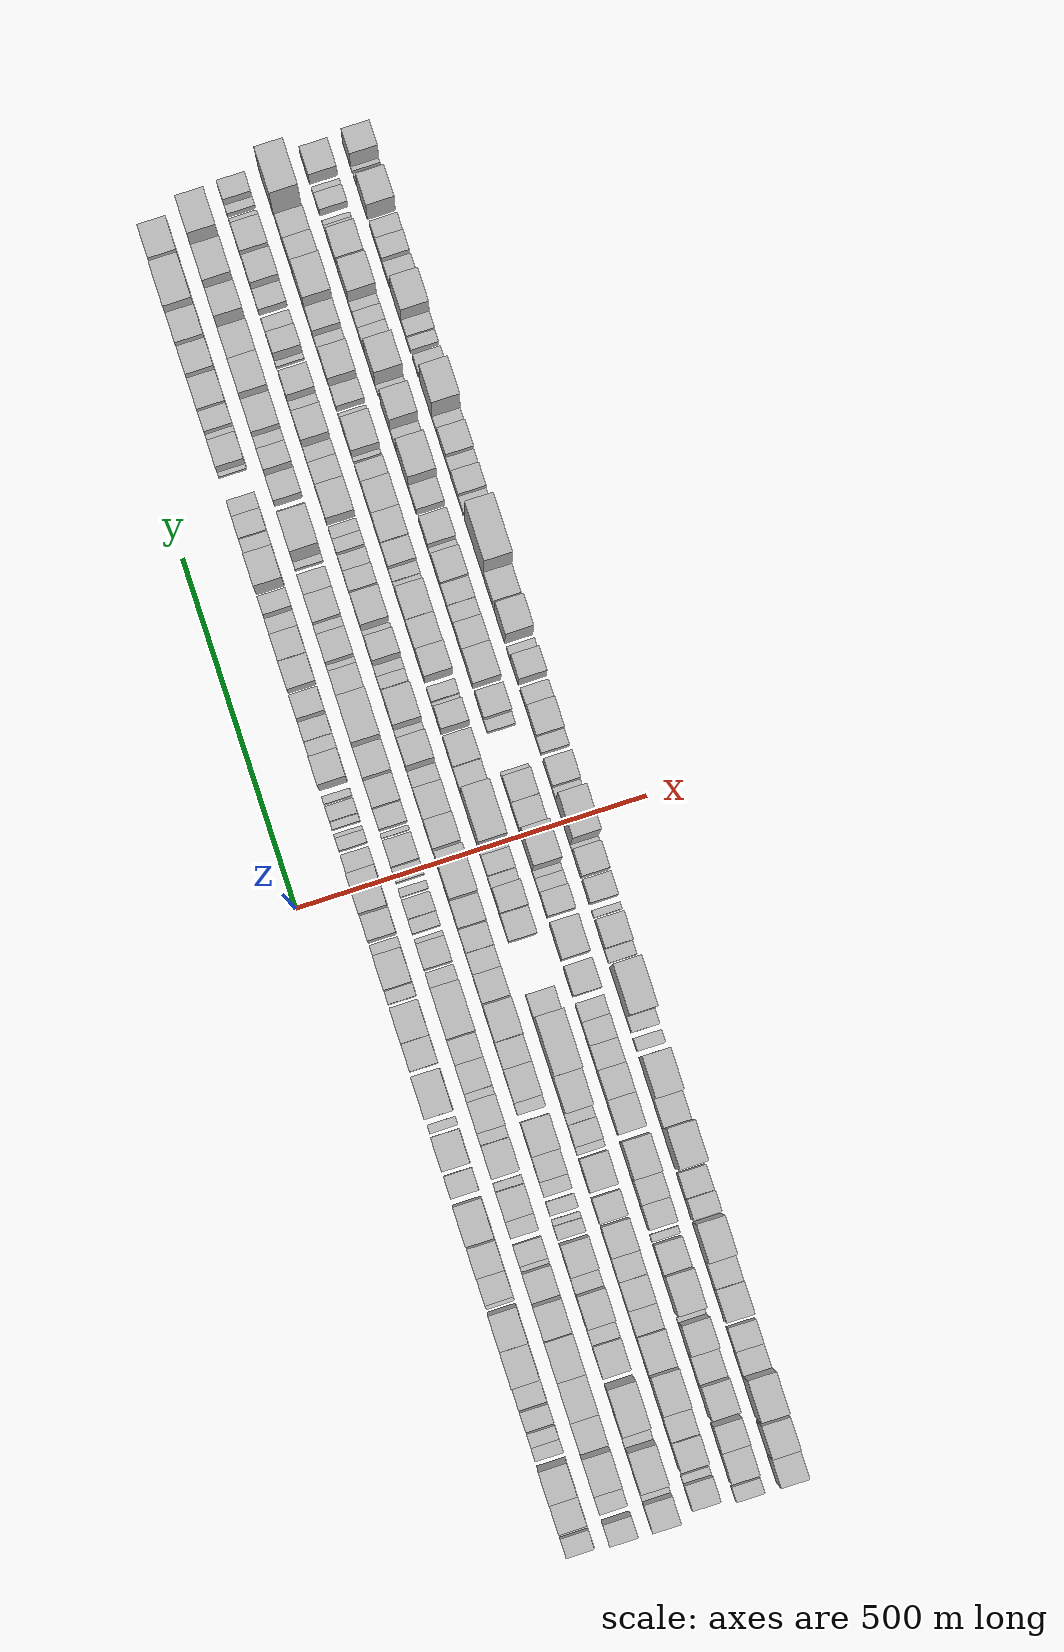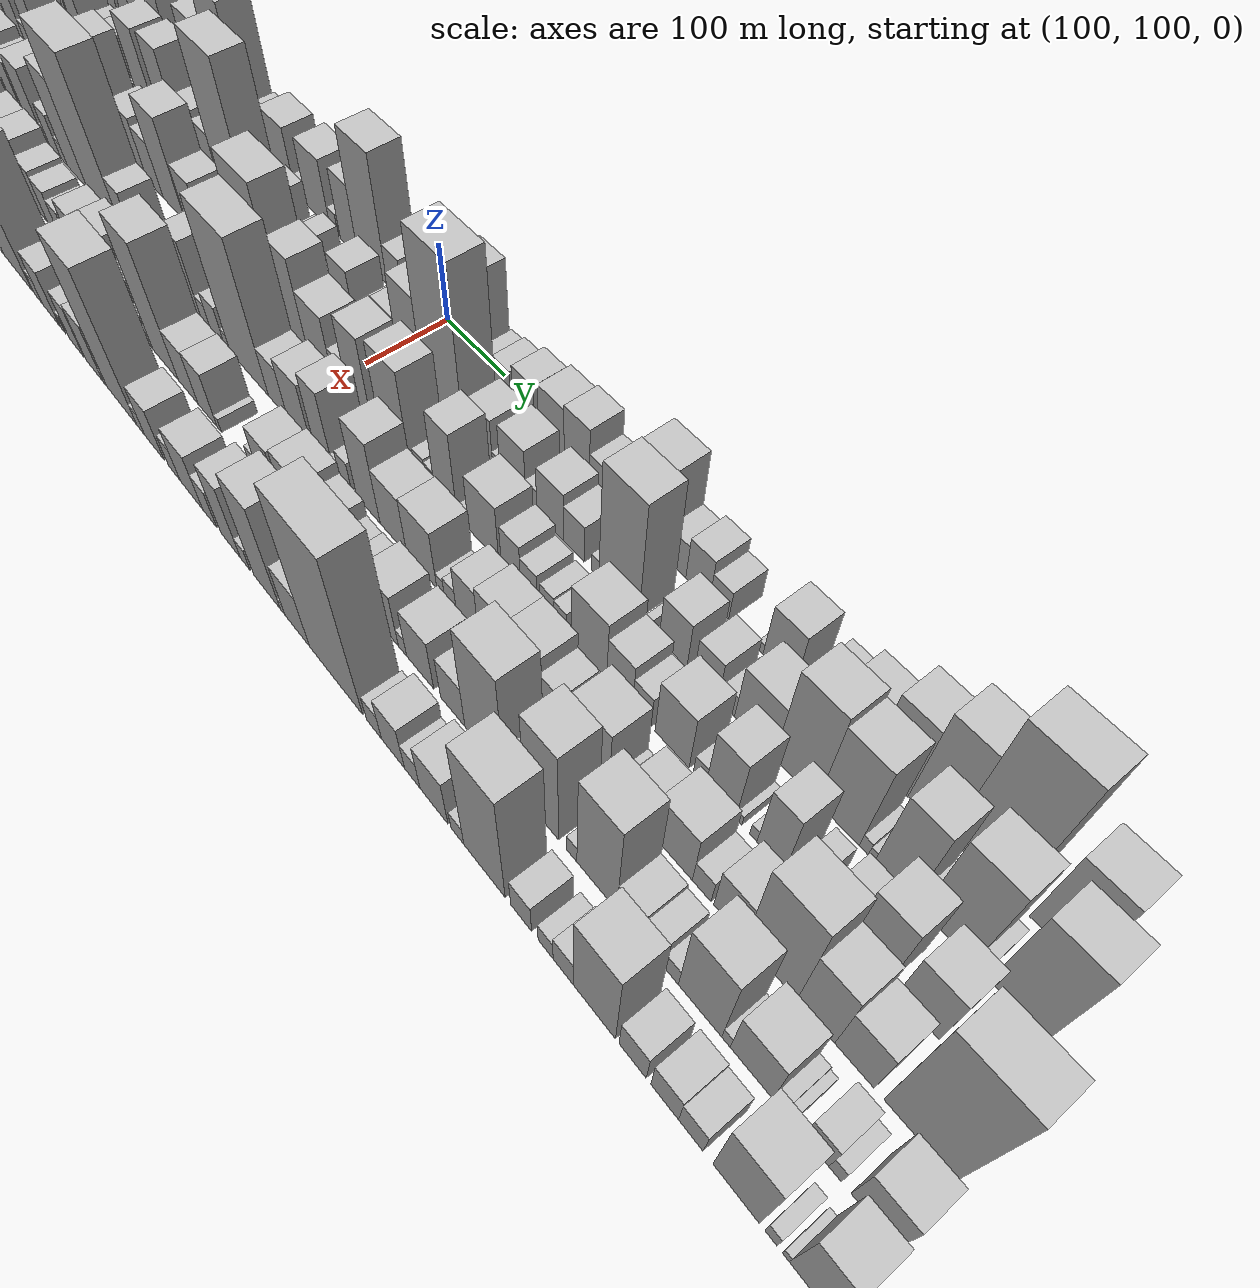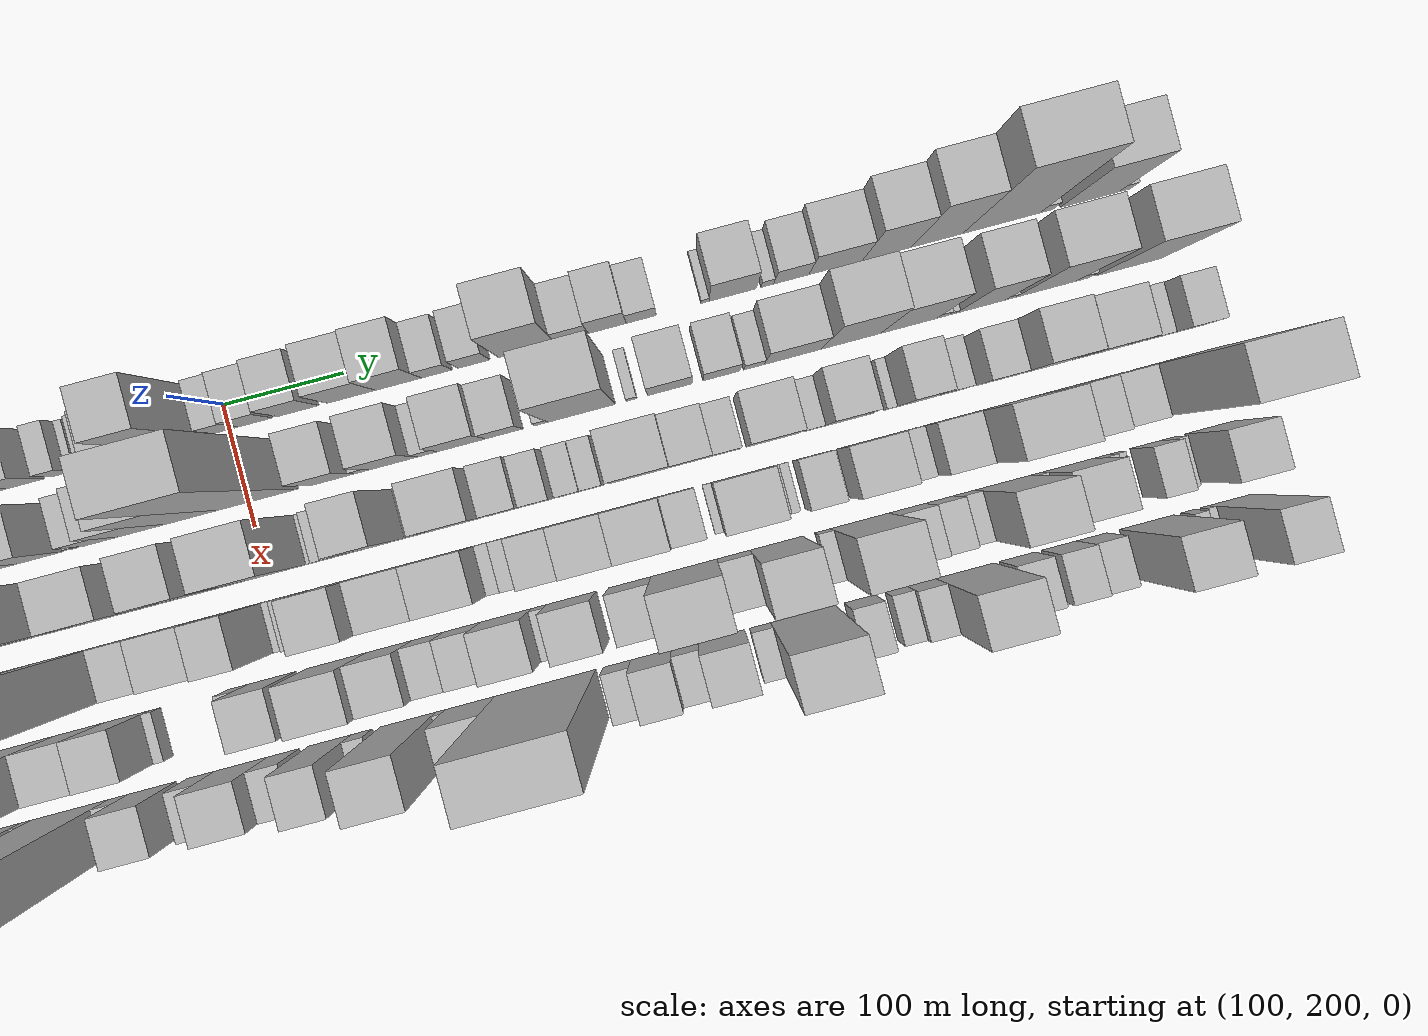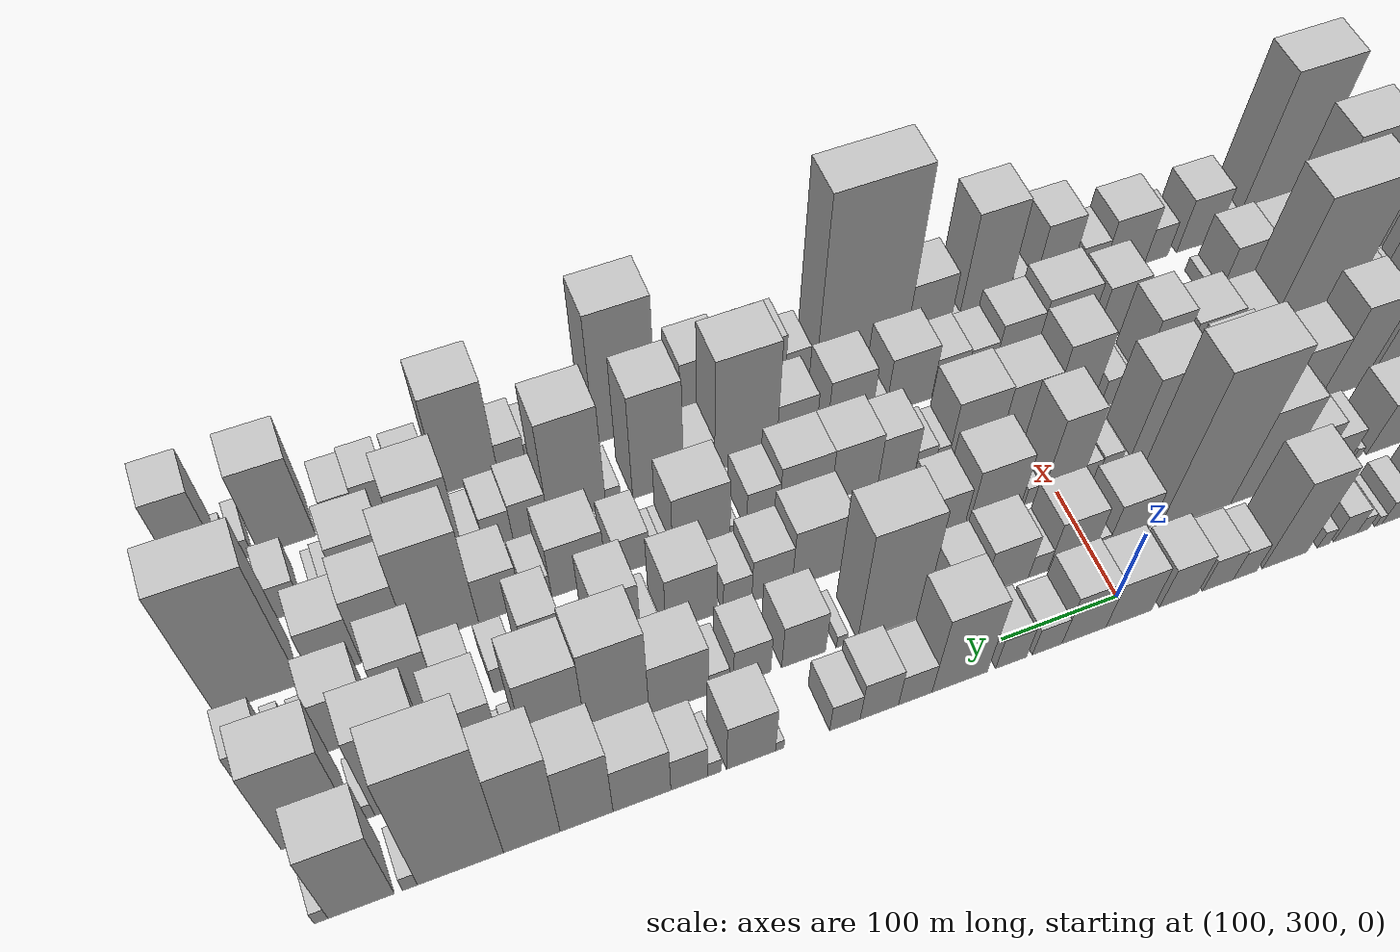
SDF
<sdf version="1.6">
 <world name="default">
  <scene>
   <sky><clouds><speed>12</speed></clouds></sky>
   <ambient>0.4 0.4 0.4 1</ambient>
   <background>0.7 0.7 0.7 1</background>
   <shadows>1</shadows>
  </scene>
  <gravity>0 0 -9.8066</gravity>
  <magnetic_field>6e-06 2.3e-05 -4.2e-05</magnetic_field>
  <physics default="0" name="default_physics" type="ode">
   <ode>
    <solver>
     <type>quick</type>
     <iters>10</iters>
     <sor>1.0</sor>
     <use_dynamic_moi_rescaling>0</use_dynamic_moi_rescaling>
    </solver>
    <constraints>
     <cfm>0</cfm>
     <erp>0.2</erp>
     <contact_max_correcting_vel>100</contact_max_correcting_vel>
     <contact_surface_layer>0.001</contact_surface_layer>
    </constraints>
   </ode>
   <max_step_size>0.004</max_step_size>
   <real_time_factor>1</real_time_factor>
   <real_time_update_rate>250</real_time_update_rate>
  </physics>
  <light name="sun" type="directional">
   <pose>0 0 10 0 0 0</pose>
   <diffuse>0.8 0.8 0.8 1</diffuse>
   <specular>0.2 0.2 0.2 1</specular>
   <attenuation>
    <range>1000</range>
    <constant>0.9</constant>
    <linear>0.01</linear>
    <quadratic>0.001</quadratic>
   </attenuation>
   <direction>-0.5 0.1 -0.9</direction>
  </light>
  <model name="building_1">
   <static>1</static>
   <pose>100.0000 -926.3559 0 0.000000 0.000000 0.000000</pose>
   <link name="link">
    <pose>0 0 25.50 0 0 0</pose>
    <collision name="collision"><geometry><box><size>40.0000 27.2883 51.0000</size></box></geometry></collision>
    <visual name="visual">
     <cast_shadows>0</cast_shadows>
     <geometry><box><size>40.0000 27.2883 51.0000</size></box></geometry>
     <material>
      <script>
       <uri>model://HANNAS_wall/materials/scripts</uri>
       <uri>model://HANNAS_wall/materials/textures</uri>
       <name>vrc/HANNAS_wall</name>
      </script>
     </material>
    </visual>
   </link>
  </model>
  <model name="building_2">
   <static>1</static>
   <pose>100.0000 -909.2402 0 0.000000 0.000000 0.000000</pose>
   <link name="link">
    <pose>0 0 7.50 0 0 0</pose>
    <collision name="collision"><geometry><box><size>40.0000 6.9430 15.0000</size></box></geometry></collision>
    <visual name="visual">
     <cast_shadows>0</cast_shadows>
     <geometry><box><size>40.0000 6.9430 15.0000</size></box></geometry>
     <material>
      <script>
       <uri>model://HANNAS_wall/materials/scripts</uri>
       <uri>model://HANNAS_wall/materials/textures</uri>
       <name>vrc/HANNAS_wall</name>
      </script>
     </material>
    </visual>
   </link>
  </model>
  <model name="building_3">
   <static>1</static>
   <pose>100.0000 -883.3214 0 0.000000 0.000000 0.000000</pose>
   <link name="link">
    <pose>0 0 37.50 0 0 0</pose>
    <collision name="collision"><geometry><box><size>40.0000 44.8946 75.0000</size></box></geometry></collision>
    <visual name="visual">
     <cast_shadows>0</cast_shadows>
     <geometry><box><size>40.0000 44.8946 75.0000</size></box></geometry>
     <material>
      <script>
       <uri>model://HANNAS_wall/materials/scripts</uri>
       <uri>model://HANNAS_wall/materials/textures</uri>
       <name>vrc/HANNAS_wall</name>
      </script>
     </material>
    </visual>
   </link>
  </model>
  <model name="building_4">
   <static>1</static>
   <pose>100.0000 -837.3300 0 0.000000 0.000000 0.000000</pose>
   <link name="link">
    <pose>0 0 66.00 0 0 0</pose>
    <collision name="collision"><geometry><box><size>40.0000 47.0882 132.0000</size></box></geometry></collision>
    <visual name="visual">
     <cast_shadows>0</cast_shadows>
     <geometry><box><size>40.0000 47.0882 132.0000</size></box></geometry>
     <material>
      <script>
       <uri>model://HANNAS_wall/materials/scripts</uri>
       <uri>model://HANNAS_wall/materials/textures</uri>
       <name>vrc/HANNAS_wall</name>
      </script>
     </material>
    </visual>
   </link>
  </model>
  <model name="building_5">
   <static>1</static>
   <pose>100.0000 -796.3062 0 0.000000 0.000000 0.000000</pose>
   <link name="link">
    <pose>0 0 18.00 0 0 0</pose>
    <collision name="collision"><geometry><box><size>40.0000 18.9595 36.0000</size></box></geometry></collision>
    <visual name="visual">
     <cast_shadows>0</cast_shadows>
     <geometry><box><size>40.0000 18.9595 36.0000</size></box></geometry>
     <material>
      <script>
       <uri>model://HANNAS_wall/materials/scripts</uri>
       <uri>model://HANNAS_wall/materials/textures</uri>
       <name>vrc/HANNAS_wall</name>
      </script>
     </material>
    </visual>
   </link>
  </model>
  <model name="building_6">
   <static>1</static>
   <pose>100.0000 -777.0659 0 0.000000 0.000000 0.000000</pose>
   <link name="link">
    <pose>0 0 19.50 0 0 0</pose>
    <collision name="collision"><geometry><box><size>40.0000 19.5210 39.0000</size></box></geometry></collision>
    <visual name="visual">
     <cast_shadows>0</cast_shadows>
     <geometry><box><size>40.0000 19.5210 39.0000</size></box></geometry>
     <material>
      <script>
       <uri>model://HANNAS_wall/materials/scripts</uri>
       <uri>model://HANNAS_wall/materials/textures</uri>
       <name>vrc/HANNAS_wall</name>
      </script>
     </material>
    </visual>
   </link>
  </model>
  <model name="building_7">
   <static>1</static>
   <pose>100.0000 -750.5060 0 0.000000 0.000000 0.000000</pose>
   <link name="link">
    <pose>0 0 24.00 0 0 0</pose>
    <collision name="collision"><geometry><box><size>40.0000 27.5988 48.0000</size></box></geometry></collision>
    <visual name="visual">
     <cast_shadows>0</cast_shadows>
     <geometry><box><size>40.0000 27.5988 48.0000</size></box></geometry>
     <material>
      <script>
       <uri>model://HANNAS_wall/materials/scripts</uri>
       <uri>model://HANNAS_wall/materials/textures</uri>
       <name>vrc/HANNAS_wall</name>
      </script>
     </material>
    </visual>
   </link>
  </model>
  <model name="building_8">
   <static>1</static>
   <pose>100.0000 -715.6049 0 0.000000 0.000000 0.000000</pose>
   <link name="link">
    <pose>0 0 33.00 0 0 0</pose>
    <collision name="collision"><geometry><box><size>40.0000 34.2035 66.0000</size></box></geometry></collision>
    <visual name="visual">
     <cast_shadows>0</cast_shadows>
     <geometry><box><size>40.0000 34.2035 66.0000</size></box></geometry>
     <material>
      <script>
       <uri>model://HANNAS_wall/materials/scripts</uri>
       <uri>model://HANNAS_wall/materials/textures</uri>
       <name>vrc/HANNAS_wall</name>
      </script>
     </material>
    </visual>
   </link>
  </model>
  <model name="building_9">
   <static>1</static>
   <pose>100.0000 -673.0866 0 0.000000 0.000000 0.000000</pose>
   <link name="link">
    <pose>0 0 73.50 0 0 0</pose>
    <collision name="collision"><geometry><box><size>40.0000 50.8330 147.0000</size></box></geometry></collision>
    <visual name="visual">
     <cast_shadows>0</cast_shadows>
     <geometry><box><size>40.0000 50.8330 147.0000</size></box></geometry>
     <material>
      <script>
       <uri>model://HANNAS_wall/materials/scripts</uri>
       <uri>model://HANNAS_wall/materials/textures</uri>
       <name>vrc/HANNAS_wall</name>
      </script>
     </material>
    </visual>
   </link>
  </model>
  <model name="building_10">
   <static>1</static>
   <pose>100.0000 -622.3766 0 0.000000 0.000000 0.000000</pose>
   <link name="link">
    <pose>0 0 72.00 0 0 0</pose>
    <collision name="collision"><geometry><box><size>40.0000 50.5870 144.0000</size></box></geometry></collision>
    <visual name="visual">
     <cast_shadows>0</cast_shadows>
     <geometry><box><size>40.0000 50.5870 144.0000</size></box></geometry>
     <material>
      <script>
       <uri>model://HANNAS_wall/materials/scripts</uri>
       <uri>model://HANNAS_wall/materials/textures</uri>
       <name>vrc/HANNAS_wall</name>
      </script>
     </material>
    </visual>
   </link>
  </model>
  <model name="building_11">
   <static>1</static>
   <pose>100.0000 -589.4792 0 0.000000 0.000000 0.000000</pose>
   <link name="link">
    <pose>0 0 7.50 0 0 0</pose>
    <collision name="collision"><geometry><box><size>40.0000 7.2077 15.0000</size></box></geometry></collision>
    <visual name="visual">
     <cast_shadows>0</cast_shadows>
     <geometry><box><size>40.0000 7.2077 15.0000</size></box></geometry>
     <material>
      <script>
       <uri>model://HANNAS_wall/materials/scripts</uri>
       <uri>model://HANNAS_wall/materials/textures</uri>
       <name>vrc/HANNAS_wall</name>
      </script>
     </material>
    </visual>
   </link>
  </model>
  <model name="building_12">
   <static>1</static>
   <pose>100.0000 -566.5896 0 0.000000 0.000000 0.000000</pose>
   <link name="link">
    <pose>0 0 37.50 0 0 0</pose>
    <collision name="collision"><geometry><box><size>40.0000 38.5714 75.0000</size></box></geometry></collision>
    <visual name="visual">
     <cast_shadows>0</cast_shadows>
     <geometry><box><size>40.0000 38.5714 75.0000</size></box></geometry>
     <material>
      <script>
       <uri>model://HANNAS_wall/materials/scripts</uri>
       <uri>model://HANNAS_wall/materials/textures</uri>
       <name>vrc/HANNAS_wall</name>
      </script>
     </material>
    </visual>
   </link>
  </model>
  <model name="building_13">
   <static>1</static>
   <pose>100.0000 -526.4123 0 0.000000 0.000000 0.000000</pose>
   <link name="link">
    <pose>0 0 58.50 0 0 0</pose>
    <collision name="collision"><geometry><box><size>40.0000 41.7831 117.0000</size></box></geometry></collision>
    <visual name="visual">
     <cast_shadows>0</cast_shadows>
     <geometry><box><size>40.0000 41.7831 117.0000</size></box></geometry>
     <material>
      <script>
       <uri>model://HANNAS_wall/materials/scripts</uri>
       <uri>model://HANNAS_wall/materials/textures</uri>
       <name>vrc/HANNAS_wall</name>
      </script>
     </material>
    </visual>
   </link>
  </model>
  <model name="building_14">
   <static>1</static>
   <pose>100.0000 -473.5683 0 0.000000 0.000000 0.000000</pose>
   <link name="link">
    <pose>0 0 88.50 0 0 0</pose>
    <collision name="collision"><geometry><box><size>40.0000 55.9050 177.0000</size></box></geometry></collision>
    <visual name="visual">
     <cast_shadows>0</cast_shadows>
     <geometry><box><size>40.0000 55.9050 177.0000</size></box></geometry>
     <material>
      <script>
       <uri>model://HANNAS_wall/materials/scripts</uri>
       <uri>model://HANNAS_wall/materials/textures</uri>
       <name>vrc/HANNAS_wall</name>
      </script>
     </material>
    </visual>
   </link>
  </model>
  <model name="building_15">
   <static>1</static>
   <pose>100.0000 -420.7064 0 0.000000 0.000000 0.000000</pose>
   <link name="link">
    <pose>0 0 30.00 0 0 0</pose>
    <collision name="collision"><geometry><box><size>40.0000 31.8189 60.0000</size></box></geometry></collision>
    <visual name="visual">
     <cast_shadows>0</cast_shadows>
     <geometry><box><size>40.0000 31.8189 60.0000</size></box></geometry>
     <material>
      <script>
       <uri>model://HANNAS_wall/materials/scripts</uri>
       <uri>model://HANNAS_wall/materials/textures</uri>
       <name>vrc/HANNAS_wall</name>
      </script>
     </material>
    </visual>
   </link>
  </model>
  <model name="building_16">
   <static>1</static>
   <pose>100.0000 -373.8474 0 0.000000 0.000000 0.000000</pose>
   <link name="link">
    <pose>0 0 60.00 0 0 0</pose>
    <collision name="collision"><geometry><box><size>40.0000 47.8990 120.0000</size></box></geometry></collision>
    <visual name="visual">
     <cast_shadows>0</cast_shadows>
     <geometry><box><size>40.0000 47.8990 120.0000</size></box></geometry>
     <material>
      <script>
       <uri>model://HANNAS_wall/materials/scripts</uri>
       <uri>model://HANNAS_wall/materials/textures</uri>
       <name>vrc/HANNAS_wall</name>
      </script>
     </material>
    </visual>
   </link>
  </model>
  <model name="building_17">
   <static>1</static>
   <pose>100.0000 -338.8018 0 0.000000 0.000000 0.000000</pose>
   <link name="link">
    <pose>0 0 13.50 0 0 0</pose>
    <collision name="collision"><geometry><box><size>40.0000 12.1922 27.0000</size></box></geometry></collision>
    <visual name="visual">
     <cast_shadows>0</cast_shadows>
     <geometry><box><size>40.0000 12.1922 27.0000</size></box></geometry>
     <material>
      <script>
       <uri>model://HANNAS_wall/materials/scripts</uri>
       <uri>model://HANNAS_wall/materials/textures</uri>
       <name>vrc/HANNAS_wall</name>
      </script>
     </material>
    </visual>
   </link>
  </model>
  <model name="building_18">
   <static>1</static>
   <pose>100.0000 -295.1788 0 0.000000 0.000000 0.000000</pose>
   <link name="link">
    <pose>0 0 91.50 0 0 0</pose>
    <collision name="collision"><geometry><box><size>40.0000 59.0539 183.0000</size></box></geometry></collision>
    <visual name="visual">
     <cast_shadows>0</cast_shadows>
     <geometry><box><size>40.0000 59.0539 183.0000</size></box></geometry>
     <material>
      <script>
       <uri>model://HANNAS_wall/materials/scripts</uri>
       <uri>model://HANNAS_wall/materials/textures</uri>
       <name>vrc/HANNAS_wall</name>
      </script>
     </material>
    </visual>
   </link>
  </model>
  <model name="building_19">
   <static>1</static>
   <pose>100.0000 -238.2212 0 0.000000 0.000000 0.000000</pose>
   <link name="link">
    <pose>0 0 33.00 0 0 0</pose>
    <collision name="collision"><geometry><box><size>40.0000 38.8613 66.0000</size></box></geometry></collision>
    <visual name="visual">
     <cast_shadows>0</cast_shadows>
     <geometry><box><size>40.0000 38.8613 66.0000</size></box></geometry>
     <material>
      <script>
       <uri>model://HANNAS_wall/materials/scripts</uri>
       <uri>model://HANNAS_wall/materials/textures</uri>
       <name>vrc/HANNAS_wall</name>
      </script>
     </material>
    </visual>
   </link>
  </model>
  <model name="building_20">
   <static>1</static>
   <pose>100.0000 -193.5843 0 0.000000 0.000000 0.000000</pose>
   <link name="link">
    <pose>0 0 43.50 0 0 0</pose>
    <collision name="collision"><geometry><box><size>40.0000 50.4124 87.0000</size></box></geometry></collision>
    <visual name="visual">
     <cast_shadows>0</cast_shadows>
     <geometry><box><size>40.0000 50.4124 87.0000</size></box></geometry>
     <material>
      <script>
       <uri>model://HANNAS_wall/materials/scripts</uri>
       <uri>model://HANNAS_wall/materials/textures</uri>
       <name>vrc/HANNAS_wall</name>
      </script>
     </material>
    </visual>
   </link>
  </model>
  <model name="building_21">
   <static>1</static>
   <pose>100.0000 -153.1181 0 0.000000 0.000000 0.000000</pose>
   <link name="link">
    <pose>0 0 16.50 0 0 0</pose>
    <collision name="collision"><geometry><box><size>40.0000 18.5201 33.0000</size></box></geometry></collision>
    <visual name="visual">
     <cast_shadows>0</cast_shadows>
     <geometry><box><size>40.0000 18.5201 33.0000</size></box></geometry>
     <material>
      <script>
       <uri>model://HANNAS_wall/materials/scripts</uri>
       <uri>model://HANNAS_wall/materials/textures</uri>
       <name>vrc/HANNAS_wall</name>
      </script>
     </material>
    </visual>
   </link>
  </model>
  <model name="building_22">
   <static>1</static>
   <pose>100.0000 -119.5392 0 0.000000 0.000000 0.000000</pose>
   <link name="link">
    <pose>0 0 45.00 0 0 0</pose>
    <collision name="collision"><geometry><box><size>40.0000 48.6377 90.0000</size></box></geometry></collision>
    <visual name="visual">
     <cast_shadows>0</cast_shadows>
     <geometry><box><size>40.0000 48.6377 90.0000</size></box></geometry>
     <material>
      <script>
       <uri>model://HANNAS_wall/materials/scripts</uri>
       <uri>model://HANNAS_wall/materials/textures</uri>
       <name>vrc/HANNAS_wall</name>
      </script>
     </material>
    </visual>
   </link>
  </model>
  <model name="building_23">
   <static>1</static>
   <pose>100.0000 -86.9276 0 0.000000 0.000000 0.000000</pose>
   <link name="link">
    <pose>0 0 15.00 0 0 0</pose>
    <collision name="collision"><geometry><box><size>40.0000 16.5854 30.0000</size></box></geometry></collision>
    <visual name="visual">
     <cast_shadows>0</cast_shadows>
     <geometry><box><size>40.0000 16.5854 30.0000</size></box></geometry>
     <material>
      <script>
       <uri>model://HANNAS_wall/materials/scripts</uri>
       <uri>model://HANNAS_wall/materials/textures</uri>
       <name>vrc/HANNAS_wall</name>
      </script>
     </material>
    </visual>
   </link>
  </model>
  <model name="building_24">
   <static>1</static>
   <pose>100.0000 -56.8699 0 0.000000 0.000000 0.000000</pose>
   <link name="link">
    <pose>0 0 46.50 0 0 0</pose>
    <collision name="collision"><geometry><box><size>40.0000 35.5301 93.0000</size></box></geometry></collision>
    <visual name="visual">
     <cast_shadows>0</cast_shadows>
     <geometry><box><size>40.0000 35.5301 93.0000</size></box></geometry>
     <material>
      <script>
       <uri>model://HANNAS_wall/materials/scripts</uri>
       <uri>model://HANNAS_wall/materials/textures</uri>
       <name>vrc/HANNAS_wall</name>
      </script>
     </material>
    </visual>
   </link>
  </model>
  <model name="building_25">
   <static>1</static>
   <pose>100.0000 -10.9166 0 0.000000 0.000000 0.000000</pose>
   <link name="link">
    <pose>0 0 82.50 0 0 0</pose>
    <collision name="collision"><geometry><box><size>40.0000 56.3764 165.0000</size></box></geometry></collision>
    <visual name="visual">
     <cast_shadows>0</cast_shadows>
     <geometry><box><size>40.0000 56.3764 165.0000</size></box></geometry>
     <material>
      <script>
       <uri>model://HANNAS_wall/materials/scripts</uri>
       <uri>model://HANNAS_wall/materials/textures</uri>
       <name>vrc/HANNAS_wall</name>
      </script>
     </material>
    </visual>
   </link>
  </model>
  <model name="building_26">
   <static>1</static>
   <pose>100.0000 32.5966 0 0.000000 0.000000 0.000000</pose>
   <link name="link">
    <pose>0 0 27.00 0 0 0</pose>
    <collision name="collision"><geometry><box><size>40.0000 30.6500 54.0000</size></box></geometry></collision>
    <visual name="visual">
     <cast_shadows>0</cast_shadows>
     <geometry><box><size>40.0000 30.6500 54.0000</size></box></geometry>
     <material>
      <script>
       <uri>model://HANNAS_wall/materials/scripts</uri>
       <uri>model://HANNAS_wall/materials/textures</uri>
       <name>vrc/HANNAS_wall</name>
      </script>
     </material>
    </visual>
   </link>
  </model>
  <model name="building_27">
   <static>1</static>
   <pose>100.0000 63.9941 0 0.000000 0.000000 0.000000</pose>
   <link name="link">
    <pose>0 0 16.50 0 0 0</pose>
    <collision name="collision"><geometry><box><size>40.0000 18.1451 33.0000</size></box></geometry></collision>
    <visual name="visual">
     <cast_shadows>0</cast_shadows>
     <geometry><box><size>40.0000 18.1451 33.0000</size></box></geometry>
     <material>
      <script>
       <uri>model://HANNAS_wall/materials/scripts</uri>
       <uri>model://HANNAS_wall/materials/textures</uri>
       <name>vrc/HANNAS_wall</name>
      </script>
     </material>
    </visual>
   </link>
  </model>
  <model name="building_28">
   <static>1</static>
   <pose>100.0000 76.3209 0 0.000000 0.000000 0.000000</pose>
   <link name="link">
    <pose>0 0 7.50 0 0 0</pose>
    <collision name="collision"><geometry><box><size>40.0000 6.5086 15.0000</size></box></geometry></collision>
    <visual name="visual">
     <cast_shadows>0</cast_shadows>
     <geometry><box><size>40.0000 6.5086 15.0000</size></box></geometry>
     <material>
      <script>
       <uri>model://HANNAS_wall/materials/scripts</uri>
       <uri>model://HANNAS_wall/materials/textures</uri>
       <name>vrc/HANNAS_wall</name>
      </script>
     </material>
    </visual>
   </link>
  </model>
  <model name="building_29">
   <static>1</static>
   <pose>100.0000 90.9001 0 0.000000 0.000000 0.000000</pose>
   <link name="link">
    <pose>0 0 12.00 0 0 0</pose>
    <collision name="collision"><geometry><box><size>40.0000 10.6498 24.0000</size></box></geometry></collision>
    <visual name="visual">
     <cast_shadows>0</cast_shadows>
     <geometry><box><size>40.0000 10.6498 24.0000</size></box></geometry>
     <material>
      <script>
       <uri>model://HANNAS_wall/materials/scripts</uri>
       <uri>model://HANNAS_wall/materials/textures</uri>
       <name>vrc/HANNAS_wall</name>
      </script>
     </material>
    </visual>
   </link>
  </model>
  <model name="building_30">
   <static>1</static>
   <pose>100.0000 106.9220 0 0.000000 0.000000 0.000000</pose>
   <link name="link">
    <pose>0 0 19.50 0 0 0</pose>
    <collision name="collision"><geometry><box><size>40.0000 21.3939 39.0000</size></box></geometry></collision>
    <visual name="visual">
     <cast_shadows>0</cast_shadows>
     <geometry><box><size>40.0000 21.3939 39.0000</size></box></geometry>
     <material>
      <script>
       <uri>model://HANNAS_wall/materials/scripts</uri>
       <uri>model://HANNAS_wall/materials/textures</uri>
       <name>vrc/HANNAS_wall</name>
      </script>
     </material>
    </visual>
   </link>
  </model>
  <model name="building_31">
   <static>1</static>
   <pose>100.0000 127.0313 0 0.000000 0.000000 0.000000</pose>
   <link name="link">
    <pose>0 0 12.00 0 0 0</pose>
    <collision name="collision"><geometry><box><size>40.0000 10.8247 24.0000</size></box></geometry></collision>
    <visual name="visual">
     <cast_shadows>0</cast_shadows>
     <geometry><box><size>40.0000 10.8247 24.0000</size></box></geometry>
     <material>
      <script>
       <uri>model://HANNAS_wall/materials/scripts</uri>
       <uri>model://HANNAS_wall/materials/textures</uri>
       <name>vrc/HANNAS_wall</name>
      </script>
     </material>
    </visual>
   </link>
  </model>
  <model name="building_32">
   <static>1</static>
   <pose>100.0000 162.4941 0 0.000000 0.000000 0.000000</pose>
   <link name="link">
    <pose>0 0 64.50 0 0 0</pose>
    <collision name="collision"><geometry><box><size>40.0000 40.1008 129.0000</size></box></geometry></collision>
    <visual name="visual">
     <cast_shadows>0</cast_shadows>
     <geometry><box><size>40.0000 40.1008 129.0000</size></box></geometry>
     <material>
      <script>
       <uri>model://HANNAS_wall/materials/scripts</uri>
       <uri>model://HANNAS_wall/materials/textures</uri>
       <name>vrc/HANNAS_wall</name>
      </script>
     </material>
    </visual>
   </link>
  </model>
  <model name="building_33">
   <static>1</static>
   <pose>100.0000 198.1271 0 0.000000 0.000000 0.000000</pose>
   <link name="link">
    <pose>0 0 21.00 0 0 0</pose>
    <collision name="collision"><geometry><box><size>40.0000 21.1651 42.0000</size></box></geometry></collision>
    <visual name="visual">
     <cast_shadows>0</cast_shadows>
     <geometry><box><size>40.0000 21.1651 42.0000</size></box></geometry>
     <material>
      <script>
       <uri>model://HANNAS_wall/materials/scripts</uri>
       <uri>model://HANNAS_wall/materials/textures</uri>
       <name>vrc/HANNAS_wall</name>
      </script>
     </material>
    </visual>
   </link>
  </model>
  <model name="building_34">
   <static>1</static>
   <pose>100.0000 222.5470 0 0.000000 0.000000 0.000000</pose>
   <link name="link">
    <pose>0 0 24.00 0 0 0</pose>
    <collision name="collision"><geometry><box><size>40.0000 27.6747 48.0000</size></box></geometry></collision>
    <visual name="visual">
     <cast_shadows>0</cast_shadows>
     <geometry><box><size>40.0000 27.6747 48.0000</size></box></geometry>
     <material>
      <script>
       <uri>model://HANNAS_wall/materials/scripts</uri>
       <uri>model://HANNAS_wall/materials/textures</uri>
       <name>vrc/HANNAS_wall</name>
      </script>
     </material>
    </visual>
   </link>
  </model>
  <model name="building_35">
   <static>1</static>
   <pose>100.0000 257.3368 0 0.000000 0.000000 0.000000</pose>
   <link name="link">
    <pose>0 0 30.00 0 0 0</pose>
    <collision name="collision"><geometry><box><size>40.0000 33.9049 60.0000</size></box></geometry></collision>
    <visual name="visual">
     <cast_shadows>0</cast_shadows>
     <geometry><box><size>40.0000 33.9049 60.0000</size></box></geometry>
     <material>
      <script>
       <uri>model://HANNAS_wall/materials/scripts</uri>
       <uri>model://HANNAS_wall/materials/textures</uri>
       <name>vrc/HANNAS_wall</name>
      </script>
     </material>
    </visual>
   </link>
  </model>
  <model name="building_36">
   <static>1</static>
   <pose>100.0000 301.1761 0 0.000000 0.000000 0.000000</pose>
   <link name="link">
    <pose>0 0 34.50 0 0 0</pose>
    <collision name="collision"><geometry><box><size>40.0000 39.7738 69.0000</size></box></geometry></collision>
    <visual name="visual">
     <cast_shadows>0</cast_shadows>
     <geometry><box><size>40.0000 39.7738 69.0000</size></box></geometry>
     <material>
      <script>
       <uri>model://HANNAS_wall/materials/scripts</uri>
       <uri>model://HANNAS_wall/materials/textures</uri>
       <name>vrc/HANNAS_wall</name>
      </script>
     </material>
    </visual>
   </link>
  </model>
  <model name="building_37">
   <static>1</static>
   <pose>100.0000 340.0397 0 0.000000 0.000000 0.000000</pose>
   <link name="link">
    <pose>0 0 37.50 0 0 0</pose>
    <collision name="collision"><geometry><box><size>40.0000 37.9533 75.0000</size></box></geometry></collision>
    <visual name="visual">
     <cast_shadows>0</cast_shadows>
     <geometry><box><size>40.0000 37.9533 75.0000</size></box></geometry>
     <material>
      <script>
       <uri>model://HANNAS_wall/materials/scripts</uri>
       <uri>model://HANNAS_wall/materials/textures</uri>
       <name>vrc/HANNAS_wall</name>
      </script>
     </material>
    </visual>
   </link>
  </model>
  <model name="building_38">
   <static>1</static>
   <pose>100.0000 371.5802 0 0.000000 0.000000 0.000000</pose>
   <link name="link">
    <pose>0 0 21.00 0 0 0</pose>
    <collision name="collision"><geometry><box><size>40.0000 25.1276 42.0000</size></box></geometry></collision>
    <visual name="visual">
     <cast_shadows>0</cast_shadows>
     <geometry><box><size>40.0000 25.1276 42.0000</size></box></geometry>
     <material>
      <script>
       <uri>model://HANNAS_wall/materials/scripts</uri>
       <uri>model://HANNAS_wall/materials/textures</uri>
       <name>vrc/HANNAS_wall</name>
      </script>
     </material>
    </visual>
   </link>
  </model>
  <model name="building_39">
   <static>1</static>
   <pose>100.0000 402.2355 0 0.000000 0.000000 0.000000</pose>
   <link name="link">
    <pose>0 0 24.00 0 0 0</pose>
    <collision name="collision"><geometry><box><size>40.0000 26.1829 48.0000</size></box></geometry></collision>
    <visual name="visual">
     <cast_shadows>0</cast_shadows>
     <geometry><box><size>40.0000 26.1829 48.0000</size></box></geometry>
     <material>
      <script>
       <uri>model://HANNAS_wall/materials/scripts</uri>
       <uri>model://HANNAS_wall/materials/textures</uri>
       <name>vrc/HANNAS_wall</name>
      </script>
     </material>
    </visual>
   </link>
  </model>
  <model name="building_40">
   <static>1</static>
   <pose>100.0000 445.4357 0 0.000000 0.000000 0.000000</pose>
   <link name="link">
    <pose>0 0 60.00 0 0 0</pose>
    <collision name="collision"><geometry><box><size>40.0000 46.2174 120.0000</size></box></geometry></collision>
    <visual name="visual">
     <cast_shadows>0</cast_shadows>
     <geometry><box><size>40.0000 46.2174 120.0000</size></box></geometry>
     <material>
      <script>
       <uri>model://HANNAS_wall/materials/scripts</uri>
       <uri>model://HANNAS_wall/materials/textures</uri>
       <name>vrc/HANNAS_wall</name>
      </script>
     </material>
    </visual>
   </link>
  </model>
  <model name="building_41">
   <static>1</static>
   <pose>100.0000 482.3747 0 0.000000 0.000000 0.000000</pose>
   <link name="link">
    <pose>0 0 24.00 0 0 0</pose>
    <collision name="collision"><geometry><box><size>40.0000 27.6606 48.0000</size></box></geometry></collision>
    <visual name="visual">
     <cast_shadows>0</cast_shadows>
     <geometry><box><size>40.0000 27.6606 48.0000</size></box></geometry>
     <material>
      <script>
       <uri>model://HANNAS_wall/materials/scripts</uri>
       <uri>model://HANNAS_wall/materials/textures</uri>
       <name>vrc/HANNAS_wall</name>
      </script>
     </material>
    </visual>
   </link>
  </model>
  <model name="building_42">
   <static>1</static>
   <pose>100.0000 511.8867 0 0.000000 0.000000 0.000000</pose>
   <link name="link">
    <pose>0 0 30.00 0 0 0</pose>
    <collision name="collision"><geometry><box><size>40.0000 31.3634 60.0000</size></box></geometry></collision>
    <visual name="visual">
     <cast_shadows>0</cast_shadows>
     <geometry><box><size>40.0000 31.3634 60.0000</size></box></geometry>
     <material>
      <script>
       <uri>model://HANNAS_wall/materials/scripts</uri>
       <uri>model://HANNAS_wall/materials/textures</uri>
       <name>vrc/HANNAS_wall</name>
      </script>
     </material>
    </visual>
   </link>
  </model>
  <model name="building_43">
   <static>1</static>
   <pose>100.0000 539.8945 0 0.000000 0.000000 0.000000</pose>
   <link name="link">
    <pose>0 0 21.00 0 0 0</pose>
    <collision name="collision"><geometry><box><size>40.0000 24.6521 42.0000</size></box></geometry></collision>
    <visual name="visual">
     <cast_shadows>0</cast_shadows>
     <geometry><box><size>40.0000 24.6521 42.0000</size></box></geometry>
     <material>
      <script>
       <uri>model://HANNAS_wall/materials/scripts</uri>
       <uri>model://HANNAS_wall/materials/textures</uri>
       <name>vrc/HANNAS_wall</name>
      </script>
     </material>
    </visual>
   </link>
  </model>
  <model name="building_44">
   <static>1</static>
   <pose>100.0000 592.3509 0 0.000000 0.000000 0.000000</pose>
   <link name="link">
    <pose>0 0 7.50 0 0 0</pose>
    <collision name="collision"><geometry><box><size>40.0000 6.7535 15.0000</size></box></geometry></collision>
    <visual name="visual">
     <cast_shadows>0</cast_shadows>
     <geometry><box><size>40.0000 6.7535 15.0000</size></box></geometry>
     <material>
      <script>
       <uri>model://HANNAS_wall/materials/scripts</uri>
       <uri>model://HANNAS_wall/materials/textures</uri>
       <name>vrc/HANNAS_wall</name>
      </script>
     </material>
    </visual>
   </link>
  </model>
  <model name="building_45">
   <static>1</static>
   <pose>100.0000 615.0703 0 0.000000 0.000000 0.000000</pose>
   <link name="link">
    <pose>0 0 37.50 0 0 0</pose>
    <collision name="collision"><geometry><box><size>40.0000 38.6853 75.0000</size></box></geometry></collision>
    <visual name="visual">
     <cast_shadows>0</cast_shadows>
     <geometry><box><size>40.0000 38.6853 75.0000</size></box></geometry>
     <material>
      <script>
       <uri>model://HANNAS_wall/materials/scripts</uri>
       <uri>model://HANNAS_wall/materials/textures</uri>
       <name>vrc/HANNAS_wall</name>
      </script>
     </material>
    </visual>
   </link>
  </model>
  <model name="building_46">
   <static>1</static>
   <pose>100.0000 643.6625 0 0.000000 0.000000 0.000000</pose>
   <link name="link">
    <pose>0 0 12.00 0 0 0</pose>
    <collision name="collision"><geometry><box><size>40.0000 10.4989 24.0000</size></box></geometry></collision>
    <visual name="visual">
     <cast_shadows>0</cast_shadows>
     <geometry><box><size>40.0000 10.4989 24.0000</size></box></geometry>
     <material>
      <script>
       <uri>model://HANNAS_wall/materials/scripts</uri>
       <uri>model://HANNAS_wall/materials/textures</uri>
       <name>vrc/HANNAS_wall</name>
      </script>
     </material>
    </visual>
   </link>
  </model>
  <model name="building_47">
   <static>1</static>
   <pose>100.0000 663.4253 0 0.000000 0.000000 0.000000</pose>
   <link name="link">
    <pose>0 0 27.00 0 0 0</pose>
    <collision name="collision"><geometry><box><size>40.0000 29.0267 54.0000</size></box></geometry></collision>
    <visual name="visual">
     <cast_shadows>0</cast_shadows>
     <geometry><box><size>40.0000 29.0267 54.0000</size></box></geometry>
     <material>
      <script>
       <uri>model://HANNAS_wall/materials/scripts</uri>
       <uri>model://HANNAS_wall/materials/textures</uri>
       <name>vrc/HANNAS_wall</name>
      </script>
     </material>
    </visual>
   </link>
  </model>
  <model name="building_48">
   <static>1</static>
   <pose>100.0000 700.1703 0 0.000000 0.000000 0.000000</pose>
   <link name="link">
    <pose>0 0 37.50 0 0 0</pose>
    <collision name="collision"><geometry><box><size>40.0000 44.4634 75.0000</size></box></geometry></collision>
    <visual name="visual">
     <cast_shadows>0</cast_shadows>
     <geometry><box><size>40.0000 44.4634 75.0000</size></box></geometry>
     <material>
      <script>
       <uri>model://HANNAS_wall/materials/scripts</uri>
       <uri>model://HANNAS_wall/materials/textures</uri>
       <name>vrc/HANNAS_wall</name>
      </script>
     </material>
    </visual>
   </link>
  </model>
  <model name="building_49">
   <static>1</static>
   <pose>100.0000 742.5319 0 0.000000 0.000000 0.000000</pose>
   <link name="link">
    <pose>0 0 55.50 0 0 0</pose>
    <collision name="collision"><geometry><box><size>40.0000 40.2598 111.0000</size></box></geometry></collision>
    <visual name="visual">
     <cast_shadows>0</cast_shadows>
     <geometry><box><size>40.0000 40.2598 111.0000</size></box></geometry>
     <material>
      <script>
       <uri>model://HANNAS_wall/materials/scripts</uri>
       <uri>model://HANNAS_wall/materials/textures</uri>
       <name>vrc/HANNAS_wall</name>
      </script>
     </material>
    </visual>
   </link>
  </model>
  <model name="building_50">
   <static>1</static>
   <pose>100.0000 783.9385 0 0.000000 0.000000 0.000000</pose>
   <link name="link">
    <pose>0 0 70.50 0 0 0</pose>
    <collision name="collision"><geometry><box><size>40.0000 42.5534 141.0000</size></box></geometry></collision>
    <visual name="visual">
     <cast_shadows>0</cast_shadows>
     <geometry><box><size>40.0000 42.5534 141.0000</size></box></geometry>
     <material>
      <script>
       <uri>model://HANNAS_wall/materials/scripts</uri>
       <uri>model://HANNAS_wall/materials/textures</uri>
       <name>vrc/HANNAS_wall</name>
      </script>
     </material>
    </visual>
   </link>
  </model>
  <model name="building_51">
   <static>1</static>
   <pose>100.0000 836.9763 0 0.000000 0.000000 0.000000</pose>
   <link name="link">
    <pose>0 0 99.00 0 0 0</pose>
    <collision name="collision"><geometry><box><size>40.0000 63.5222 198.0000</size></box></geometry></collision>
    <visual name="visual">
     <cast_shadows>0</cast_shadows>
     <geometry><box><size>40.0000 63.5222 198.0000</size></box></geometry>
     <material>
      <script>
       <uri>model://HANNAS_wall/materials/scripts</uri>
       <uri>model://HANNAS_wall/materials/textures</uri>
       <name>vrc/HANNAS_wall</name>
      </script>
     </material>
    </visual>
   </link>
  </model>
  <model name="building_52">
   <static>1</static>
   <pose>100.0000 874.1453 0 0.000000 0.000000 0.000000</pose>
   <link name="link">
    <pose>0 0 12.00 0 0 0</pose>
    <collision name="collision"><geometry><box><size>40.0000 10.8160 24.0000</size></box></geometry></collision>
    <visual name="visual">
     <cast_shadows>0</cast_shadows>
     <geometry><box><size>40.0000 10.8160 24.0000</size></box></geometry>
     <material>
      <script>
       <uri>model://HANNAS_wall/materials/scripts</uri>
       <uri>model://HANNAS_wall/materials/textures</uri>
       <name>vrc/HANNAS_wall</name>
      </script>
     </material>
    </visual>
   </link>
  </model>
  <model name="building_53">
   <static>1</static>
   <pose>100.0000 909.4629 0 0.000000 0.000000 0.000000</pose>
   <link name="link">
    <pose>0 0 60.00 0 0 0</pose>
    <collision name="collision"><geometry><box><size>40.0000 47.8191 120.0000</size></box></geometry></collision>
    <visual name="visual">
     <cast_shadows>0</cast_shadows>
     <geometry><box><size>40.0000 47.8191 120.0000</size></box></geometry>
     <material>
      <script>
       <uri>model://HANNAS_wall/materials/scripts</uri>
       <uri>model://HANNAS_wall/materials/textures</uri>
       <name>vrc/HANNAS_wall</name>
      </script>
     </material>
    </visual>
   </link>
  </model>
  <model name="building_54">
   <static>1</static>
   <pose>100.0000 938.3288 0 0.000000 0.000000 0.000000</pose>
   <link name="link">
    <pose>0 0 10.50 0 0 0</pose>
    <collision name="collision"><geometry><box><size>40.0000 9.9126 21.0000</size></box></geometry></collision>
    <visual name="visual">
     <cast_shadows>0</cast_shadows>
     <geometry><box><size>40.0000 9.9126 21.0000</size></box></geometry>
     <material>
      <script>
       <uri>model://HANNAS_wall/materials/scripts</uri>
       <uri>model://HANNAS_wall/materials/textures</uri>
       <name>vrc/HANNAS_wall</name>
      </script>
     </material>
    </visual>
   </link>
  </model>
  <model name="building_55">
   <static>1</static>
   <pose>160.0000 -924.5973 0 0.000000 0.000000 0.000000</pose>
   <link name="link">
    <pose>0 0 46.50 0 0 0</pose>
    <collision name="collision"><geometry><box><size>40.0000 30.8054 93.0000</size></box></geometry></collision>
    <visual name="visual">
     <cast_shadows>0</cast_shadows>
     <geometry><box><size>40.0000 30.8054 93.0000</size></box></geometry>
     <material>
      <script>
       <uri>model://HANNAS_wall/materials/scripts</uri>
       <uri>model://HANNAS_wall/materials/textures</uri>
       <name>vrc/HANNAS_wall</name>
      </script>
     </material>
    </visual>
   </link>
  </model>
  <model name="building_56">
   <static>1</static>
   <pose>160.0000 -886.3849 0 0.000000 0.000000 0.000000</pose>
   <link name="link">
    <pose>0 0 22.50 0 0 0</pose>
    <collision name="collision"><geometry><box><size>40.0000 25.6195 45.0000</size></box></geometry></collision>
    <visual name="visual">
     <cast_shadows>0</cast_shadows>
     <geometry><box><size>40.0000 25.6195 45.0000</size></box></geometry>
     <material>
      <script>
       <uri>model://HANNAS_wall/materials/scripts</uri>
       <uri>model://HANNAS_wall/materials/textures</uri>
       <name>vrc/HANNAS_wall</name>
      </script>
     </material>
    </visual>
   </link>
  </model>
  <model name="building_57">
   <static>1</static>
   <pose>160.0000 -841.6415 0 0.000000 0.000000 0.000000</pose>
   <link name="link">
    <pose>0 0 69.00 0 0 0</pose>
    <collision name="collision"><geometry><box><size>40.0000 51.8672 138.0000</size></box></geometry></collision>
    <visual name="visual">
     <cast_shadows>0</cast_shadows>
     <geometry><box><size>40.0000 51.8672 138.0000</size></box></geometry>
     <material>
      <script>
       <uri>model://HANNAS_wall/materials/scripts</uri>
       <uri>model://HANNAS_wall/materials/textures</uri>
       <name>vrc/HANNAS_wall</name>
      </script>
     </material>
    </visual>
   </link>
  </model>
  <model name="building_58">
   <static>1</static>
   <pose>160.0000 -787.5661 0 0.000000 0.000000 0.000000</pose>
   <link name="link">
    <pose>0 0 61.50 0 0 0</pose>
    <collision name="collision"><geometry><box><size>40.0000 44.2837 123.0000</size></box></geometry></collision>
    <visual name="visual">
     <cast_shadows>0</cast_shadows>
     <geometry><box><size>40.0000 44.2837 123.0000</size></box></geometry>
     <material>
      <script>
       <uri>model://HANNAS_wall/materials/scripts</uri>
       <uri>model://HANNAS_wall/materials/textures</uri>
       <name>vrc/HANNAS_wall</name>
      </script>
     </material>
    </visual>
   </link>
  </model>
  <model name="building_59">
   <static>1</static>
   <pose>160.0000 -737.2910 0 0.000000 0.000000 0.000000</pose>
   <link name="link">
    <pose>0 0 73.50 0 0 0</pose>
    <collision name="collision"><geometry><box><size>40.0000 56.2665 147.0000</size></box></geometry></collision>
    <visual name="visual">
     <cast_shadows>0</cast_shadows>
     <geometry><box><size>40.0000 56.2665 147.0000</size></box></geometry>
     <material>
      <script>
       <uri>model://HANNAS_wall/materials/scripts</uri>
       <uri>model://HANNAS_wall/materials/textures</uri>
       <name>vrc/HANNAS_wall</name>
      </script>
     </material>
    </visual>
   </link>
  </model>
  <model name="building_60">
   <static>1</static>
   <pose>160.0000 -680.9526 0 0.000000 0.000000 0.000000</pose>
   <link name="link">
    <pose>0 0 81.00 0 0 0</pose>
    <collision name="collision"><geometry><box><size>40.0000 56.4103 162.0000</size></box></geometry></collision>
    <visual name="visual">
     <cast_shadows>0</cast_shadows>
     <geometry><box><size>40.0000 56.4103 162.0000</size></box></geometry>
     <material>
      <script>
       <uri>model://HANNAS_wall/materials/scripts</uri>
       <uri>model://HANNAS_wall/materials/textures</uri>
       <name>vrc/HANNAS_wall</name>
      </script>
     </material>
    </visual>
   </link>
  </model>
  <model name="building_61">
   <static>1</static>
   <pose>160.0000 -628.8913 0 0.000000 0.000000 0.000000</pose>
   <link name="link">
    <pose>0 0 67.50 0 0 0</pose>
    <collision name="collision"><geometry><box><size>40.0000 47.7122 135.0000</size></box></geometry></collision>
    <visual name="visual">
     <cast_shadows>0</cast_shadows>
     <geometry><box><size>40.0000 47.7122 135.0000</size></box></geometry>
     <material>
      <script>
       <uri>model://HANNAS_wall/materials/scripts</uri>
       <uri>model://HANNAS_wall/materials/textures</uri>
       <name>vrc/HANNAS_wall</name>
      </script>
     </material>
    </visual>
   </link>
  </model>
  <model name="building_62">
   <static>1</static>
   <pose>160.0000 -580.3543 0 0.000000 0.000000 0.000000</pose>
   <link name="link">
    <pose>0 0 57.00 0 0 0</pose>
    <collision name="collision"><geometry><box><size>40.0000 41.3618 114.0000</size></box></geometry></collision>
    <visual name="visual">
     <cast_shadows>0</cast_shadows>
     <geometry><box><size>40.0000 41.3618 114.0000</size></box></geometry>
     <material>
      <script>
       <uri>model://HANNAS_wall/materials/scripts</uri>
       <uri>model://HANNAS_wall/materials/textures</uri>
       <name>vrc/HANNAS_wall</name>
      </script>
     </material>
    </visual>
   </link>
  </model>
  <model name="building_63">
   <static>1</static>
   <pose>160.0000 -555.6075 0 0.000000 0.000000 0.000000</pose>
   <link name="link">
    <pose>0 0 9.00 0 0 0</pose>
    <collision name="collision"><geometry><box><size>40.0000 8.1319 18.0000</size></box></geometry></collision>
    <visual name="visual">
     <cast_shadows>0</cast_shadows>
     <geometry><box><size>40.0000 8.1319 18.0000</size></box></geometry>
     <material>
      <script>
       <uri>model://HANNAS_wall/materials/scripts</uri>
       <uri>model://HANNAS_wall/materials/textures</uri>
       <name>vrc/HANNAS_wall</name>
      </script>
     </material>
    </visual>
   </link>
  </model>
  <model name="building_64">
   <static>1</static>
   <pose>160.0000 -536.3384 0 0.000000 0.000000 0.000000</pose>
   <link name="link">
    <pose>0 0 27.00 0 0 0</pose>
    <collision name="collision"><geometry><box><size>40.0000 30.4063 54.0000</size></box></geometry></collision>
    <visual name="visual">
     <cast_shadows>0</cast_shadows>
     <geometry><box><size>40.0000 30.4063 54.0000</size></box></geometry>
     <material>
      <script>
       <uri>model://HANNAS_wall/materials/scripts</uri>
       <uri>model://HANNAS_wall/materials/textures</uri>
       <name>vrc/HANNAS_wall</name>
      </script>
     </material>
    </visual>
   </link>
  </model>
  <model name="building_65">
   <static>1</static>
   <pose>160.0000 -500.0455 0 0.000000 0.000000 0.000000</pose>
   <link name="link">
    <pose>0 0 22.50 0 0 0</pose>
    <collision name="collision"><geometry><box><size>40.0000 24.1794 45.0000</size></box></geometry></collision>
    <visual name="visual">
     <cast_shadows>0</cast_shadows>
     <geometry><box><size>40.0000 24.1794 45.0000</size></box></geometry>
     <material>
      <script>
       <uri>model://HANNAS_wall/materials/scripts</uri>
       <uri>model://HANNAS_wall/materials/textures</uri>
       <name>vrc/HANNAS_wall</name>
      </script>
     </material>
    </visual>
   </link>
  </model>
  <model name="building_66">
   <static>1</static>
   <pose>160.0000 -467.1920 0 0.000000 0.000000 0.000000</pose>
   <link name="link">
    <pose>0 0 39.00 0 0 0</pose>
    <collision name="collision"><geometry><box><size>40.0000 41.5276 78.0000</size></box></geometry></collision>
    <visual name="visual">
     <cast_shadows>0</cast_shadows>
     <geometry><box><size>40.0000 41.5276 78.0000</size></box></geometry>
     <material>
      <script>
       <uri>model://HANNAS_wall/materials/scripts</uri>
       <uri>model://HANNAS_wall/materials/textures</uri>
       <name>vrc/HANNAS_wall</name>
      </script>
     </material>
    </visual>
   </link>
  </model>
  <model name="building_67">
   <static>1</static>
   <pose>160.0000 -440.5032 0 0.000000 0.000000 0.000000</pose>
   <link name="link">
    <pose>0 0 12.00 0 0 0</pose>
    <collision name="collision"><geometry><box><size>40.0000 11.8500 24.0000</size></box></geometry></collision>
    <visual name="visual">
     <cast_shadows>0</cast_shadows>
     <geometry><box><size>40.0000 11.8500 24.0000</size></box></geometry>
     <material>
      <script>
       <uri>model://HANNAS_wall/materials/scripts</uri>
       <uri>model://HANNAS_wall/materials/textures</uri>
       <name>vrc/HANNAS_wall</name>
      </script>
     </material>
    </visual>
   </link>
  </model>
  <model name="building_68">
   <static>1</static>
   <pose>160.0000 -404.3620 0 0.000000 0.000000 0.000000</pose>
   <link name="link">
    <pose>0 0 60.00 0 0 0</pose>
    <collision name="collision"><geometry><box><size>40.0000 46.4323 120.0000</size></box></geometry></collision>
    <visual name="visual">
     <cast_shadows>0</cast_shadows>
     <geometry><box><size>40.0000 46.4323 120.0000</size></box></geometry>
     <material>
      <script>
       <uri>model://HANNAS_wall/materials/scripts</uri>
       <uri>model://HANNAS_wall/materials/textures</uri>
       <name>vrc/HANNAS_wall</name>
      </script>
     </material>
    </visual>
   </link>
  </model>
  <model name="building_69">
   <static>1</static>
   <pose>160.0000 -372.5935 0 0.000000 0.000000 0.000000</pose>
   <link name="link">
    <pose>0 0 15.00 0 0 0</pose>
    <collision name="collision"><geometry><box><size>40.0000 17.1047 30.0000</size></box></geometry></collision>
    <visual name="visual">
     <cast_shadows>0</cast_shadows>
     <geometry><box><size>40.0000 17.1047 30.0000</size></box></geometry>
     <material>
      <script>
       <uri>model://HANNAS_wall/materials/scripts</uri>
       <uri>model://HANNAS_wall/materials/textures</uri>
       <name>vrc/HANNAS_wall</name>
      </script>
     </material>
    </visual>
   </link>
  </model>
  <model name="building_70">
   <static>1</static>
   <pose>160.0000 -342.1799 0 0.000000 0.000000 0.000000</pose>
   <link name="link">
    <pose>0 0 63.00 0 0 0</pose>
    <collision name="collision"><geometry><box><size>40.0000 43.7226 126.0000</size></box></geometry></collision>
    <visual name="visual">
     <cast_shadows>0</cast_shadows>
     <geometry><box><size>40.0000 43.7226 126.0000</size></box></geometry>
     <material>
      <script>
       <uri>model://HANNAS_wall/materials/scripts</uri>
       <uri>model://HANNAS_wall/materials/textures</uri>
       <name>vrc/HANNAS_wall</name>
      </script>
     </material>
    </visual>
   </link>
  </model>
  <model name="building_71">
   <static>1</static>
   <pose>160.0000 -314.5269 0 0.000000 0.000000 0.000000</pose>
   <link name="link">
    <pose>0 0 12.00 0 0 0</pose>
    <collision name="collision"><geometry><box><size>40.0000 11.5835 24.0000</size></box></geometry></collision>
    <visual name="visual">
     <cast_shadows>0</cast_shadows>
     <geometry><box><size>40.0000 11.5835 24.0000</size></box></geometry>
     <material>
      <script>
       <uri>model://HANNAS_wall/materials/scripts</uri>
       <uri>model://HANNAS_wall/materials/textures</uri>
       <name>vrc/HANNAS_wall</name>
      </script>
     </material>
    </visual>
   </link>
  </model>
  <model name="building_72">
   <static>1</static>
   <pose>160.0000 -288.5747 0 0.000000 0.000000 0.000000</pose>
   <link name="link">
    <pose>0 0 39.00 0 0 0</pose>
    <collision name="collision"><geometry><box><size>40.0000 40.3210 78.0000</size></box></geometry></collision>
    <visual name="visual">
     <cast_shadows>0</cast_shadows>
     <geometry><box><size>40.0000 40.3210 78.0000</size></box></geometry>
     <material>
      <script>
       <uri>model://HANNAS_wall/materials/scripts</uri>
       <uri>model://HANNAS_wall/materials/textures</uri>
       <name>vrc/HANNAS_wall</name>
      </script>
     </material>
    </visual>
   </link>
  </model>
  <model name="building_73">
   <static>1</static>
   <pose>160.0000 -250.9951 0 0.000000 0.000000 0.000000</pose>
   <link name="link">
    <pose>0 0 34.50 0 0 0</pose>
    <collision name="collision"><geometry><box><size>40.0000 34.8381 69.0000</size></box></geometry></collision>
    <visual name="visual">
     <cast_shadows>0</cast_shadows>
     <geometry><box><size>40.0000 34.8381 69.0000</size></box></geometry>
     <material>
      <script>
       <uri>model://HANNAS_wall/materials/scripts</uri>
       <uri>model://HANNAS_wall/materials/textures</uri>
       <name>vrc/HANNAS_wall</name>
      </script>
     </material>
    </visual>
   </link>
  </model>
  <model name="building_74">
   <static>1</static>
   <pose>160.0000 -198.0732 0 0.000000 0.000000 0.000000</pose>
   <link name="link">
    <pose>0 0 99.00 0 0 0</pose>
    <collision name="collision"><geometry><box><size>40.0000 71.0058 198.0000</size></box></geometry></collision>
    <visual name="visual">
     <cast_shadows>0</cast_shadows>
     <geometry><box><size>40.0000 71.0058 198.0000</size></box></geometry>
     <material>
      <script>
       <uri>model://HANNAS_wall/materials/scripts</uri>
       <uri>model://HANNAS_wall/materials/textures</uri>
       <name>vrc/HANNAS_wall</name>
      </script>
     </material>
    </visual>
   </link>
  </model>
  <model name="building_75">
   <static>1</static>
   <pose>160.0000 -150.0404 0 0.000000 0.000000 0.000000</pose>
   <link name="link">
    <pose>0 0 22.50 0 0 0</pose>
    <collision name="collision"><geometry><box><size>40.0000 25.0598 45.0000</size></box></geometry></collision>
    <visual name="visual">
     <cast_shadows>0</cast_shadows>
     <geometry><box><size>40.0000 25.0598 45.0000</size></box></geometry>
     <material>
      <script>
       <uri>model://HANNAS_wall/materials/scripts</uri>
       <uri>model://HANNAS_wall/materials/textures</uri>
       <name>vrc/HANNAS_wall</name>
      </script>
     </material>
    </visual>
   </link>
  </model>
  <model name="building_76">
   <static>1</static>
   <pose>160.0000 -115.4204 0 0.000000 0.000000 0.000000</pose>
   <link name="link">
    <pose>0 0 36.00 0 0 0</pose>
    <collision name="collision"><geometry><box><size>40.0000 36.1803 72.0000</size></box></geometry></collision>
    <visual name="visual">
     <cast_shadows>0</cast_shadows>
     <geometry><box><size>40.0000 36.1803 72.0000</size></box></geometry>
     <material>
      <script>
       <uri>model://HANNAS_wall/materials/scripts</uri>
       <uri>model://HANNAS_wall/materials/textures</uri>
       <name>vrc/HANNAS_wall</name>
      </script>
     </material>
    </visual>
   </link>
  </model>
  <model name="building_77">
   <static>1</static>
   <pose>160.0000 -93.1796 0 0.000000 0.000000 0.000000</pose>
   <link name="link">
    <pose>0 0 9.00 0 0 0</pose>
    <collision name="collision"><geometry><box><size>40.0000 8.3014 18.0000</size></box></geometry></collision>
    <visual name="visual">
     <cast_shadows>0</cast_shadows>
     <geometry><box><size>40.0000 8.3014 18.0000</size></box></geometry>
     <material>
      <script>
       <uri>model://HANNAS_wall/materials/scripts</uri>
       <uri>model://HANNAS_wall/materials/textures</uri>
       <name>vrc/HANNAS_wall</name>
      </script>
     </material>
    </visual>
   </link>
  </model>
  <model name="building_78">
   <static>1</static>
   <pose>160.0000 -72.0281 0 0.000000 0.000000 0.000000</pose>
   <link name="link">
    <pose>0 0 19.50 0 0 0</pose>
    <collision name="collision"><geometry><box><size>40.0000 20.0015 39.0000</size></box></geometry></collision>
    <visual name="visual">
     <cast_shadows>0</cast_shadows>
     <geometry><box><size>40.0000 20.0015 39.0000</size></box></geometry>
     <material>
      <script>
       <uri>model://HANNAS_wall/materials/scripts</uri>
       <uri>model://HANNAS_wall/materials/textures</uri>
       <name>vrc/HANNAS_wall</name>
      </script>
     </material>
    </visual>
   </link>
  </model>
  <model name="building_79">
   <static>1</static>
   <pose>160.0000 -48.2719 0 0.000000 0.000000 0.000000</pose>
   <link name="link">
    <pose>0 0 27.00 0 0 0</pose>
    <collision name="collision"><geometry><box><size>40.0000 27.5109 54.0000</size></box></geometry></collision>
    <visual name="visual">
     <cast_shadows>0</cast_shadows>
     <geometry><box><size>40.0000 27.5109 54.0000</size></box></geometry>
     <material>
      <script>
       <uri>model://HANNAS_wall/materials/scripts</uri>
       <uri>model://HANNAS_wall/materials/textures</uri>
       <name>vrc/HANNAS_wall</name>
      </script>
     </material>
    </visual>
   </link>
  </model>
  <model name="building_80">
   <static>1</static>
   <pose>160.0000 -23.6140 0 0.000000 0.000000 0.000000</pose>
   <link name="link">
    <pose>0 0 12.00 0 0 0</pose>
    <collision name="collision"><geometry><box><size>40.0000 11.8049 24.0000</size></box></geometry></collision>
    <visual name="visual">
     <cast_shadows>0</cast_shadows>
     <geometry><box><size>40.0000 11.8049 24.0000</size></box></geometry>
     <material>
      <script>
       <uri>model://HANNAS_wall/materials/scripts</uri>
       <uri>model://HANNAS_wall/materials/textures</uri>
       <name>vrc/HANNAS_wall</name>
      </script>
     </material>
    </visual>
   </link>
  </model>
  <model name="building_81">
   <static>1</static>
   <pose>160.0000 0.6142 0 0.000000 0.000000 0.000000</pose>
   <link name="link">
    <pose>0 0 19.50 0 0 0</pose>
    <collision name="collision"><geometry><box><size>40.0000 20.6513 39.0000</size></box></geometry></collision>
    <visual name="visual">
     <cast_shadows>0</cast_shadows>
     <geometry><box><size>40.0000 20.6513 39.0000</size></box></geometry>
     <material>
      <script>
       <uri>model://HANNAS_wall/materials/scripts</uri>
       <uri>model://HANNAS_wall/materials/textures</uri>
       <name>vrc/HANNAS_wall</name>
      </script>
     </material>
    </visual>
   </link>
  </model>
  <model name="building_82">
   <static>1</static>
   <pose>160.0000 29.6534 0 0.000000 0.000000 0.000000</pose>
   <link name="link">
    <pose>0 0 36.00 0 0 0</pose>
    <collision name="collision"><geometry><box><size>40.0000 37.4271 72.0000</size></box></geometry></collision>
    <visual name="visual">
     <cast_shadows>0</cast_shadows>
     <geometry><box><size>40.0000 37.4271 72.0000</size></box></geometry>
     <material>
      <script>
       <uri>model://HANNAS_wall/materials/scripts</uri>
       <uri>model://HANNAS_wall/materials/textures</uri>
       <name>vrc/HANNAS_wall</name>
      </script>
     </material>
    </visual>
   </link>
  </model>
  <model name="building_83">
   <static>1</static>
   <pose>160.0000 57.7020 0 0.000000 0.000000 0.000000</pose>
   <link name="link">
    <pose>0 0 7.50 0 0 0</pose>
    <collision name="collision"><geometry><box><size>40.0000 6.6702 15.0000</size></box></geometry></collision>
    <visual name="visual">
     <cast_shadows>0</cast_shadows>
     <geometry><box><size>40.0000 6.6702 15.0000</size></box></geometry>
     <material>
      <script>
       <uri>model://HANNAS_wall/materials/scripts</uri>
       <uri>model://HANNAS_wall/materials/textures</uri>
       <name>vrc/HANNAS_wall</name>
      </script>
     </material>
    </visual>
   </link>
  </model>
  <model name="building_84">
   <static>1</static>
   <pose>160.0000 79.4166 0 0.000000 0.000000 0.000000</pose>
   <link name="link">
    <pose>0 0 24.00 0 0 0</pose>
    <collision name="collision"><geometry><box><size>40.0000 28.7589 48.0000</size></box></geometry></collision>
    <visual name="visual">
     <cast_shadows>0</cast_shadows>
     <geometry><box><size>40.0000 28.7589 48.0000</size></box></geometry>
     <material>
      <script>
       <uri>model://HANNAS_wall/materials/scripts</uri>
       <uri>model://HANNAS_wall/materials/textures</uri>
       <name>vrc/HANNAS_wall</name>
      </script>
     </material>
    </visual>
   </link>
  </model>
  <model name="building_85">
   <static>1</static>
   <pose>160.0000 113.1522 0 0.000000 0.000000 0.000000</pose>
   <link name="link">
    <pose>0 0 37.50 0 0 0</pose>
    <collision name="collision"><geometry><box><size>40.0000 38.7123 75.0000</size></box></geometry></collision>
    <visual name="visual">
     <cast_shadows>0</cast_shadows>
     <geometry><box><size>40.0000 38.7123 75.0000</size></box></geometry>
     <material>
      <script>
       <uri>model://HANNAS_wall/materials/scripts</uri>
       <uri>model://HANNAS_wall/materials/textures</uri>
       <name>vrc/HANNAS_wall</name>
      </script>
     </material>
    </visual>
   </link>
  </model>
  <model name="building_86">
   <static>1</static>
   <pose>160.0000 154.0994 0 0.000000 0.000000 0.000000</pose>
   <link name="link">
    <pose>0 0 66.00 0 0 0</pose>
    <collision name="collision"><geometry><box><size>40.0000 43.1823 132.0000</size></box></geometry></collision>
    <visual name="visual">
     <cast_shadows>0</cast_shadows>
     <geometry><box><size>40.0000 43.1823 132.0000</size></box></geometry>
     <material>
      <script>
       <uri>model://HANNAS_wall/materials/scripts</uri>
       <uri>model://HANNAS_wall/materials/textures</uri>
       <name>vrc/HANNAS_wall</name>
      </script>
     </material>
    </visual>
   </link>
  </model>
  <model name="building_87">
   <static>1</static>
   <pose>160.0000 208.5532 0 0.000000 0.000000 0.000000</pose>
   <link name="link">
    <pose>0 0 109.50 0 0 0</pose>
    <collision name="collision"><geometry><box><size>40.0000 65.7253 219.0000</size></box></geometry></collision>
    <visual name="visual">
     <cast_shadows>0</cast_shadows>
     <geometry><box><size>40.0000 65.7253 219.0000</size></box></geometry>
     <material>
      <script>
       <uri>model://HANNAS_wall/materials/scripts</uri>
       <uri>model://HANNAS_wall/materials/textures</uri>
       <name>vrc/HANNAS_wall</name>
      </script>
     </material>
    </visual>
   </link>
  </model>
  <model name="building_88">
   <static>1</static>
   <pose>160.0000 269.8236 0 0.000000 0.000000 0.000000</pose>
   <link name="link">
    <pose>0 0 33.00 0 0 0</pose>
    <collision name="collision"><geometry><box><size>40.0000 36.8154 66.0000</size></box></geometry></collision>
    <visual name="visual">
     <cast_shadows>0</cast_shadows>
     <geometry><box><size>40.0000 36.8154 66.0000</size></box></geometry>
     <material>
      <script>
       <uri>model://HANNAS_wall/materials/scripts</uri>
       <uri>model://HANNAS_wall/materials/textures</uri>
       <name>vrc/HANNAS_wall</name>
      </script>
     </material>
    </visual>
   </link>
  </model>
  <model name="building_89">
   <static>1</static>
   <pose>160.0000 294.1073 0 0.000000 0.000000 0.000000</pose>
   <link name="link">
    <pose>0 0 12.00 0 0 0</pose>
    <collision name="collision"><geometry><box><size>40.0000 11.7521 24.0000</size></box></geometry></collision>
    <visual name="visual">
     <cast_shadows>0</cast_shadows>
     <geometry><box><size>40.0000 11.7521 24.0000</size></box></geometry>
     <material>
      <script>
       <uri>model://HANNAS_wall/materials/scripts</uri>
       <uri>model://HANNAS_wall/materials/textures</uri>
       <name>vrc/HANNAS_wall</name>
      </script>
     </material>
    </visual>
   </link>
  </model>
  <model name="building_90">
   <static>1</static>
   <pose>160.0000 319.9090 0 0.000000 0.000000 0.000000</pose>
   <link name="link">
    <pose>0 0 36.00 0 0 0</pose>
    <collision name="collision"><geometry><box><size>40.0000 39.8512 72.0000</size></box></geometry></collision>
    <visual name="visual">
     <cast_shadows>0</cast_shadows>
     <geometry><box><size>40.0000 39.8512 72.0000</size></box></geometry>
     <material>
      <script>
       <uri>model://HANNAS_wall/materials/scripts</uri>
       <uri>model://HANNAS_wall/materials/textures</uri>
       <name>vrc/HANNAS_wall</name>
      </script>
     </material>
    </visual>
   </link>
  </model>
  <model name="building_91">
   <static>1</static>
   <pose>160.0000 348.3207 0 0.000000 0.000000 0.000000</pose>
   <link name="link">
    <pose>0 0 16.50 0 0 0</pose>
    <collision name="collision"><geometry><box><size>40.0000 16.9724 33.0000</size></box></geometry></collision>
    <visual name="visual">
     <cast_shadows>0</cast_shadows>
     <geometry><box><size>40.0000 16.9724 33.0000</size></box></geometry>
     <material>
      <script>
       <uri>model://HANNAS_wall/materials/scripts</uri>
       <uri>model://HANNAS_wall/materials/textures</uri>
       <name>vrc/HANNAS_wall</name>
      </script>
     </material>
    </visual>
   </link>
  </model>
  <model name="building_92">
   <static>1</static>
   <pose>160.0000 376.4871 0 0.000000 0.000000 0.000000</pose>
   <link name="link">
    <pose>0 0 33.00 0 0 0</pose>
    <collision name="collision"><geometry><box><size>40.0000 39.3603 66.0000</size></box></geometry></collision>
    <visual name="visual">
     <cast_shadows>0</cast_shadows>
     <geometry><box><size>40.0000 39.3603 66.0000</size></box></geometry>
     <material>
      <script>
       <uri>model://HANNAS_wall/materials/scripts</uri>
       <uri>model://HANNAS_wall/materials/textures</uri>
       <name>vrc/HANNAS_wall</name>
      </script>
     </material>
    </visual>
   </link>
  </model>
  <model name="building_93">
   <static>1</static>
   <pose>160.0000 411.3429 0 0.000000 0.000000 0.000000</pose>
   <link name="link">
    <pose>0 0 25.50 0 0 0</pose>
    <collision name="collision"><geometry><box><size>40.0000 30.3515 51.0000</size></box></geometry></collision>
    <visual name="visual">
     <cast_shadows>0</cast_shadows>
     <geometry><box><size>40.0000 30.3515 51.0000</size></box></geometry>
     <material>
      <script>
       <uri>model://HANNAS_wall/materials/scripts</uri>
       <uri>model://HANNAS_wall/materials/textures</uri>
       <name>vrc/HANNAS_wall</name>
      </script>
     </material>
    </visual>
   </link>
  </model>
  <model name="building_94">
   <static>1</static>
   <pose>160.0000 441.8190 0 0.000000 0.000000 0.000000</pose>
   <link name="link">
    <pose>0 0 12.00 0 0 0</pose>
    <collision name="collision"><geometry><box><size>40.0000 10.6007 24.0000</size></box></geometry></collision>
    <visual name="visual">
     <cast_shadows>0</cast_shadows>
     <geometry><box><size>40.0000 10.6007 24.0000</size></box></geometry>
     <material>
      <script>
       <uri>model://HANNAS_wall/materials/scripts</uri>
       <uri>model://HANNAS_wall/materials/textures</uri>
       <name>vrc/HANNAS_wall</name>
      </script>
     </material>
    </visual>
   </link>
  </model>
  <model name="building_95">
   <static>1</static>
   <pose>160.0000 474.8676 0 0.000000 0.000000 0.000000</pose>
   <link name="link">
    <pose>0 0 81.00 0 0 0</pose>
    <collision name="collision"><geometry><box><size>40.0000 55.4965 162.0000</size></box></geometry></collision>
    <visual name="visual">
     <cast_shadows>0</cast_shadows>
     <geometry><box><size>40.0000 55.4965 162.0000</size></box></geometry>
     <material>
      <script>
       <uri>model://HANNAS_wall/materials/scripts</uri>
       <uri>model://HANNAS_wall/materials/textures</uri>
       <name>vrc/HANNAS_wall</name>
      </script>
     </material>
    </visual>
   </link>
  </model>
  <model name="building_96">
   <static>1</static>
   <pose>160.0000 516.0368 0 0.000000 0.000000 0.000000</pose>
   <link name="link">
    <pose>0 0 9.00 0 0 0</pose>
    <collision name="collision"><geometry><box><size>40.0000 8.8418 18.0000</size></box></geometry></collision>
    <visual name="visual">
     <cast_shadows>0</cast_shadows>
     <geometry><box><size>40.0000 8.8418 18.0000</size></box></geometry>
     <material>
      <script>
       <uri>model://HANNAS_wall/materials/scripts</uri>
       <uri>model://HANNAS_wall/materials/textures</uri>
       <name>vrc/HANNAS_wall</name>
      </script>
     </material>
    </visual>
   </link>
  </model>
  <model name="building_97">
   <static>1</static>
   <pose>160.0000 547.5140 0 0.000000 0.000000 0.000000</pose>
   <link name="link">
    <pose>0 0 33.00 0 0 0</pose>
    <collision name="collision"><geometry><box><size>40.0000 36.1126 66.0000</size></box></geometry></collision>
    <visual name="visual">
     <cast_shadows>0</cast_shadows>
     <geometry><box><size>40.0000 36.1126 66.0000</size></box></geometry>
     <material>
      <script>
       <uri>model://HANNAS_wall/materials/scripts</uri>
       <uri>model://HANNAS_wall/materials/textures</uri>
       <name>vrc/HANNAS_wall</name>
      </script>
     </material>
    </visual>
   </link>
  </model>
  <model name="building_98">
   <static>1</static>
   <pose>160.0000 589.7904 0 0.000000 0.000000 0.000000</pose>
   <link name="link">
    <pose>0 0 28.50 0 0 0</pose>
    <collision name="collision"><geometry><box><size>40.0000 30.4400 57.0000</size></box></geometry></collision>
    <visual name="visual">
     <cast_shadows>0</cast_shadows>
     <geometry><box><size>40.0000 30.4400 57.0000</size></box></geometry>
     <material>
      <script>
       <uri>model://HANNAS_wall/materials/scripts</uri>
       <uri>model://HANNAS_wall/materials/textures</uri>
       <name>vrc/HANNAS_wall</name>
      </script>
     </material>
    </visual>
   </link>
  </model>
  <model name="building_99">
   <static>1</static>
   <pose>160.0000 616.4857 0 0.000000 0.000000 0.000000</pose>
   <link name="link">
    <pose>0 0 16.50 0 0 0</pose>
    <collision name="collision"><geometry><box><size>40.0000 16.9507 33.0000</size></box></geometry></collision>
    <visual name="visual">
     <cast_shadows>0</cast_shadows>
     <geometry><box><size>40.0000 16.9507 33.0000</size></box></geometry>
     <material>
      <script>
       <uri>model://HANNAS_wall/materials/scripts</uri>
       <uri>model://HANNAS_wall/materials/textures</uri>
       <name>vrc/HANNAS_wall</name>
      </script>
     </material>
    </visual>
   </link>
  </model>
  <model name="building_100">
   <static>1</static>
   <pose>160.0000 648.5558 0 0.000000 0.000000 0.000000</pose>
   <link name="link">
    <pose>0 0 40.50 0 0 0</pose>
    <collision name="collision"><geometry><box><size>40.0000 47.1895 81.0000</size></box></geometry></collision>
    <visual name="visual">
     <cast_shadows>0</cast_shadows>
     <geometry><box><size>40.0000 47.1895 81.0000</size></box></geometry>
     <material>
      <script>
       <uri>model://HANNAS_wall/materials/scripts</uri>
       <uri>model://HANNAS_wall/materials/textures</uri>
       <name>vrc/HANNAS_wall</name>
      </script>
     </material>
    </visual>
   </link>
  </model>
  <model name="building_101">
   <static>1</static>
   <pose>160.0000 696.6822 0 0.000000 0.000000 0.000000</pose>
   <link name="link">
    <pose>0 0 70.50 0 0 0</pose>
    <collision name="collision"><geometry><box><size>40.0000 49.0633 141.0000</size></box></geometry></collision>
    <visual name="visual">
     <cast_shadows>0</cast_shadows>
     <geometry><box><size>40.0000 49.0633 141.0000</size></box></geometry>
     <material>
      <script>
       <uri>model://HANNAS_wall/materials/scripts</uri>
       <uri>model://HANNAS_wall/materials/textures</uri>
       <name>vrc/HANNAS_wall</name>
      </script>
     </material>
    </visual>
   </link>
  </model>
  <model name="building_102">
   <static>1</static>
   <pose>160.0000 744.2956 0 0.000000 0.000000 0.000000</pose>
   <link name="link">
    <pose>0 0 64.50 0 0 0</pose>
    <collision name="collision"><geometry><box><size>40.0000 46.1634 129.0000</size></box></geometry></collision>
    <visual name="visual">
     <cast_shadows>0</cast_shadows>
     <geometry><box><size>40.0000 46.1634 129.0000</size></box></geometry>
     <material>
      <script>
       <uri>model://HANNAS_wall/materials/scripts</uri>
       <uri>model://HANNAS_wall/materials/textures</uri>
       <name>vrc/HANNAS_wall</name>
      </script>
     </material>
    </visual>
   </link>
  </model>
  <model name="building_103">
   <static>1</static>
   <pose>160.0000 772.1907 0 0.000000 0.000000 0.000000</pose>
   <link name="link">
    <pose>0 0 10.50 0 0 0</pose>
    <collision name="collision"><geometry><box><size>40.0000 9.6269 21.0000</size></box></geometry></collision>
    <visual name="visual">
     <cast_shadows>0</cast_shadows>
     <geometry><box><size>40.0000 9.6269 21.0000</size></box></geometry>
     <material>
      <script>
       <uri>model://HANNAS_wall/materials/scripts</uri>
       <uri>model://HANNAS_wall/materials/textures</uri>
       <name>vrc/HANNAS_wall</name>
      </script>
     </material>
    </visual>
   </link>
  </model>
  <model name="building_104">
   <static>1</static>
   <pose>160.0000 780.3435 0 0.000000 0.000000 0.000000</pose>
   <link name="link">
    <pose>0 0 7.50 0 0 0</pose>
    <collision name="collision"><geometry><box><size>40.0000 6.6786 15.0000</size></box></geometry></collision>
    <visual name="visual">
     <cast_shadows>0</cast_shadows>
     <geometry><box><size>40.0000 6.6786 15.0000</size></box></geometry>
     <material>
      <script>
       <uri>model://HANNAS_wall/materials/scripts</uri>
       <uri>model://HANNAS_wall/materials/textures</uri>
       <name>vrc/HANNAS_wall</name>
      </script>
     </material>
    </visual>
   </link>
  </model>
  <model name="building_105">
   <static>1</static>
   <pose>160.0000 803.7086 0 0.000000 0.000000 0.000000</pose>
   <link name="link">
    <pose>0 0 60.00 0 0 0</pose>
    <collision name="collision"><geometry><box><size>40.0000 40.0517 120.0000</size></box></geometry></collision>
    <visual name="visual">
     <cast_shadows>0</cast_shadows>
     <geometry><box><size>40.0000 40.0517 120.0000</size></box></geometry>
     <material>
      <script>
       <uri>model://HANNAS_wall/materials/scripts</uri>
       <uri>model://HANNAS_wall/materials/textures</uri>
       <name>vrc/HANNAS_wall</name>
      </script>
     </material>
    </visual>
   </link>
  </model>
  <model name="building_106">
   <static>1</static>
   <pose>160.0000 827.9297 0 0.000000 0.000000 0.000000</pose>
   <link name="link">
    <pose>0 0 9.00 0 0 0</pose>
    <collision name="collision"><geometry><box><size>40.0000 8.3904 18.0000</size></box></geometry></collision>
    <visual name="visual">
     <cast_shadows>0</cast_shadows>
     <geometry><box><size>40.0000 8.3904 18.0000</size></box></geometry>
     <material>
      <script>
       <uri>model://HANNAS_wall/materials/scripts</uri>
       <uri>model://HANNAS_wall/materials/textures</uri>
       <name>vrc/HANNAS_wall</name>
      </script>
     </material>
    </visual>
   </link>
  </model>
  <model name="building_107">
   <static>1</static>
   <pose>160.0000 857.5117 0 0.000000 0.000000 0.000000</pose>
   <link name="link">
    <pose>0 0 67.50 0 0 0</pose>
    <collision name="collision"><geometry><box><size>40.0000 50.7736 135.0000</size></box></geometry></collision>
    <visual name="visual">
     <cast_shadows>0</cast_shadows>
     <geometry><box><size>40.0000 50.7736 135.0000</size></box></geometry>
     <material>
      <script>
       <uri>model://HANNAS_wall/materials/scripts</uri>
       <uri>model://HANNAS_wall/materials/textures</uri>
       <name>vrc/HANNAS_wall</name>
      </script>
     </material>
    </visual>
   </link>
  </model>
  <model name="building_108">
   <static>1</static>
   <pose>160.0000 888.0864 0 0.000000 0.000000 0.000000</pose>
   <link name="link">
    <pose>0 0 12.00 0 0 0</pose>
    <collision name="collision"><geometry><box><size>40.0000 10.3757 24.0000</size></box></geometry></collision>
    <visual name="visual">
     <cast_shadows>0</cast_shadows>
     <geometry><box><size>40.0000 10.3757 24.0000</size></box></geometry>
     <material>
      <script>
       <uri>model://HANNAS_wall/materials/scripts</uri>
       <uri>model://HANNAS_wall/materials/textures</uri>
       <name>vrc/HANNAS_wall</name>
      </script>
     </material>
    </visual>
   </link>
  </model>
  <model name="building_109">
   <static>1</static>
   <pose>160.0000 925.0277 0 0.000000 0.000000 0.000000</pose>
   <link name="link">
    <pose>0 0 69.00 0 0 0</pose>
    <collision name="collision"><geometry><box><size>40.0000 53.5069 138.0000</size></box></geometry></collision>
    <visual name="visual">
     <cast_shadows>0</cast_shadows>
     <geometry><box><size>40.0000 53.5069 138.0000</size></box></geometry>
     <material>
      <script>
       <uri>model://HANNAS_wall/materials/scripts</uri>
       <uri>model://HANNAS_wall/materials/textures</uri>
       <name>vrc/HANNAS_wall</name>
      </script>
     </material>
    </visual>
   </link>
  </model>
  <model name="building_110">
   <static>1</static>
   <pose>220.0000 -920.3499 0 0.000000 0.000000 0.000000</pose>
   <link name="link">
    <pose>0 0 51.00 0 0 0</pose>
    <collision name="collision"><geometry><box><size>40.0000 39.3003 102.0000</size></box></geometry></collision>
    <visual name="visual">
     <cast_shadows>0</cast_shadows>
     <geometry><box><size>40.0000 39.3003 102.0000</size></box></geometry>
     <material>
      <script>
       <uri>model://HANNAS_wall/materials/scripts</uri>
       <uri>model://HANNAS_wall/materials/textures</uri>
       <name>vrc/HANNAS_wall</name>
      </script>
     </material>
    </visual>
   </link>
  </model>
  <model name="building_111">
   <static>1</static>
   <pose>220.0000 -891.9730 0 0.000000 0.000000 0.000000</pose>
   <link name="link">
    <pose>0 0 15.00 0 0 0</pose>
    <collision name="collision"><geometry><box><size>40.0000 17.4535 30.0000</size></box></geometry></collision>
    <visual name="visual">
     <cast_shadows>0</cast_shadows>
     <geometry><box><size>40.0000 17.4535 30.0000</size></box></geometry>
     <material>
      <script>
       <uri>model://HANNAS_wall/materials/scripts</uri>
       <uri>model://HANNAS_wall/materials/textures</uri>
       <name>vrc/HANNAS_wall</name>
      </script>
     </material>
    </visual>
   </link>
  </model>
  <model name="building_112">
   <static>1</static>
   <pose>220.0000 -854.3623 0 0.000000 0.000000 0.000000</pose>
   <link name="link">
    <pose>0 0 75.00 0 0 0</pose>
    <collision name="collision"><geometry><box><size>40.0000 57.7679 150.0000</size></box></geometry></collision>
    <visual name="visual">
     <cast_shadows>0</cast_shadows>
     <geometry><box><size>40.0000 57.7679 150.0000</size></box></geometry>
     <material>
      <script>
       <uri>model://HANNAS_wall/materials/scripts</uri>
       <uri>model://HANNAS_wall/materials/textures</uri>
       <name>vrc/HANNAS_wall</name>
      </script>
     </material>
    </visual>
   </link>
  </model>
  <model name="building_113">
   <static>1</static>
   <pose>220.0000 -815.6250 0 0.000000 0.000000 0.000000</pose>
   <link name="link">
    <pose>0 0 18.00 0 0 0</pose>
    <collision name="collision"><geometry><box><size>40.0000 19.7066 36.0000</size></box></geometry></collision>
    <visual name="visual">
     <cast_shadows>0</cast_shadows>
     <geometry><box><size>40.0000 19.7066 36.0000</size></box></geometry>
     <material>
      <script>
       <uri>model://HANNAS_wall/materials/scripts</uri>
       <uri>model://HANNAS_wall/materials/textures</uri>
       <name>vrc/HANNAS_wall</name>
      </script>
     </material>
    </visual>
   </link>
  </model>
  <model name="building_114">
   <static>1</static>
   <pose>220.0000 -769.8636 0 0.000000 0.000000 0.000000</pose>
   <link name="link">
    <pose>0 0 85.50 0 0 0</pose>
    <collision name="collision"><geometry><box><size>40.0000 65.8161 171.0000</size></box></geometry></collision>
    <visual name="visual">
     <cast_shadows>0</cast_shadows>
     <geometry><box><size>40.0000 65.8161 171.0000</size></box></geometry>
     <material>
      <script>
       <uri>model://HANNAS_wall/materials/scripts</uri>
       <uri>model://HANNAS_wall/materials/textures</uri>
       <name>vrc/HANNAS_wall</name>
      </script>
     </material>
    </visual>
   </link>
  </model>
  <model name="building_115">
   <static>1</static>
   <pose>220.0000 -704.5168 0 0.000000 0.000000 0.000000</pose>
   <link name="link">
    <pose>0 0 37.50 0 0 0</pose>
    <collision name="collision"><geometry><box><size>40.0000 44.8776 75.0000</size></box></geometry></collision>
    <visual name="visual">
     <cast_shadows>0</cast_shadows>
     <geometry><box><size>40.0000 44.8776 75.0000</size></box></geometry>
     <material>
      <script>
       <uri>model://HANNAS_wall/materials/scripts</uri>
       <uri>model://HANNAS_wall/materials/textures</uri>
       <name>vrc/HANNAS_wall</name>
      </script>
     </material>
    </visual>
   </link>
  </model>
  <model name="building_116">
   <static>1</static>
   <pose>220.0000 -670.6512 0 0.000000 0.000000 0.000000</pose>
   <link name="link">
    <pose>0 0 21.00 0 0 0</pose>
    <collision name="collision"><geometry><box><size>40.0000 22.8536 42.0000</size></box></geometry></collision>
    <visual name="visual">
     <cast_shadows>0</cast_shadows>
     <geometry><box><size>40.0000 22.8536 42.0000</size></box></geometry>
     <material>
      <script>
       <uri>model://HANNAS_wall/materials/scripts</uri>
       <uri>model://HANNAS_wall/materials/textures</uri>
       <name>vrc/HANNAS_wall</name>
      </script>
     </material>
    </visual>
   </link>
  </model>
  <model name="building_117">
   <static>1</static>
   <pose>220.0000 -633.0386 0 0.000000 0.000000 0.000000</pose>
   <link name="link">
    <pose>0 0 66.00 0 0 0</pose>
    <collision name="collision"><geometry><box><size>40.0000 46.3716 132.0000</size></box></geometry></collision>
    <visual name="visual">
     <cast_shadows>0</cast_shadows>
     <geometry><box><size>40.0000 46.3716 132.0000</size></box></geometry>
     <material>
      <script>
       <uri>model://HANNAS_wall/materials/scripts</uri>
       <uri>model://HANNAS_wall/materials/textures</uri>
       <name>vrc/HANNAS_wall</name>
      </script>
     </material>
    </visual>
   </link>
  </model>
  <model name="building_118">
   <static>1</static>
   <pose>220.0000 -597.0042 0 0.000000 0.000000 0.000000</pose>
   <link name="link">
    <pose>0 0 22.50 0 0 0</pose>
    <collision name="collision"><geometry><box><size>40.0000 25.6973 45.0000</size></box></geometry></collision>
    <visual name="visual">
     <cast_shadows>0</cast_shadows>
     <geometry><box><size>40.0000 25.6973 45.0000</size></box></geometry>
     <material>
      <script>
       <uri>model://HANNAS_wall/materials/scripts</uri>
       <uri>model://HANNAS_wall/materials/textures</uri>
       <name>vrc/HANNAS_wall</name>
      </script>
     </material>
    </visual>
   </link>
  </model>
  <model name="building_119">
   <static>1</static>
   <pose>220.0000 -561.4699 0 0.000000 0.000000 0.000000</pose>
   <link name="link">
    <pose>0 0 63.00 0 0 0</pose>
    <collision name="collision"><geometry><box><size>40.0000 45.3712 126.0000</size></box></geometry></collision>
    <visual name="visual">
     <cast_shadows>0</cast_shadows>
     <geometry><box><size>40.0000 45.3712 126.0000</size></box></geometry>
     <material>
      <script>
       <uri>model://HANNAS_wall/materials/scripts</uri>
       <uri>model://HANNAS_wall/materials/textures</uri>
       <name>vrc/HANNAS_wall</name>
      </script>
     </material>
    </visual>
   </link>
  </model>
  <model name="building_120">
   <static>1</static>
   <pose>220.0000 -524.0686 0 0.000000 0.000000 0.000000</pose>
   <link name="link">
    <pose>0 0 18.00 0 0 0</pose>
    <collision name="collision"><geometry><box><size>40.0000 19.4313 36.0000</size></box></geometry></collision>
    <visual name="visual">
     <cast_shadows>0</cast_shadows>
     <geometry><box><size>40.0000 19.4313 36.0000</size></box></geometry>
     <material>
      <script>
       <uri>model://HANNAS_wall/materials/scripts</uri>
       <uri>model://HANNAS_wall/materials/textures</uri>
       <name>vrc/HANNAS_wall</name>
      </script>
     </material>
    </visual>
   </link>
  </model>
  <model name="building_121">
   <static>1</static>
   <pose>220.0000 -509.9636 0 0.000000 0.000000 0.000000</pose>
   <link name="link">
    <pose>0 0 9.00 0 0 0</pose>
    <collision name="collision"><geometry><box><size>40.0000 8.7788 18.0000</size></box></geometry></collision>
    <visual name="visual">
     <cast_shadows>0</cast_shadows>
     <geometry><box><size>40.0000 8.7788 18.0000</size></box></geometry>
     <material>
      <script>
       <uri>model://HANNAS_wall/materials/scripts</uri>
       <uri>model://HANNAS_wall/materials/textures</uri>
       <name>vrc/HANNAS_wall</name>
      </script>
     </material>
    </visual>
   </link>
  </model>
  <model name="building_122">
   <static>1</static>
   <pose>220.0000 -489.8394 0 0.000000 0.000000 0.000000</pose>
   <link name="link">
    <pose>0 0 18.00 0 0 0</pose>
    <collision name="collision"><geometry><box><size>40.0000 19.4694 36.0000</size></box></geometry></collision>
    <visual name="visual">
     <cast_shadows>0</cast_shadows>
     <geometry><box><size>40.0000 19.4694 36.0000</size></box></geometry>
     <material>
      <script>
       <uri>model://HANNAS_wall/materials/scripts</uri>
       <uri>model://HANNAS_wall/materials/textures</uri>
       <name>vrc/HANNAS_wall</name>
      </script>
     </material>
    </visual>
   </link>
  </model>
  <model name="building_123">
   <static>1</static>
   <pose>220.0000 -462.5780 0 0.000000 0.000000 0.000000</pose>
   <link name="link">
    <pose>0 0 18.00 0 0 0</pose>
    <collision name="collision"><geometry><box><size>40.0000 21.0536 36.0000</size></box></geometry></collision>
    <visual name="visual">
     <cast_shadows>0</cast_shadows>
     <geometry><box><size>40.0000 21.0536 36.0000</size></box></geometry>
     <material>
      <script>
       <uri>model://HANNAS_wall/materials/scripts</uri>
       <uri>model://HANNAS_wall/materials/textures</uri>
       <name>vrc/HANNAS_wall</name>
      </script>
     </material>
    </visual>
   </link>
  </model>
  <model name="building_124">
   <static>1</static>
   <pose>220.0000 -434.0340 0 0.000000 0.000000 0.000000</pose>
   <link name="link">
    <pose>0 0 34.50 0 0 0</pose>
    <collision name="collision"><geometry><box><size>40.0000 36.0343 69.0000</size></box></geometry></collision>
    <visual name="visual">
     <cast_shadows>0</cast_shadows>
     <geometry><box><size>40.0000 36.0343 69.0000</size></box></geometry>
     <material>
      <script>
       <uri>model://HANNAS_wall/materials/scripts</uri>
       <uri>model://HANNAS_wall/materials/textures</uri>
       <name>vrc/HANNAS_wall</name>
      </script>
     </material>
    </visual>
   </link>
  </model>
  <model name="building_125">
   <static>1</static>
   <pose>220.0000 -391.7685 0 0.000000 0.000000 0.000000</pose>
   <link name="link">
    <pose>0 0 67.50 0 0 0</pose>
    <collision name="collision"><geometry><box><size>40.0000 48.4967 135.0000</size></box></geometry></collision>
    <visual name="visual">
     <cast_shadows>0</cast_shadows>
     <geometry><box><size>40.0000 48.4967 135.0000</size></box></geometry>
     <material>
      <script>
       <uri>model://HANNAS_wall/materials/scripts</uri>
       <uri>model://HANNAS_wall/materials/textures</uri>
       <name>vrc/HANNAS_wall</name>
      </script>
     </material>
    </visual>
   </link>
  </model>
  <model name="building_126">
   <static>1</static>
   <pose>220.0000 -349.2514 0 0.000000 0.000000 0.000000</pose>
   <link name="link">
    <pose>0 0 15.00 0 0 0</pose>
    <collision name="collision"><geometry><box><size>40.0000 16.5375 30.0000</size></box></geometry></collision>
    <visual name="visual">
     <cast_shadows>0</cast_shadows>
     <geometry><box><size>40.0000 16.5375 30.0000</size></box></geometry>
     <material>
      <script>
       <uri>model://HANNAS_wall/materials/scripts</uri>
       <uri>model://HANNAS_wall/materials/textures</uri>
       <name>vrc/HANNAS_wall</name>
      </script>
     </material>
    </visual>
   </link>
  </model>
  <model name="building_127">
   <static>1</static>
   <pose>220.0000 -317.3671 0 0.000000 0.000000 0.000000</pose>
   <link name="link">
    <pose>0 0 40.50 0 0 0</pose>
    <collision name="collision"><geometry><box><size>40.0000 47.2311 81.0000</size></box></geometry></collision>
    <visual name="visual">
     <cast_shadows>0</cast_shadows>
     <geometry><box><size>40.0000 47.2311 81.0000</size></box></geometry>
     <material>
      <script>
       <uri>model://HANNAS_wall/materials/scripts</uri>
       <uri>model://HANNAS_wall/materials/textures</uri>
       <name>vrc/HANNAS_wall</name>
      </script>
     </material>
    </visual>
   </link>
  </model>
  <model name="building_128">
   <static>1</static>
   <pose>220.0000 -274.8805 0 0.000000 0.000000 0.000000</pose>
   <link name="link">
    <pose>0 0 36.00 0 0 0</pose>
    <collision name="collision"><geometry><box><size>40.0000 37.7420 72.0000</size></box></geometry></collision>
    <visual name="visual">
     <cast_shadows>0</cast_shadows>
     <geometry><box><size>40.0000 37.7420 72.0000</size></box></geometry>
     <material>
      <script>
       <uri>model://HANNAS_wall/materials/scripts</uri>
       <uri>model://HANNAS_wall/materials/textures</uri>
       <name>vrc/HANNAS_wall</name>
      </script>
     </material>
    </visual>
   </link>
  </model>
  <model name="building_129">
   <static>1</static>
   <pose>220.0000 -230.0912 0 0.000000 0.000000 0.000000</pose>
   <link name="link">
    <pose>0 0 66.00 0 0 0</pose>
    <collision name="collision"><geometry><box><size>40.0000 51.8366 132.0000</size></box></geometry></collision>
    <visual name="visual">
     <cast_shadows>0</cast_shadows>
     <geometry><box><size>40.0000 51.8366 132.0000</size></box></geometry>
     <material>
      <script>
       <uri>model://HANNAS_wall/materials/scripts</uri>
       <uri>model://HANNAS_wall/materials/textures</uri>
       <name>vrc/HANNAS_wall</name>
      </script>
     </material>
    </visual>
   </link>
  </model>
  <model name="building_130">
   <static>1</static>
   <pose>220.0000 -180.8762 0 0.000000 0.000000 0.000000</pose>
   <link name="link">
    <pose>0 0 39.00 0 0 0</pose>
    <collision name="collision"><geometry><box><size>40.0000 40.5934 78.0000</size></box></geometry></collision>
    <visual name="visual">
     <cast_shadows>0</cast_shadows>
     <geometry><box><size>40.0000 40.5934 78.0000</size></box></geometry>
     <material>
      <script>
       <uri>model://HANNAS_wall/materials/scripts</uri>
       <uri>model://HANNAS_wall/materials/textures</uri>
       <name>vrc/HANNAS_wall</name>
      </script>
     </material>
    </visual>
   </link>
  </model>
  <model name="building_131">
   <static>1</static>
   <pose>220.0000 -145.1523 0 0.000000 0.000000 0.000000</pose>
   <link name="link">
    <pose>0 0 27.00 0 0 0</pose>
    <collision name="collision"><geometry><box><size>40.0000 30.8543 54.0000</size></box></geometry></collision>
    <visual name="visual">
     <cast_shadows>0</cast_shadows>
     <geometry><box><size>40.0000 30.8543 54.0000</size></box></geometry>
     <material>
      <script>
       <uri>model://HANNAS_wall/materials/scripts</uri>
       <uri>model://HANNAS_wall/materials/textures</uri>
       <name>vrc/HANNAS_wall</name>
      </script>
     </material>
    </visual>
   </link>
  </model>
  <model name="building_132">
   <static>1</static>
   <pose>220.0000 -113.1384 0 0.000000 0.000000 0.000000</pose>
   <link name="link">
    <pose>0 0 33.00 0 0 0</pose>
    <collision name="collision"><geometry><box><size>40.0000 33.1735 66.0000</size></box></geometry></collision>
    <visual name="visual">
     <cast_shadows>0</cast_shadows>
     <geometry><box><size>40.0000 33.1735 66.0000</size></box></geometry>
     <material>
      <script>
       <uri>model://HANNAS_wall/materials/scripts</uri>
       <uri>model://HANNAS_wall/materials/textures</uri>
       <name>vrc/HANNAS_wall</name>
      </script>
     </material>
    </visual>
   </link>
  </model>
  <model name="building_133">
   <static>1</static>
   <pose>220.0000 -77.3701 0 0.000000 0.000000 0.000000</pose>
   <link name="link">
    <pose>0 0 57.00 0 0 0</pose>
    <collision name="collision"><geometry><box><size>40.0000 38.3633 114.0000</size></box></geometry></collision>
    <visual name="visual">
     <cast_shadows>0</cast_shadows>
     <geometry><box><size>40.0000 38.3633 114.0000</size></box></geometry>
     <material>
      <script>
       <uri>model://HANNAS_wall/materials/scripts</uri>
       <uri>model://HANNAS_wall/materials/textures</uri>
       <name>vrc/HANNAS_wall</name>
      </script>
     </material>
    </visual>
   </link>
  </model>
  <model name="building_134">
   <static>1</static>
   <pose>220.0000 -24.8652 0 0.000000 0.000000 0.000000</pose>
   <link name="link">
    <pose>0 0 91.50 0 0 0</pose>
    <collision name="collision"><geometry><box><size>40.0000 66.6464 183.0000</size></box></geometry></collision>
    <visual name="visual">
     <cast_shadows>0</cast_shadows>
     <geometry><box><size>40.0000 66.6464 183.0000</size></box></geometry>
     <material>
      <script>
       <uri>model://HANNAS_wall/materials/scripts</uri>
       <uri>model://HANNAS_wall/materials/textures</uri>
       <name>vrc/HANNAS_wall</name>
      </script>
     </material>
    </visual>
   </link>
  </model>
  <model name="building_135">
   <static>1</static>
   <pose>220.0000 34.8179 0 0.000000 0.000000 0.000000</pose>
   <link name="link">
    <pose>0 0 63.00 0 0 0</pose>
    <collision name="collision"><geometry><box><size>40.0000 40.7200 126.0000</size></box></geometry></collision>
    <visual name="visual">
     <cast_shadows>0</cast_shadows>
     <geometry><box><size>40.0000 40.7200 126.0000</size></box></geometry>
     <material>
      <script>
       <uri>model://HANNAS_wall/materials/scripts</uri>
       <uri>model://HANNAS_wall/materials/textures</uri>
       <name>vrc/HANNAS_wall</name>
      </script>
     </material>
    </visual>
   </link>
  </model>
  <model name="building_136">
   <static>1</static>
   <pose>220.0000 78.6794 0 0.000000 0.000000 0.000000</pose>
   <link name="link">
    <pose>0 0 43.50 0 0 0</pose>
    <collision name="collision"><geometry><box><size>40.0000 47.0030 87.0000</size></box></geometry></collision>
    <visual name="visual">
     <cast_shadows>0</cast_shadows>
     <geometry><box><size>40.0000 47.0030 87.0000</size></box></geometry>
     <material>
      <script>
       <uri>model://HANNAS_wall/materials/scripts</uri>
       <uri>model://HANNAS_wall/materials/textures</uri>
       <name>vrc/HANNAS_wall</name>
      </script>
     </material>
    </visual>
   </link>
  </model>
  <model name="building_137">
   <static>1</static>
   <pose>220.0000 115.1416 0 0.000000 0.000000 0.000000</pose>
   <link name="link">
    <pose>0 0 24.00 0 0 0</pose>
    <collision name="collision"><geometry><box><size>40.0000 25.9214 48.0000</size></box></geometry></collision>
    <visual name="visual">
     <cast_shadows>0</cast_shadows>
     <geometry><box><size>40.0000 25.9214 48.0000</size></box></geometry>
     <material>
      <script>
       <uri>model://HANNAS_wall/materials/scripts</uri>
       <uri>model://HANNAS_wall/materials/textures</uri>
       <name>vrc/HANNAS_wall</name>
      </script>
     </material>
    </visual>
   </link>
  </model>
  <model name="building_138">
   <static>1</static>
   <pose>220.0000 151.1957 0 0.000000 0.000000 0.000000</pose>
   <link name="link">
    <pose>0 0 57.00 0 0 0</pose>
    <collision name="collision"><geometry><box><size>40.0000 40.1869 114.0000</size></box></geometry></collision>
    <visual name="visual">
     <cast_shadows>0</cast_shadows>
     <geometry><box><size>40.0000 40.1869 114.0000</size></box></geometry>
     <material>
      <script>
       <uri>model://HANNAS_wall/materials/scripts</uri>
       <uri>model://HANNAS_wall/materials/textures</uri>
       <name>vrc/HANNAS_wall</name>
      </script>
     </material>
    </visual>
   </link>
  </model>
  <model name="building_139">
   <static>1</static>
   <pose>220.0000 179.4685 0 0.000000 0.000000 0.000000</pose>
   <link name="link">
    <pose>0 0 15.00 0 0 0</pose>
    <collision name="collision"><geometry><box><size>40.0000 16.3586 30.0000</size></box></geometry></collision>
    <visual name="visual">
     <cast_shadows>0</cast_shadows>
     <geometry><box><size>40.0000 16.3586 30.0000</size></box></geometry>
     <material>
      <script>
       <uri>model://HANNAS_wall/materials/scripts</uri>
       <uri>model://HANNAS_wall/materials/textures</uri>
       <name>vrc/HANNAS_wall</name>
      </script>
     </material>
    </visual>
   </link>
  </model>
  <model name="building_140">
   <static>1</static>
   <pose>220.0000 212.5017 0 0.000000 0.000000 0.000000</pose>
   <link name="link">
    <pose>0 0 63.00 0 0 0</pose>
    <collision name="collision"><geometry><box><size>40.0000 49.7079 126.0000</size></box></geometry></collision>
    <visual name="visual">
     <cast_shadows>0</cast_shadows>
     <geometry><box><size>40.0000 49.7079 126.0000</size></box></geometry>
     <material>
      <script>
       <uri>model://HANNAS_wall/materials/scripts</uri>
       <uri>model://HANNAS_wall/materials/textures</uri>
       <name>vrc/HANNAS_wall</name>
      </script>
     </material>
    </visual>
   </link>
  </model>
  <model name="building_141">
   <static>1</static>
   <pose>220.0000 241.3922 0 0.000000 0.000000 0.000000</pose>
   <link name="link">
    <pose>0 0 9.00 0 0 0</pose>
    <collision name="collision"><geometry><box><size>40.0000 8.0732 18.0000</size></box></geometry></collision>
    <visual name="visual">
     <cast_shadows>0</cast_shadows>
     <geometry><box><size>40.0000 8.0732 18.0000</size></box></geometry>
     <material>
      <script>
       <uri>model://HANNAS_wall/materials/scripts</uri>
       <uri>model://HANNAS_wall/materials/textures</uri>
       <name>vrc/HANNAS_wall</name>
      </script>
     </material>
    </visual>
   </link>
  </model>
  <model name="building_142">
   <static>1</static>
   <pose>220.0000 254.5395 0 0.000000 0.000000 0.000000</pose>
   <link name="link">
    <pose>0 0 16.50 0 0 0</pose>
    <collision name="collision"><geometry><box><size>40.0000 18.2215 33.0000</size></box></geometry></collision>
    <visual name="visual">
     <cast_shadows>0</cast_shadows>
     <geometry><box><size>40.0000 18.2215 33.0000</size></box></geometry>
     <material>
      <script>
       <uri>model://HANNAS_wall/materials/scripts</uri>
       <uri>model://HANNAS_wall/materials/textures</uri>
       <name>vrc/HANNAS_wall</name>
      </script>
     </material>
    </visual>
   </link>
  </model>
  <model name="building_143">
   <static>1</static>
   <pose>220.0000 271.3811 0 0.000000 0.000000 0.000000</pose>
   <link name="link">
    <pose>0 0 15.00 0 0 0</pose>
    <collision name="collision"><geometry><box><size>40.0000 15.4615 30.0000</size></box></geometry></collision>
    <visual name="visual">
     <cast_shadows>0</cast_shadows>
     <geometry><box><size>40.0000 15.4615 30.0000</size></box></geometry>
     <material>
      <script>
       <uri>model://HANNAS_wall/materials/scripts</uri>
       <uri>model://HANNAS_wall/materials/textures</uri>
       <name>vrc/HANNAS_wall</name>
      </script>
     </material>
    </visual>
   </link>
  </model>
  <model name="building_144">
   <static>1</static>
   <pose>220.0000 296.8147 0 0.000000 0.000000 0.000000</pose>
   <link name="link">
    <pose>0 0 57.00 0 0 0</pose>
    <collision name="collision"><geometry><box><size>40.0000 35.4057 114.0000</size></box></geometry></collision>
    <visual name="visual">
     <cast_shadows>0</cast_shadows>
     <geometry><box><size>40.0000 35.4057 114.0000</size></box></geometry>
     <material>
      <script>
       <uri>model://HANNAS_wall/materials/scripts</uri>
       <uri>model://HANNAS_wall/materials/textures</uri>
       <name>vrc/HANNAS_wall</name>
      </script>
     </material>
    </visual>
   </link>
  </model>
  <model name="building_145">
   <static>1</static>
   <pose>220.0000 324.1452 0 0.000000 0.000000 0.000000</pose>
   <link name="link">
    <pose>0 0 12.00 0 0 0</pose>
    <collision name="collision"><geometry><box><size>40.0000 11.2553 24.0000</size></box></geometry></collision>
    <visual name="visual">
     <cast_shadows>0</cast_shadows>
     <geometry><box><size>40.0000 11.2553 24.0000</size></box></geometry>
     <material>
      <script>
       <uri>model://HANNAS_wall/materials/scripts</uri>
       <uri>model://HANNAS_wall/materials/textures</uri>
       <name>vrc/HANNAS_wall</name>
      </script>
     </material>
    </visual>
   </link>
  </model>
  <model name="building_146">
   <static>1</static>
   <pose>220.0000 355.7716 0 0.000000 0.000000 0.000000</pose>
   <link name="link">
    <pose>0 0 39.00 0 0 0</pose>
    <collision name="collision"><geometry><box><size>40.0000 45.9975 78.0000</size></box></geometry></collision>
    <visual name="visual">
     <cast_shadows>0</cast_shadows>
     <geometry><box><size>40.0000 45.9975 78.0000</size></box></geometry>
     <material>
      <script>
       <uri>model://HANNAS_wall/materials/scripts</uri>
       <uri>model://HANNAS_wall/materials/textures</uri>
       <name>vrc/HANNAS_wall</name>
      </script>
     </material>
    </visual>
   </link>
  </model>
  <model name="building_147">
   <static>1</static>
   <pose>220.0000 397.1388 0 0.000000 0.000000 0.000000</pose>
   <link name="link">
    <pose>0 0 28.50 0 0 0</pose>
    <collision name="collision"><geometry><box><size>40.0000 28.7367 57.0000</size></box></geometry></collision>
    <visual name="visual">
     <cast_shadows>0</cast_shadows>
     <geometry><box><size>40.0000 28.7367 57.0000</size></box></geometry>
     <material>
      <script>
       <uri>model://HANNAS_wall/materials/scripts</uri>
       <uri>model://HANNAS_wall/materials/textures</uri>
       <name>vrc/HANNAS_wall</name>
      </script>
     </material>
    </visual>
   </link>
  </model>
  <model name="building_148">
   <static>1</static>
   <pose>220.0000 423.5672 0 0.000000 0.000000 0.000000</pose>
   <link name="link">
    <pose>0 0 21.00 0 0 0</pose>
    <collision name="collision"><geometry><box><size>40.0000 24.1201 42.0000</size></box></geometry></collision>
    <visual name="visual">
     <cast_shadows>0</cast_shadows>
     <geometry><box><size>40.0000 24.1201 42.0000</size></box></geometry>
     <material>
      <script>
       <uri>model://HANNAS_wall/materials/scripts</uri>
       <uri>model://HANNAS_wall/materials/textures</uri>
       <name>vrc/HANNAS_wall</name>
      </script>
     </material>
    </visual>
   </link>
  </model>
  <model name="building_149">
   <static>1</static>
   <pose>220.0000 449.4781 0 0.000000 0.000000 0.000000</pose>
   <link name="link">
    <pose>0 0 18.00 0 0 0</pose>
    <collision name="collision"><geometry><box><size>40.0000 19.7016 36.0000</size></box></geometry></collision>
    <visual name="visual">
     <cast_shadows>0</cast_shadows>
     <geometry><box><size>40.0000 19.7016 36.0000</size></box></geometry>
     <material>
      <script>
       <uri>model://HANNAS_wall/materials/scripts</uri>
       <uri>model://HANNAS_wall/materials/textures</uri>
       <name>vrc/HANNAS_wall</name>
      </script>
     </material>
    </visual>
   </link>
  </model>
  <model name="building_150">
   <static>1</static>
   <pose>220.0000 468.2743 0 0.000000 0.000000 0.000000</pose>
   <link name="link">
    <pose>0 0 16.50 0 0 0</pose>
    <collision name="collision"><geometry><box><size>40.0000 17.8909 33.0000</size></box></geometry></collision>
    <visual name="visual">
     <cast_shadows>0</cast_shadows>
     <geometry><box><size>40.0000 17.8909 33.0000</size></box></geometry>
     <material>
      <script>
       <uri>model://HANNAS_wall/materials/scripts</uri>
       <uri>model://HANNAS_wall/materials/textures</uri>
       <name>vrc/HANNAS_wall</name>
      </script>
     </material>
    </visual>
   </link>
  </model>
  <model name="building_151">
   <static>1</static>
   <pose>220.0000 507.3803 0 0.000000 0.000000 0.000000</pose>
   <link name="link">
    <pose>0 0 42.00 0 0 0</pose>
    <collision name="collision"><geometry><box><size>40.0000 48.3211 84.0000</size></box></geometry></collision>
    <visual name="visual">
     <cast_shadows>0</cast_shadows>
     <geometry><box><size>40.0000 48.3211 84.0000</size></box></geometry>
     <material>
      <script>
       <uri>model://HANNAS_wall/materials/scripts</uri>
       <uri>model://HANNAS_wall/materials/textures</uri>
       <name>vrc/HANNAS_wall</name>
      </script>
     </material>
    </visual>
   </link>
  </model>
  <model name="building_152">
   <static>1</static>
   <pose>220.0000 548.4777 0 0.000000 0.000000 0.000000</pose>
   <link name="link">
    <pose>0 0 31.50 0 0 0</pose>
    <collision name="collision"><geometry><box><size>40.0000 33.8736 63.0000</size></box></geometry></collision>
    <visual name="visual">
     <cast_shadows>0</cast_shadows>
     <geometry><box><size>40.0000 33.8736 63.0000</size></box></geometry>
     <material>
      <script>
       <uri>model://HANNAS_wall/materials/scripts</uri>
       <uri>model://HANNAS_wall/materials/textures</uri>
       <name>vrc/HANNAS_wall</name>
      </script>
     </material>
    </visual>
   </link>
  </model>
  <model name="building_153">
   <static>1</static>
   <pose>220.0000 577.2944 0 0.000000 0.000000 0.000000</pose>
   <link name="link">
    <pose>0 0 22.50 0 0 0</pose>
    <collision name="collision"><geometry><box><size>40.0000 23.7598 45.0000</size></box></geometry></collision>
    <visual name="visual">
     <cast_shadows>0</cast_shadows>
     <geometry><box><size>40.0000 23.7598 45.0000</size></box></geometry>
     <material>
      <script>
       <uri>model://HANNAS_wall/materials/scripts</uri>
       <uri>model://HANNAS_wall/materials/textures</uri>
       <name>vrc/HANNAS_wall</name>
      </script>
     </material>
    </visual>
   </link>
  </model>
  <model name="building_154">
   <static>1</static>
   <pose>220.0000 615.2557 0 0.000000 0.000000 0.000000</pose>
   <link name="link">
    <pose>0 0 40.50 0 0 0</pose>
    <collision name="collision"><geometry><box><size>40.0000 42.1629 81.0000</size></box></geometry></collision>
    <visual name="visual">
     <cast_shadows>0</cast_shadows>
     <geometry><box><size>40.0000 42.1629 81.0000</size></box></geometry>
     <material>
      <script>
       <uri>model://HANNAS_wall/materials/scripts</uri>
       <uri>model://HANNAS_wall/materials/textures</uri>
       <name>vrc/HANNAS_wall</name>
      </script>
     </material>
    </visual>
   </link>
  </model>
  <model name="building_155">
   <static>1</static>
   <pose>220.0000 648.8908 0 0.000000 0.000000 0.000000</pose>
   <link name="link">
    <pose>0 0 15.00 0 0 0</pose>
    <collision name="collision"><geometry><box><size>40.0000 15.1073 30.0000</size></box></geometry></collision>
    <visual name="visual">
     <cast_shadows>0</cast_shadows>
     <geometry><box><size>40.0000 15.1073 30.0000</size></box></geometry>
     <material>
      <script>
       <uri>model://HANNAS_wall/materials/scripts</uri>
       <uri>model://HANNAS_wall/materials/textures</uri>
       <name>vrc/HANNAS_wall</name>
      </script>
     </material>
    </visual>
   </link>
  </model>
  <model name="building_156">
   <static>1</static>
   <pose>220.0000 673.9979 0 0.000000 0.000000 0.000000</pose>
   <link name="link">
    <pose>0 0 46.50 0 0 0</pose>
    <collision name="collision"><geometry><box><size>40.0000 35.1070 93.0000</size></box></geometry></collision>
    <visual name="visual">
     <cast_shadows>0</cast_shadows>
     <geometry><box><size>40.0000 35.1070 93.0000</size></box></geometry>
     <material>
      <script>
       <uri>model://HANNAS_wall/materials/scripts</uri>
       <uri>model://HANNAS_wall/materials/textures</uri>
       <name>vrc/HANNAS_wall</name>
      </script>
     </material>
    </visual>
   </link>
  </model>
  <model name="building_157">
   <static>1</static>
   <pose>220.0000 695.0636 0 0.000000 0.000000 0.000000</pose>
   <link name="link">
    <pose>0 0 7.50 0 0 0</pose>
    <collision name="collision"><geometry><box><size>40.0000 7.0245 15.0000</size></box></geometry></collision>
    <visual name="visual">
     <cast_shadows>0</cast_shadows>
     <geometry><box><size>40.0000 7.0245 15.0000</size></box></geometry>
     <material>
      <script>
       <uri>model://HANNAS_wall/materials/scripts</uri>
       <uri>model://HANNAS_wall/materials/textures</uri>
       <name>vrc/HANNAS_wall</name>
      </script>
     </material>
    </visual>
   </link>
  </model>
  <model name="building_158">
   <static>1</static>
   <pose>220.0000 711.7538 0 0.000000 0.000000 0.000000</pose>
   <link name="link">
    <pose>0 0 9.00 0 0 0</pose>
    <collision name="collision"><geometry><box><size>40.0000 8.3558 18.0000</size></box></geometry></collision>
    <visual name="visual">
     <cast_shadows>0</cast_shadows>
     <geometry><box><size>40.0000 8.3558 18.0000</size></box></geometry>
     <material>
      <script>
       <uri>model://HANNAS_wall/materials/scripts</uri>
       <uri>model://HANNAS_wall/materials/textures</uri>
       <name>vrc/HANNAS_wall</name>
      </script>
     </material>
    </visual>
   </link>
  </model>
  <model name="building_159">
   <static>1</static>
   <pose>220.0000 731.2872 0 0.000000 0.000000 0.000000</pose>
   <link name="link">
    <pose>0 0 46.50 0 0 0</pose>
    <collision name="collision"><geometry><box><size>40.0000 30.7111 93.0000</size></box></geometry></collision>
    <visual name="visual">
     <cast_shadows>0</cast_shadows>
     <geometry><box><size>40.0000 30.7111 93.0000</size></box></geometry>
     <material>
      <script>
       <uri>model://HANNAS_wall/materials/scripts</uri>
       <uri>model://HANNAS_wall/materials/textures</uri>
       <name>vrc/HANNAS_wall</name>
      </script>
     </material>
    </visual>
   </link>
  </model>
  <model name="building_160">
   <static>1</static>
   <pose>220.0000 763.4761 0 0.000000 0.000000 0.000000</pose>
   <link name="link">
    <pose>0 0 19.50 0 0 0</pose>
    <collision name="collision"><geometry><box><size>40.0000 21.6666 39.0000</size></box></geometry></collision>
    <visual name="visual">
     <cast_shadows>0</cast_shadows>
     <geometry><box><size>40.0000 21.6666 39.0000</size></box></geometry>
     <material>
      <script>
       <uri>model://HANNAS_wall/materials/scripts</uri>
       <uri>model://HANNAS_wall/materials/textures</uri>
       <name>vrc/HANNAS_wall</name>
      </script>
     </material>
    </visual>
   </link>
  </model>
  <model name="building_161">
   <static>1</static>
   <pose>220.0000 799.2620 0 0.000000 0.000000 0.000000</pose>
   <link name="link">
    <pose>0 0 25.50 0 0 0</pose>
    <collision name="collision"><geometry><box><size>40.0000 29.9052 51.0000</size></box></geometry></collision>
    <visual name="visual">
     <cast_shadows>0</cast_shadows>
     <geometry><box><size>40.0000 29.9052 51.0000</size></box></geometry>
     <material>
      <script>
       <uri>model://HANNAS_wall/materials/scripts</uri>
       <uri>model://HANNAS_wall/materials/textures</uri>
       <name>vrc/HANNAS_wall</name>
      </script>
     </material>
    </visual>
   </link>
  </model>
  <model name="building_162">
   <static>1</static>
   <pose>220.0000 834.2801 0 0.000000 0.000000 0.000000</pose>
   <link name="link">
    <pose>0 0 52.50 0 0 0</pose>
    <collision name="collision"><geometry><box><size>40.0000 40.1310 105.0000</size></box></geometry></collision>
    <visual name="visual">
     <cast_shadows>0</cast_shadows>
     <geometry><box><size>40.0000 40.1310 105.0000</size></box></geometry>
     <material>
      <script>
       <uri>model://HANNAS_wall/materials/scripts</uri>
       <uri>model://HANNAS_wall/materials/textures</uri>
       <name>vrc/HANNAS_wall</name>
      </script>
     </material>
    </visual>
   </link>
  </model>
  <model name="building_163">
   <static>1</static>
   <pose>220.0000 883.7405 0 0.000000 0.000000 0.000000</pose>
   <link name="link">
    <pose>0 0 40.50 0 0 0</pose>
    <collision name="collision"><geometry><box><size>40.0000 40.7898 81.0000</size></box></geometry></collision>
    <visual name="visual">
     <cast_shadows>0</cast_shadows>
     <geometry><box><size>40.0000 40.7898 81.0000</size></box></geometry>
     <material>
      <script>
       <uri>model://HANNAS_wall/materials/scripts</uri>
       <uri>model://HANNAS_wall/materials/textures</uri>
       <name>vrc/HANNAS_wall</name>
      </script>
     </material>
    </visual>
   </link>
  </model>
  <model name="building_164">
   <static>1</static>
   <pose>220.0000 914.3615 0 0.000000 0.000000 0.000000</pose>
   <link name="link">
    <pose>0 0 12.00 0 0 0</pose>
    <collision name="collision"><geometry><box><size>40.0000 10.4520 24.0000</size></box></geometry></collision>
    <visual name="visual">
     <cast_shadows>0</cast_shadows>
     <geometry><box><size>40.0000 10.4520 24.0000</size></box></geometry>
     <material>
      <script>
       <uri>model://HANNAS_wall/materials/scripts</uri>
       <uri>model://HANNAS_wall/materials/textures</uri>
       <name>vrc/HANNAS_wall</name>
      </script>
     </material>
    </visual>
   </link>
  </model>
  <model name="building_165">
   <static>1</static>
   <pose>220.0000 931.9524 0 0.000000 0.000000 0.000000</pose>
   <link name="link">
    <pose>0 0 13.50 0 0 0</pose>
    <collision name="collision"><geometry><box><size>40.0000 12.7300 27.0000</size></box></geometry></collision>
    <visual name="visual">
     <cast_shadows>0</cast_shadows>
     <geometry><box><size>40.0000 12.7300 27.0000</size></box></geometry>
     <material>
      <script>
       <uri>model://HANNAS_wall/materials/scripts</uri>
       <uri>model://HANNAS_wall/materials/textures</uri>
       <name>vrc/HANNAS_wall</name>
      </script>
     </material>
    </visual>
   </link>
  </model>
  <model name="building_166">
   <static>1</static>
   <pose>220.0000 956.3400 0 0.000000 0.000000 0.000000</pose>
   <link name="link">
    <pose>0 0 24.00 0 0 0</pose>
    <collision name="collision"><geometry><box><size>40.0000 28.0451 48.0000</size></box></geometry></collision>
    <visual name="visual">
     <cast_shadows>0</cast_shadows>
     <geometry><box><size>40.0000 28.0451 48.0000</size></box></geometry>
     <material>
      <script>
       <uri>model://HANNAS_wall/materials/scripts</uri>
       <uri>model://HANNAS_wall/materials/textures</uri>
       <name>vrc/HANNAS_wall</name>
      </script>
     </material>
    </visual>
   </link>
  </model>
  <model name="building_167">
   <static>1</static>
   <pose>280.0000 -913.1073 0 0.000000 0.000000 0.000000</pose>
   <link name="link">
    <pose>0 0 34.50 0 0 0</pose>
    <collision name="collision"><geometry><box><size>40.0000 35.7853 69.0000</size></box></geometry></collision>
    <visual name="visual">
     <cast_shadows>0</cast_shadows>
     <geometry><box><size>40.0000 35.7853 69.0000</size></box></geometry>
     <material>
      <script>
       <uri>model://HANNAS_wall/materials/scripts</uri>
       <uri>model://HANNAS_wall/materials/textures</uri>
       <name>vrc/HANNAS_wall</name>
      </script>
     </material>
    </visual>
   </link>
  </model>
  <model name="building_168">
   <static>1</static>
   <pose>280.0000 -889.4634 0 0.000000 0.000000 0.000000</pose>
   <link name="link">
    <pose>0 0 13.50 0 0 0</pose>
    <collision name="collision"><geometry><box><size>40.0000 11.5025 27.0000</size></box></geometry></collision>
    <visual name="visual">
     <cast_shadows>0</cast_shadows>
     <geometry><box><size>40.0000 11.5025 27.0000</size></box></geometry>
     <material>
      <script>
       <uri>model://HANNAS_wall/materials/scripts</uri>
       <uri>model://HANNAS_wall/materials/textures</uri>
       <name>vrc/HANNAS_wall</name>
      </script>
     </material>
    </visual>
   </link>
  </model>
  <model name="building_169">
   <static>1</static>
   <pose>280.0000 -854.1947 0 0.000000 0.000000 0.000000</pose>
   <link name="link">
    <pose>0 0 58.50 0 0 0</pose>
    <collision name="collision"><geometry><box><size>40.0000 41.0349 117.0000</size></box></geometry></collision>
    <visual name="visual">
     <cast_shadows>0</cast_shadows>
     <geometry><box><size>40.0000 41.0349 117.0000</size></box></geometry>
     <material>
      <script>
       <uri>model://HANNAS_wall/materials/scripts</uri>
       <uri>model://HANNAS_wall/materials/textures</uri>
       <name>vrc/HANNAS_wall</name>
      </script>
     </material>
    </visual>
   </link>
  </model>
  <model name="building_170">
   <static>1</static>
   <pose>280.0000 -814.3763 0 0.000000 0.000000 0.000000</pose>
   <link name="link">
    <pose>0 0 51.00 0 0 0</pose>
    <collision name="collision"><geometry><box><size>40.0000 38.6019 102.0000</size></box></geometry></collision>
    <visual name="visual">
     <cast_shadows>0</cast_shadows>
     <geometry><box><size>40.0000 38.6019 102.0000</size></box></geometry>
     <material>
      <script>
       <uri>model://HANNAS_wall/materials/scripts</uri>
       <uri>model://HANNAS_wall/materials/textures</uri>
       <name>vrc/HANNAS_wall</name>
      </script>
     </material>
    </visual>
   </link>
  </model>
  <model name="building_171">
   <static>1</static>
   <pose>280.0000 -767.6852 0 0.000000 0.000000 0.000000</pose>
   <link name="link">
    <pose>0 0 75.00 0 0 0</pose>
    <collision name="collision"><geometry><box><size>40.0000 54.7802 150.0000</size></box></geometry></collision>
    <visual name="visual">
     <cast_shadows>0</cast_shadows>
     <geometry><box><size>40.0000 54.7802 150.0000</size></box></geometry>
     <material>
      <script>
       <uri>model://HANNAS_wall/materials/scripts</uri>
       <uri>model://HANNAS_wall/materials/textures</uri>
       <name>vrc/HANNAS_wall</name>
      </script>
     </material>
    </visual>
   </link>
  </model>
  <model name="building_172">
   <static>1</static>
   <pose>280.0000 -714.1706 0 0.000000 0.000000 0.000000</pose>
   <link name="link">
    <pose>0 0 45.00 0 0 0</pose>
    <collision name="collision"><geometry><box><size>40.0000 52.2491 90.0000</size></box></geometry></collision>
    <visual name="visual">
     <cast_shadows>0</cast_shadows>
     <geometry><box><size>40.0000 52.2491 90.0000</size></box></geometry>
     <material>
      <script>
       <uri>model://HANNAS_wall/materials/scripts</uri>
       <uri>model://HANNAS_wall/materials/textures</uri>
       <name>vrc/HANNAS_wall</name>
      </script>
     </material>
    </visual>
   </link>
  </model>
  <model name="building_173">
   <static>1</static>
   <pose>280.0000 -670.2677 0 0.000000 0.000000 0.000000</pose>
   <link name="link">
    <pose>0 0 30.00 0 0 0</pose>
    <collision name="collision"><geometry><box><size>40.0000 35.5567 60.0000</size></box></geometry></collision>
    <visual name="visual">
     <cast_shadows>0</cast_shadows>
     <geometry><box><size>40.0000 35.5567 60.0000</size></box></geometry>
     <material>
      <script>
       <uri>model://HANNAS_wall/materials/scripts</uri>
       <uri>model://HANNAS_wall/materials/textures</uri>
       <name>vrc/HANNAS_wall</name>
      </script>
     </material>
    </visual>
   </link>
  </model>
  <model name="building_174">
   <static>1</static>
   <pose>280.0000 -632.2430 0 0.000000 0.000000 0.000000</pose>
   <link name="link">
    <pose>0 0 34.50 0 0 0</pose>
    <collision name="collision"><geometry><box><size>40.0000 40.4929 69.0000</size></box></geometry></collision>
    <visual name="visual">
     <cast_shadows>0</cast_shadows>
     <geometry><box><size>40.0000 40.4929 69.0000</size></box></geometry>
     <material>
      <script>
       <uri>model://HANNAS_wall/materials/scripts</uri>
       <uri>model://HANNAS_wall/materials/textures</uri>
       <name>vrc/HANNAS_wall</name>
      </script>
     </material>
    </visual>
   </link>
  </model>
  <model name="building_175">
   <static>1</static>
   <pose>280.0000 -595.1485 0 0.000000 0.000000 0.000000</pose>
   <link name="link">
    <pose>0 0 31.50 0 0 0</pose>
    <collision name="collision"><geometry><box><size>40.0000 33.6961 63.0000</size></box></geometry></collision>
    <visual name="visual">
     <cast_shadows>0</cast_shadows>
     <geometry><box><size>40.0000 33.6961 63.0000</size></box></geometry>
     <material>
      <script>
       <uri>model://HANNAS_wall/materials/scripts</uri>
       <uri>model://HANNAS_wall/materials/textures</uri>
       <name>vrc/HANNAS_wall</name>
      </script>
     </material>
    </visual>
   </link>
  </model>
  <model name="building_176">
   <static>1</static>
   <pose>280.0000 -555.9558 0 0.000000 0.000000 0.000000</pose>
   <link name="link">
    <pose>0 0 40.50 0 0 0</pose>
    <collision name="collision"><geometry><box><size>40.0000 44.6893 81.0000</size></box></geometry></collision>
    <visual name="visual">
     <cast_shadows>0</cast_shadows>
     <geometry><box><size>40.0000 44.6893 81.0000</size></box></geometry>
     <material>
      <script>
       <uri>model://HANNAS_wall/materials/scripts</uri>
       <uri>model://HANNAS_wall/materials/textures</uri>
       <name>vrc/HANNAS_wall</name>
      </script>
     </material>
    </visual>
   </link>
  </model>
  <model name="building_177">
   <static>1</static>
   <pose>280.0000 -511.5141 0 0.000000 0.000000 0.000000</pose>
   <link name="link">
    <pose>0 0 34.50 0 0 0</pose>
    <collision name="collision"><geometry><box><size>40.0000 36.1940 69.0000</size></box></geometry></collision>
    <visual name="visual">
     <cast_shadows>0</cast_shadows>
     <geometry><box><size>40.0000 36.1940 69.0000</size></box></geometry>
     <material>
      <script>
       <uri>model://HANNAS_wall/materials/scripts</uri>
       <uri>model://HANNAS_wall/materials/textures</uri>
       <name>vrc/HANNAS_wall</name>
      </script>
     </material>
    </visual>
   </link>
  </model>
  <model name="building_178">
   <static>1</static>
   <pose>280.0000 -461.8795 0 0.000000 0.000000 0.000000</pose>
   <link name="link">
    <pose>0 0 45.00 0 0 0</pose>
    <collision name="collision"><geometry><box><size>40.0000 47.0751 90.0000</size></box></geometry></collision>
    <visual name="visual">
     <cast_shadows>0</cast_shadows>
     <geometry><box><size>40.0000 47.0751 90.0000</size></box></geometry>
     <material>
      <script>
       <uri>model://HANNAS_wall/materials/scripts</uri>
       <uri>model://HANNAS_wall/materials/textures</uri>
       <name>vrc/HANNAS_wall</name>
      </script>
     </material>
    </visual>
   </link>
  </model>
  <model name="building_179">
   <static>1</static>
   <pose>280.0000 -427.7525 0 0.000000 0.000000 0.000000</pose>
   <link name="link">
    <pose>0 0 12.00 0 0 0</pose>
    <collision name="collision"><geometry><box><size>40.0000 11.1790 24.0000</size></box></geometry></collision>
    <visual name="visual">
     <cast_shadows>0</cast_shadows>
     <geometry><box><size>40.0000 11.1790 24.0000</size></box></geometry>
     <material>
      <script>
       <uri>model://HANNAS_wall/materials/scripts</uri>
       <uri>model://HANNAS_wall/materials/textures</uri>
       <name>vrc/HANNAS_wall</name>
      </script>
     </material>
    </visual>
   </link>
  </model>
  <model name="building_180">
   <static>1</static>
   <pose>280.0000 -406.7230 0 0.000000 0.000000 0.000000</pose>
   <link name="link">
    <pose>0 0 28.50 0 0 0</pose>
    <collision name="collision"><geometry><box><size>40.0000 30.8799 57.0000</size></box></geometry></collision>
    <visual name="visual">
     <cast_shadows>0</cast_shadows>
     <geometry><box><size>40.0000 30.8799 57.0000</size></box></geometry>
     <material>
      <script>
       <uri>model://HANNAS_wall/materials/scripts</uri>
       <uri>model://HANNAS_wall/materials/textures</uri>
       <name>vrc/HANNAS_wall</name>
      </script>
     </material>
    </visual>
   </link>
  </model>
  <model name="building_181">
   <static>1</static>
   <pose>280.0000 -382.9948 0 0.000000 0.000000 0.000000</pose>
   <link name="link">
    <pose>0 0 15.00 0 0 0</pose>
    <collision name="collision"><geometry><box><size>40.0000 16.5764 30.0000</size></box></geometry></collision>
    <visual name="visual">
     <cast_shadows>0</cast_shadows>
     <geometry><box><size>40.0000 16.5764 30.0000</size></box></geometry>
     <material>
      <script>
       <uri>model://HANNAS_wall/materials/scripts</uri>
       <uri>model://HANNAS_wall/materials/textures</uri>
       <name>vrc/HANNAS_wall</name>
      </script>
     </material>
    </visual>
   </link>
  </model>
  <model name="building_182">
   <static>1</static>
   <pose>280.0000 -348.9423 0 0.000000 0.000000 0.000000</pose>
   <link name="link">
    <pose>0 0 69.00 0 0 0</pose>
    <collision name="collision"><geometry><box><size>40.0000 51.5287 138.0000</size></box></geometry></collision>
    <visual name="visual">
     <cast_shadows>0</cast_shadows>
     <geometry><box><size>40.0000 51.5287 138.0000</size></box></geometry>
     <material>
      <script>
       <uri>model://HANNAS_wall/materials/scripts</uri>
       <uri>model://HANNAS_wall/materials/textures</uri>
       <name>vrc/HANNAS_wall</name>
      </script>
     </material>
    </visual>
   </link>
  </model>
  <model name="building_183">
   <static>1</static>
   <pose>280.0000 -282.0756 0 0.000000 0.000000 0.000000</pose>
   <link name="link">
    <pose>0 0 105.00 0 0 0</pose>
    <collision name="collision"><geometry><box><size>40.0000 82.2047 210.0000</size></box></geometry></collision>
    <visual name="visual">
     <cast_shadows>0</cast_shadows>
     <geometry><box><size>40.0000 82.2047 210.0000</size></box></geometry>
     <material>
      <script>
       <uri>model://HANNAS_wall/materials/scripts</uri>
       <uri>model://HANNAS_wall/materials/textures</uri>
       <name>vrc/HANNAS_wall</name>
      </script>
     </material>
    </visual>
   </link>
  </model>
  <model name="building_184">
   <static>1</static>
   <pose>280.0000 -224.0942 0 0.000000 0.000000 0.000000</pose>
   <link name="link">
    <pose>0 0 33.00 0 0 0</pose>
    <collision name="collision"><geometry><box><size>40.0000 33.7580 66.0000</size></box></geometry></collision>
    <visual name="visual">
     <cast_shadows>0</cast_shadows>
     <geometry><box><size>40.0000 33.7580 66.0000</size></box></geometry>
     <material>
      <script>
       <uri>model://HANNAS_wall/materials/scripts</uri>
       <uri>model://HANNAS_wall/materials/textures</uri>
       <name>vrc/HANNAS_wall</name>
      </script>
     </material>
    </visual>
   </link>
  </model>
  <model name="building_185">
   <static>1</static>
   <pose>280.0000 -113.2171 0 0.000000 0.000000 0.000000</pose>
   <link name="link">
    <pose>0 0 33.00 0 0 0</pose>
    <collision name="collision"><geometry><box><size>40.0000 38.6654 66.0000</size></box></geometry></collision>
    <visual name="visual">
     <cast_shadows>0</cast_shadows>
     <geometry><box><size>40.0000 38.6654 66.0000</size></box></geometry>
     <material>
      <script>
       <uri>model://HANNAS_wall/materials/scripts</uri>
       <uri>model://HANNAS_wall/materials/textures</uri>
       <name>vrc/HANNAS_wall</name>
      </script>
     </material>
    </visual>
   </link>
  </model>
  <model name="building_186">
   <static>1</static>
   <pose>280.0000 -76.0118 0 0.000000 0.000000 0.000000</pose>
   <link name="link">
    <pose>0 0 51.00 0 0 0</pose>
    <collision name="collision"><geometry><box><size>40.0000 35.7451 102.0000</size></box></geometry></collision>
    <visual name="visual">
     <cast_shadows>0</cast_shadows>
     <geometry><box><size>40.0000 35.7451 102.0000</size></box></geometry>
     <material>
      <script>
       <uri>model://HANNAS_wall/materials/scripts</uri>
       <uri>model://HANNAS_wall/materials/textures</uri>
       <name>vrc/HANNAS_wall</name>
      </script>
     </material>
    </visual>
   </link>
  </model>
  <model name="building_187">
   <static>1</static>
   <pose>280.0000 -48.7218 0 0.000000 0.000000 0.000000</pose>
   <link name="link">
    <pose>0 0 16.50 0 0 0</pose>
    <collision name="collision"><geometry><box><size>40.0000 18.8349 33.0000</size></box></geometry></collision>
    <visual name="visual">
     <cast_shadows>0</cast_shadows>
     <geometry><box><size>40.0000 18.8349 33.0000</size></box></geometry>
     <material>
      <script>
       <uri>model://HANNAS_wall/materials/scripts</uri>
       <uri>model://HANNAS_wall/materials/textures</uri>
       <name>vrc/HANNAS_wall</name>
      </script>
     </material>
    </visual>
   </link>
  </model>
  <model name="building_188">
   <static>1</static>
   <pose>280.0000 -24.7199 0 0.000000 0.000000 0.000000</pose>
   <link name="link">
    <pose>0 0 25.50 0 0 0</pose>
    <collision name="collision"><geometry><box><size>40.0000 29.1689 51.0000</size></box></geometry></collision>
    <visual name="visual">
     <cast_shadows>0</cast_shadows>
     <geometry><box><size>40.0000 29.1689 51.0000</size></box></geometry>
     <material>
      <script>
       <uri>model://HANNAS_wall/materials/scripts</uri>
       <uri>model://HANNAS_wall/materials/textures</uri>
       <name>vrc/HANNAS_wall</name>
      </script>
     </material>
    </visual>
   </link>
  </model>
  <model name="building_189">
   <static>1</static>
   <pose>280.0000 -4.4819 0 0.000000 0.000000 0.000000</pose>
   <link name="link">
    <pose>0 0 12.00 0 0 0</pose>
    <collision name="collision"><geometry><box><size>40.0000 11.3071 24.0000</size></box></geometry></collision>
    <visual name="visual">
     <cast_shadows>0</cast_shadows>
     <geometry><box><size>40.0000 11.3071 24.0000</size></box></geometry>
     <material>
      <script>
       <uri>model://HANNAS_wall/materials/scripts</uri>
       <uri>model://HANNAS_wall/materials/textures</uri>
       <name>vrc/HANNAS_wall</name>
      </script>
     </material>
    </visual>
   </link>
  </model>
  <model name="building_190">
   <static>1</static>
   <pose>280.0000 39.2995 0 0.000000 0.000000 0.000000</pose>
   <link name="link">
    <pose>0 0 99.00 0 0 0</pose>
    <collision name="collision"><geometry><box><size>40.0000 76.2558 198.0000</size></box></geometry></collision>
    <visual name="visual">
     <cast_shadows>0</cast_shadows>
     <geometry><box><size>40.0000 76.2558 198.0000</size></box></geometry>
     <material>
      <script>
       <uri>model://HANNAS_wall/materials/scripts</uri>
       <uri>model://HANNAS_wall/materials/textures</uri>
       <name>vrc/HANNAS_wall</name>
      </script>
     </material>
    </visual>
   </link>
  </model>
  <model name="building_191">
   <static>1</static>
   <pose>280.0000 95.2599 0 0.000000 0.000000 0.000000</pose>
   <link name="link">
    <pose>0 0 33.00 0 0 0</pose>
    <collision name="collision"><geometry><box><size>40.0000 35.6650 66.0000</size></box></geometry></collision>
    <visual name="visual">
     <cast_shadows>0</cast_shadows>
     <geometry><box><size>40.0000 35.6650 66.0000</size></box></geometry>
     <material>
      <script>
       <uri>model://HANNAS_wall/materials/scripts</uri>
       <uri>model://HANNAS_wall/materials/textures</uri>
       <name>vrc/HANNAS_wall</name>
      </script>
     </material>
    </visual>
   </link>
  </model>
  <model name="building_192">
   <static>1</static>
   <pose>280.0000 134.8960 0 0.000000 0.000000 0.000000</pose>
   <link name="link">
    <pose>0 0 40.50 0 0 0</pose>
    <collision name="collision"><geometry><box><size>40.0000 43.6071 81.0000</size></box></geometry></collision>
    <visual name="visual">
     <cast_shadows>0</cast_shadows>
     <geometry><box><size>40.0000 43.6071 81.0000</size></box></geometry>
     <material>
      <script>
       <uri>model://HANNAS_wall/materials/scripts</uri>
       <uri>model://HANNAS_wall/materials/textures</uri>
       <name>vrc/HANNAS_wall</name>
      </script>
     </material>
    </visual>
   </link>
  </model>
  <model name="building_193">
   <static>1</static>
   <pose>280.0000 180.9466 0 0.000000 0.000000 0.000000</pose>
   <link name="link">
    <pose>0 0 52.50 0 0 0</pose>
    <collision name="collision"><geometry><box><size>40.0000 32.4943 105.0000</size></box></geometry></collision>
    <visual name="visual">
     <cast_shadows>0</cast_shadows>
     <geometry><box><size>40.0000 32.4943 105.0000</size></box></geometry>
     <material>
      <script>
       <uri>model://HANNAS_wall/materials/scripts</uri>
       <uri>model://HANNAS_wall/materials/textures</uri>
       <name>vrc/HANNAS_wall</name>
      </script>
     </material>
    </visual>
   </link>
  </model>
  <model name="building_194">
   <static>1</static>
   <pose>280.0000 202.6793 0 0.000000 0.000000 0.000000</pose>
   <link name="link">
    <pose>0 0 12.00 0 0 0</pose>
    <collision name="collision"><geometry><box><size>40.0000 10.9711 24.0000</size></box></geometry></collision>
    <visual name="visual">
     <cast_shadows>0</cast_shadows>
     <geometry><box><size>40.0000 10.9711 24.0000</size></box></geometry>
     <material>
      <script>
       <uri>model://HANNAS_wall/materials/scripts</uri>
       <uri>model://HANNAS_wall/materials/textures</uri>
       <name>vrc/HANNAS_wall</name>
      </script>
     </material>
    </visual>
   </link>
  </model>
  <model name="building_195">
   <static>1</static>
   <pose>280.0000 218.5935 0 0.000000 0.000000 0.000000</pose>
   <link name="link">
    <pose>0 0 19.50 0 0 0</pose>
    <collision name="collision"><geometry><box><size>40.0000 20.8574 39.0000</size></box></geometry></collision>
    <visual name="visual">
     <cast_shadows>0</cast_shadows>
     <geometry><box><size>40.0000 20.8574 39.0000</size></box></geometry>
     <material>
      <script>
       <uri>model://HANNAS_wall/materials/scripts</uri>
       <uri>model://HANNAS_wall/materials/textures</uri>
       <name>vrc/HANNAS_wall</name>
      </script>
     </material>
    </visual>
   </link>
  </model>
  <model name="building_196">
   <static>1</static>
   <pose>280.0000 257.6896 0 0.000000 0.000000 0.000000</pose>
   <link name="link">
    <pose>0 0 55.50 0 0 0</pose>
    <collision name="collision"><geometry><box><size>40.0000 39.3348 111.0000</size></box></geometry></collision>
    <visual name="visual">
     <cast_shadows>0</cast_shadows>
     <geometry><box><size>40.0000 39.3348 111.0000</size></box></geometry>
     <material>
      <script>
       <uri>model://HANNAS_wall/materials/scripts</uri>
       <uri>model://HANNAS_wall/materials/textures</uri>
       <name>vrc/HANNAS_wall</name>
      </script>
     </material>
    </visual>
   </link>
  </model>
  <model name="building_197">
   <static>1</static>
   <pose>280.0000 299.0818 0 0.000000 0.000000 0.000000</pose>
   <link name="link">
    <pose>0 0 39.00 0 0 0</pose>
    <collision name="collision"><geometry><box><size>40.0000 43.4497 78.0000</size></box></geometry></collision>
    <visual name="visual">
     <cast_shadows>0</cast_shadows>
     <geometry><box><size>40.0000 43.4497 78.0000</size></box></geometry>
     <material>
      <script>
       <uri>model://HANNAS_wall/materials/scripts</uri>
       <uri>model://HANNAS_wall/materials/textures</uri>
       <name>vrc/HANNAS_wall</name>
      </script>
     </material>
    </visual>
   </link>
  </model>
  <model name="building_198">
   <static>1</static>
   <pose>280.0000 344.4291 0 0.000000 0.000000 0.000000</pose>
   <link name="link">
    <pose>0 0 40.50 0 0 0</pose>
    <collision name="collision"><geometry><box><size>40.0000 47.2448 81.0000</size></box></geometry></collision>
    <visual name="visual">
     <cast_shadows>0</cast_shadows>
     <geometry><box><size>40.0000 47.2448 81.0000</size></box></geometry>
     <material>
      <script>
       <uri>model://HANNAS_wall/materials/scripts</uri>
       <uri>model://HANNAS_wall/materials/textures</uri>
       <name>vrc/HANNAS_wall</name>
      </script>
     </material>
    </visual>
   </link>
  </model>
  <model name="building_199">
   <static>1</static>
   <pose>280.0000 373.8952 0 0.000000 0.000000 0.000000</pose>
   <link name="link">
    <pose>0 0 12.00 0 0 0</pose>
    <collision name="collision"><geometry><box><size>40.0000 11.6874 24.0000</size></box></geometry></collision>
    <visual name="visual">
     <cast_shadows>0</cast_shadows>
     <geometry><box><size>40.0000 11.6874 24.0000</size></box></geometry>
     <material>
      <script>
       <uri>model://HANNAS_wall/materials/scripts</uri>
       <uri>model://HANNAS_wall/materials/textures</uri>
       <name>vrc/HANNAS_wall</name>
      </script>
     </material>
    </visual>
   </link>
  </model>
  <model name="building_200">
   <static>1</static>
   <pose>280.0000 388.7388 0 0.000000 0.000000 0.000000</pose>
   <link name="link">
    <pose>0 0 15.00 0 0 0</pose>
    <collision name="collision"><geometry><box><size>40.0000 18.0000 30.0000</size></box></geometry></collision>
    <visual name="visual">
     <cast_shadows>0</cast_shadows>
     <geometry><box><size>40.0000 18.0000 30.0000</size></box></geometry>
     <material>
      <script>
       <uri>model://HANNAS_wall/materials/scripts</uri>
       <uri>model://HANNAS_wall/materials/textures</uri>
       <name>vrc/HANNAS_wall</name>
      </script>
     </material>
    </visual>
   </link>
  </model>
  <model name="building_201">
   <static>1</static>
   <pose>280.0000 414.3065 0 0.000000 0.000000 0.000000</pose>
   <link name="link">
    <pose>0 0 33.00 0 0 0</pose>
    <collision name="collision"><geometry><box><size>40.0000 33.1354 66.0000</size></box></geometry></collision>
    <visual name="visual">
     <cast_shadows>0</cast_shadows>
     <geometry><box><size>40.0000 33.1354 66.0000</size></box></geometry>
     <material>
      <script>
       <uri>model://HANNAS_wall/materials/scripts</uri>
       <uri>model://HANNAS_wall/materials/textures</uri>
       <name>vrc/HANNAS_wall</name>
      </script>
     </material>
    </visual>
   </link>
  </model>
  <model name="building_202">
   <static>1</static>
   <pose>280.0000 451.6990 0 0.000000 0.000000 0.000000</pose>
   <link name="link">
    <pose>0 0 37.50 0 0 0</pose>
    <collision name="collision"><geometry><box><size>40.0000 41.6497 75.0000</size></box></geometry></collision>
    <visual name="visual">
     <cast_shadows>0</cast_shadows>
     <geometry><box><size>40.0000 41.6497 75.0000</size></box></geometry>
     <material>
      <script>
       <uri>model://HANNAS_wall/materials/scripts</uri>
       <uri>model://HANNAS_wall/materials/textures</uri>
       <name>vrc/HANNAS_wall</name>
      </script>
     </material>
    </visual>
   </link>
  </model>
  <model name="building_203">
   <static>1</static>
   <pose>280.0000 494.9137 0 0.000000 0.000000 0.000000</pose>
   <link name="link">
    <pose>0 0 37.50 0 0 0</pose>
    <collision name="collision"><geometry><box><size>40.0000 44.7796 75.0000</size></box></geometry></collision>
    <visual name="visual">
     <cast_shadows>0</cast_shadows>
     <geometry><box><size>40.0000 44.7796 75.0000</size></box></geometry>
     <material>
      <script>
       <uri>model://HANNAS_wall/materials/scripts</uri>
       <uri>model://HANNAS_wall/materials/textures</uri>
       <name>vrc/HANNAS_wall</name>
      </script>
     </material>
    </visual>
   </link>
  </model>
  <model name="building_204">
   <static>1</static>
   <pose>280.0000 531.3539 0 0.000000 0.000000 0.000000</pose>
   <link name="link">
    <pose>0 0 27.00 0 0 0</pose>
    <collision name="collision"><geometry><box><size>40.0000 28.1009 54.0000</size></box></geometry></collision>
    <visual name="visual">
     <cast_shadows>0</cast_shadows>
     <geometry><box><size>40.0000 28.1009 54.0000</size></box></geometry>
     <material>
      <script>
       <uri>model://HANNAS_wall/materials/scripts</uri>
       <uri>model://HANNAS_wall/materials/textures</uri>
       <name>vrc/HANNAS_wall</name>
      </script>
     </material>
    </visual>
   </link>
  </model>
  <model name="building_205">
   <static>1</static>
   <pose>280.0000 555.9577 0 0.000000 0.000000 0.000000</pose>
   <link name="link">
    <pose>0 0 7.50 0 0 0</pose>
    <collision name="collision"><geometry><box><size>40.0000 7.1067 15.0000</size></box></geometry></collision>
    <visual name="visual">
     <cast_shadows>0</cast_shadows>
     <geometry><box><size>40.0000 7.1067 15.0000</size></box></geometry>
     <material>
      <script>
       <uri>model://HANNAS_wall/materials/scripts</uri>
       <uri>model://HANNAS_wall/materials/textures</uri>
       <name>vrc/HANNAS_wall</name>
      </script>
     </material>
    </visual>
   </link>
  </model>
  <model name="building_206">
   <static>1</static>
   <pose>280.0000 583.7308 0 0.000000 0.000000 0.000000</pose>
   <link name="link">
    <pose>0 0 42.00 0 0 0</pose>
    <collision name="collision"><geometry><box><size>40.0000 48.4394 84.0000</size></box></geometry></collision>
    <visual name="visual">
     <cast_shadows>0</cast_shadows>
     <geometry><box><size>40.0000 48.4394 84.0000</size></box></geometry>
     <material>
      <script>
       <uri>model://HANNAS_wall/materials/scripts</uri>
       <uri>model://HANNAS_wall/materials/textures</uri>
       <name>vrc/HANNAS_wall</name>
      </script>
     </material>
    </visual>
   </link>
  </model>
  <model name="building_207">
   <static>1</static>
   <pose>280.0000 611.3502 0 0.000000 0.000000 0.000000</pose>
   <link name="link">
    <pose>0 0 7.50 0 0 0</pose>
    <collision name="collision"><geometry><box><size>40.0000 6.7994 15.0000</size></box></geometry></collision>
    <visual name="visual">
     <cast_shadows>0</cast_shadows>
     <geometry><box><size>40.0000 6.7994 15.0000</size></box></geometry>
     <material>
      <script>
       <uri>model://HANNAS_wall/materials/scripts</uri>
       <uri>model://HANNAS_wall/materials/textures</uri>
       <name>vrc/HANNAS_wall</name>
      </script>
     </material>
    </visual>
   </link>
  </model>
  <model name="building_208">
   <static>1</static>
   <pose>280.0000 618.3624 0 0.000000 0.000000 0.000000</pose>
   <link name="link">
    <pose>0 0 7.50 0 0 0</pose>
    <collision name="collision"><geometry><box><size>40.0000 7.2251 15.0000</size></box></geometry></collision>
    <visual name="visual">
     <cast_shadows>0</cast_shadows>
     <geometry><box><size>40.0000 7.2251 15.0000</size></box></geometry>
     <material>
      <script>
       <uri>model://HANNAS_wall/materials/scripts</uri>
       <uri>model://HANNAS_wall/materials/textures</uri>
       <name>vrc/HANNAS_wall</name>
      </script>
     </material>
    </visual>
   </link>
  </model>
  <model name="building_209">
   <static>1</static>
   <pose>280.0000 641.5969 0 0.000000 0.000000 0.000000</pose>
   <link name="link">
    <pose>0 0 25.50 0 0 0</pose>
    <collision name="collision"><geometry><box><size>40.0000 29.2439 51.0000</size></box></geometry></collision>
    <visual name="visual">
     <cast_shadows>0</cast_shadows>
     <geometry><box><size>40.0000 29.2439 51.0000</size></box></geometry>
     <material>
      <script>
       <uri>model://HANNAS_wall/materials/scripts</uri>
       <uri>model://HANNAS_wall/materials/textures</uri>
       <name>vrc/HANNAS_wall</name>
      </script>
     </material>
    </visual>
   </link>
  </model>
  <model name="building_210">
   <static>1</static>
   <pose>280.0000 685.6264 0 0.000000 0.000000 0.000000</pose>
   <link name="link">
    <pose>0 0 37.50 0 0 0</pose>
    <collision name="collision"><geometry><box><size>40.0000 44.8151 75.0000</size></box></geometry></collision>
    <visual name="visual">
     <cast_shadows>0</cast_shadows>
     <geometry><box><size>40.0000 44.8151 75.0000</size></box></geometry>
     <material>
      <script>
       <uri>model://HANNAS_wall/materials/scripts</uri>
       <uri>model://HANNAS_wall/materials/textures</uri>
       <name>vrc/HANNAS_wall</name>
      </script>
     </material>
    </visual>
   </link>
  </model>
  <model name="building_211">
   <static>1</static>
   <pose>280.0000 718.6467 0 0.000000 0.000000 0.000000</pose>
   <link name="link">
    <pose>0 0 18.00 0 0 0</pose>
    <collision name="collision"><geometry><box><size>40.0000 21.2255 36.0000</size></box></geometry></collision>
    <visual name="visual">
     <cast_shadows>0</cast_shadows>
     <geometry><box><size>40.0000 21.2255 36.0000</size></box></geometry>
     <material>
      <script>
       <uri>model://HANNAS_wall/materials/scripts</uri>
       <uri>model://HANNAS_wall/materials/textures</uri>
       <name>vrc/HANNAS_wall</name>
      </script>
     </material>
    </visual>
   </link>
  </model>
  <model name="building_212">
   <static>1</static>
   <pose>280.0000 749.8232 0 0.000000 0.000000 0.000000</pose>
   <link name="link">
    <pose>0 0 33.00 0 0 0</pose>
    <collision name="collision"><geometry><box><size>40.0000 35.1274 66.0000</size></box></geometry></collision>
    <visual name="visual">
     <cast_shadows>0</cast_shadows>
     <geometry><box><size>40.0000 35.1274 66.0000</size></box></geometry>
     <material>
      <script>
       <uri>model://HANNAS_wall/materials/scripts</uri>
       <uri>model://HANNAS_wall/materials/textures</uri>
       <name>vrc/HANNAS_wall</name>
      </script>
     </material>
    </visual>
   </link>
  </model>
  <model name="building_213">
   <static>1</static>
   <pose>280.0000 794.4838 0 0.000000 0.000000 0.000000</pose>
   <link name="link">
    <pose>0 0 72.00 0 0 0</pose>
    <collision name="collision"><geometry><box><size>40.0000 54.1939 144.0000</size></box></geometry></collision>
    <visual name="visual">
     <cast_shadows>0</cast_shadows>
     <geometry><box><size>40.0000 54.1939 144.0000</size></box></geometry>
     <material>
      <script>
       <uri>model://HANNAS_wall/materials/scripts</uri>
       <uri>model://HANNAS_wall/materials/textures</uri>
       <name>vrc/HANNAS_wall</name>
      </script>
     </material>
    </visual>
   </link>
  </model>
  <model name="building_214">
   <static>1</static>
   <pose>280.0000 840.7557 0 0.000000 0.000000 0.000000</pose>
   <link name="link">
    <pose>0 0 49.50 0 0 0</pose>
    <collision name="collision"><geometry><box><size>40.0000 38.3498 99.0000</size></box></geometry></collision>
    <visual name="visual">
     <cast_shadows>0</cast_shadows>
     <geometry><box><size>40.0000 38.3498 99.0000</size></box></geometry>
     <material>
      <script>
       <uri>model://HANNAS_wall/materials/scripts</uri>
       <uri>model://HANNAS_wall/materials/textures</uri>
       <name>vrc/HANNAS_wall</name>
      </script>
     </material>
    </visual>
   </link>
  </model>
  <model name="building_215">
   <static>1</static>
   <pose>280.0000 879.0337 0 0.000000 0.000000 0.000000</pose>
   <link name="link">
    <pose>0 0 37.50 0 0 0</pose>
    <collision name="collision"><geometry><box><size>40.0000 38.2063 75.0000</size></box></geometry></collision>
    <visual name="visual">
     <cast_shadows>0</cast_shadows>
     <geometry><box><size>40.0000 38.2063 75.0000</size></box></geometry>
     <material>
      <script>
       <uri>model://HANNAS_wall/materials/scripts</uri>
       <uri>model://HANNAS_wall/materials/textures</uri>
       <name>vrc/HANNAS_wall</name>
      </script>
     </material>
    </visual>
   </link>
  </model>
  <model name="building_216">
   <static>1</static>
   <pose>280.0000 939.8768 0 0.000000 0.000000 0.000000</pose>
   <link name="link">
    <pose>0 0 94.50 0 0 0</pose>
    <collision name="collision"><geometry><box><size>40.0000 65.4798 189.0000</size></box></geometry></collision>
    <visual name="visual">
     <cast_shadows>0</cast_shadows>
     <geometry><box><size>40.0000 65.4798 189.0000</size></box></geometry>
     <material>
      <script>
       <uri>model://HANNAS_wall/materials/scripts</uri>
       <uri>model://HANNAS_wall/materials/textures</uri>
       <name>vrc/HANNAS_wall</name>
      </script>
     </material>
    </visual>
   </link>
  </model>
  <model name="building_217">
   <static>1</static>
   <pose>340.0000 -929.1100 0 0.000000 0.000000 0.000000</pose>
   <link name="link">
    <pose>0 0 21.00 0 0 0</pose>
    <collision name="collision"><geometry><box><size>40.0000 21.7800 42.0000</size></box></geometry></collision>
    <visual name="visual">
     <cast_shadows>0</cast_shadows>
     <geometry><box><size>40.0000 21.7800 42.0000</size></box></geometry>
     <material>
      <script>
       <uri>model://HANNAS_wall/materials/scripts</uri>
       <uri>model://HANNAS_wall/materials/textures</uri>
       <name>vrc/HANNAS_wall</name>
      </script>
     </material>
    </visual>
   </link>
  </model>
  <model name="building_218">
   <static>1</static>
   <pose>340.0000 -889.9579 0 0.000000 0.000000 0.000000</pose>
   <link name="link">
    <pose>0 0 43.50 0 0 0</pose>
    <collision name="collision"><geometry><box><size>40.0000 44.5242 87.0000</size></box></geometry></collision>
    <visual name="visual">
     <cast_shadows>0</cast_shadows>
     <geometry><box><size>40.0000 44.5242 87.0000</size></box></geometry>
     <material>
      <script>
       <uri>model://HANNAS_wall/materials/scripts</uri>
       <uri>model://HANNAS_wall/materials/textures</uri>
       <name>vrc/HANNAS_wall</name>
      </script>
     </material>
    </visual>
   </link>
  </model>
  <model name="building_219">
   <static>1</static>
   <pose>340.0000 -848.9749 0 0.000000 0.000000 0.000000</pose>
   <link name="link">
    <pose>0 0 54.00 0 0 0</pose>
    <collision name="collision"><geometry><box><size>40.0000 37.4417 108.0000</size></box></geometry></collision>
    <visual name="visual">
     <cast_shadows>0</cast_shadows>
     <geometry><box><size>40.0000 37.4417 108.0000</size></box></geometry>
     <material>
      <script>
       <uri>model://HANNAS_wall/materials/scripts</uri>
       <uri>model://HANNAS_wall/materials/textures</uri>
       <name>vrc/HANNAS_wall</name>
      </script>
     </material>
    </visual>
   </link>
  </model>
  <model name="building_220">
   <static>1</static>
   <pose>340.0000 -797.6520 0 0.000000 0.000000 0.000000</pose>
   <link name="link">
    <pose>0 0 67.50 0 0 0</pose>
    <collision name="collision"><geometry><box><size>40.0000 47.2042 135.0000</size></box></geometry></collision>
    <visual name="visual">
     <cast_shadows>0</cast_shadows>
     <geometry><box><size>40.0000 47.2042 135.0000</size></box></geometry>
     <material>
      <script>
       <uri>model://HANNAS_wall/materials/scripts</uri>
       <uri>model://HANNAS_wall/materials/textures</uri>
       <name>vrc/HANNAS_wall</name>
      </script>
     </material>
    </visual>
   </link>
  </model>
  <model name="building_221">
   <static>1</static>
   <pose>340.0000 -753.0068 0 0.000000 0.000000 0.000000</pose>
   <link name="link">
    <pose>0 0 39.00 0 0 0</pose>
    <collision name="collision"><geometry><box><size>40.0000 42.0861 78.0000</size></box></geometry></collision>
    <visual name="visual">
     <cast_shadows>0</cast_shadows>
     <geometry><box><size>40.0000 42.0861 78.0000</size></box></geometry>
     <material>
      <script>
       <uri>model://HANNAS_wall/materials/scripts</uri>
       <uri>model://HANNAS_wall/materials/textures</uri>
       <name>vrc/HANNAS_wall</name>
      </script>
     </material>
    </visual>
   </link>
  </model>
  <model name="building_222">
   <static>1</static>
   <pose>340.0000 -710.3986 0 0.000000 0.000000 0.000000</pose>
   <link name="link">
    <pose>0 0 67.50 0 0 0</pose>
    <collision name="collision"><geometry><box><size>40.0000 43.1303 135.0000</size></box></geometry></collision>
    <visual name="visual">
     <cast_shadows>0</cast_shadows>
     <geometry><box><size>40.0000 43.1303 135.0000</size></box></geometry>
     <material>
      <script>
       <uri>model://HANNAS_wall/materials/scripts</uri>
       <uri>model://HANNAS_wall/materials/textures</uri>
       <name>vrc/HANNAS_wall</name>
      </script>
     </material>
    </visual>
   </link>
  </model>
  <model name="building_223">
   <static>1</static>
   <pose>340.0000 -685.3732 0 0.000000 0.000000 0.000000</pose>
   <link name="link">
    <pose>0 0 7.50 0 0 0</pose>
    <collision name="collision"><geometry><box><size>40.0000 6.9204 15.0000</size></box></geometry></collision>
    <visual name="visual">
     <cast_shadows>0</cast_shadows>
     <geometry><box><size>40.0000 6.9204 15.0000</size></box></geometry>
     <material>
      <script>
       <uri>model://HANNAS_wall/materials/scripts</uri>
       <uri>model://HANNAS_wall/materials/textures</uri>
       <name>vrc/HANNAS_wall</name>
      </script>
     </material>
    </visual>
   </link>
  </model>
  <model name="building_224">
   <static>1</static>
   <pose>340.0000 -648.3101 0 0.000000 0.000000 0.000000</pose>
   <link name="link">
    <pose>0 0 70.50 0 0 0</pose>
    <collision name="collision"><geometry><box><size>40.0000 55.2059 141.0000</size></box></geometry></collision>
    <visual name="visual">
     <cast_shadows>0</cast_shadows>
     <geometry><box><size>40.0000 55.2059 141.0000</size></box></geometry>
     <material>
      <script>
       <uri>model://HANNAS_wall/materials/scripts</uri>
       <uri>model://HANNAS_wall/materials/textures</uri>
       <name>vrc/HANNAS_wall</name>
      </script>
     </material>
    </visual>
   </link>
  </model>
  <model name="building_225">
   <static>1</static>
   <pose>340.0000 -599.5390 0 0.000000 0.000000 0.000000</pose>
   <link name="link">
    <pose>0 0 37.50 0 0 0</pose>
    <collision name="collision"><geometry><box><size>40.0000 42.3363 75.0000</size></box></geometry></collision>
    <visual name="visual">
     <cast_shadows>0</cast_shadows>
     <geometry><box><size>40.0000 42.3363 75.0000</size></box></geometry>
     <material>
      <script>
       <uri>model://HANNAS_wall/materials/scripts</uri>
       <uri>model://HANNAS_wall/materials/textures</uri>
       <name>vrc/HANNAS_wall</name>
      </script>
     </material>
    </visual>
   </link>
  </model>
  <model name="building_226">
   <static>1</static>
   <pose>340.0000 -570.1942 0 0.000000 0.000000 0.000000</pose>
   <link name="link">
    <pose>0 0 10.50 0 0 0</pose>
    <collision name="collision"><geometry><box><size>40.0000 10.3533 21.0000</size></box></geometry></collision>
    <visual name="visual">
     <cast_shadows>0</cast_shadows>
     <geometry><box><size>40.0000 10.3533 21.0000</size></box></geometry>
     <material>
      <script>
       <uri>model://HANNAS_wall/materials/scripts</uri>
       <uri>model://HANNAS_wall/materials/textures</uri>
       <name>vrc/HANNAS_wall</name>
      </script>
     </material>
    </visual>
   </link>
  </model>
  <model name="building_227">
   <static>1</static>
   <pose>340.0000 -539.7524 0 0.000000 0.000000 0.000000</pose>
   <link name="link">
    <pose>0 0 48.00 0 0 0</pose>
    <collision name="collision"><geometry><box><size>40.0000 34.5303 96.0000</size></box></geometry></collision>
    <visual name="visual">
     <cast_shadows>0</cast_shadows>
     <geometry><box><size>40.0000 34.5303 96.0000</size></box></geometry>
     <material>
      <script>
       <uri>model://HANNAS_wall/materials/scripts</uri>
       <uri>model://HANNAS_wall/materials/textures</uri>
       <name>vrc/HANNAS_wall</name>
      </script>
     </material>
    </visual>
   </link>
  </model>
  <model name="building_228">
   <static>1</static>
   <pose>340.0000 -504.5596 0 0.000000 0.000000 0.000000</pose>
   <link name="link">
    <pose>0 0 51.00 0 0 0</pose>
    <collision name="collision"><geometry><box><size>40.0000 35.8553 102.0000</size></box></geometry></collision>
    <visual name="visual">
     <cast_shadows>0</cast_shadows>
     <geometry><box><size>40.0000 35.8553 102.0000</size></box></geometry>
     <material>
      <script>
       <uri>model://HANNAS_wall/materials/scripts</uri>
       <uri>model://HANNAS_wall/materials/textures</uri>
       <name>vrc/HANNAS_wall</name>
      </script>
     </material>
    </visual>
   </link>
  </model>
  <model name="building_229">
   <static>1</static>
   <pose>340.0000 -460.0481 0 0.000000 0.000000 0.000000</pose>
   <link name="link">
    <pose>0 0 67.50 0 0 0</pose>
    <collision name="collision"><geometry><box><size>40.0000 53.1675 135.0000</size></box></geometry></collision>
    <visual name="visual">
     <cast_shadows>0</cast_shadows>
     <geometry><box><size>40.0000 53.1675 135.0000</size></box></geometry>
     <material>
      <script>
       <uri>model://HANNAS_wall/materials/scripts</uri>
       <uri>model://HANNAS_wall/materials/textures</uri>
       <name>vrc/HANNAS_wall</name>
      </script>
     </material>
    </visual>
   </link>
  </model>
  <model name="building_230">
   <static>1</static>
   <pose>340.0000 -399.4852 0 0.000000 0.000000 0.000000</pose>
   <link name="link">
    <pose>0 0 40.50 0 0 0</pose>
    <collision name="collision"><geometry><box><size>40.0000 47.9582 81.0000</size></box></geometry></collision>
    <visual name="visual">
     <cast_shadows>0</cast_shadows>
     <geometry><box><size>40.0000 47.9582 81.0000</size></box></geometry>
     <material>
      <script>
       <uri>model://HANNAS_wall/materials/scripts</uri>
       <uri>model://HANNAS_wall/materials/textures</uri>
       <name>vrc/HANNAS_wall</name>
      </script>
     </material>
    </visual>
   </link>
  </model>
  <model name="building_231">
   <static>1</static>
   <pose>340.0000 -354.4752 0 0.000000 0.000000 0.000000</pose>
   <link name="link">
    <pose>0 0 42.00 0 0 0</pose>
    <collision name="collision"><geometry><box><size>40.0000 42.0619 84.0000</size></box></geometry></collision>
    <visual name="visual">
     <cast_shadows>0</cast_shadows>
     <geometry><box><size>40.0000 42.0619 84.0000</size></box></geometry>
     <material>
      <script>
       <uri>model://HANNAS_wall/materials/scripts</uri>
       <uri>model://HANNAS_wall/materials/textures</uri>
       <name>vrc/HANNAS_wall</name>
      </script>
     </material>
    </visual>
   </link>
  </model>
  <model name="building_232">
   <static>1</static>
   <pose>340.0000 -316.1703 0 0.000000 0.000000 0.000000</pose>
   <link name="link">
    <pose>0 0 33.00 0 0 0</pose>
    <collision name="collision"><geometry><box><size>40.0000 34.5479 66.0000</size></box></geometry></collision>
    <visual name="visual">
     <cast_shadows>0</cast_shadows>
     <geometry><box><size>40.0000 34.5479 66.0000</size></box></geometry>
     <material>
      <script>
       <uri>model://HANNAS_wall/materials/scripts</uri>
       <uri>model://HANNAS_wall/materials/textures</uri>
       <name>vrc/HANNAS_wall</name>
      </script>
     </material>
    </visual>
   </link>
  </model>
  <model name="building_233">
   <static>1</static>
   <pose>340.0000 -282.2058 0 0.000000 0.000000 0.000000</pose>
   <link name="link">
    <pose>0 0 30.00 0 0 0</pose>
    <collision name="collision"><geometry><box><size>40.0000 33.3810 60.0000</size></box></geometry></collision>
    <visual name="visual">
     <cast_shadows>0</cast_shadows>
     <geometry><box><size>40.0000 33.3810 60.0000</size></box></geometry>
     <material>
      <script>
       <uri>model://HANNAS_wall/materials/scripts</uri>
       <uri>model://HANNAS_wall/materials/textures</uri>
       <name>vrc/HANNAS_wall</name>
      </script>
     </material>
    </visual>
   </link>
  </model>
  <model name="building_234">
   <static>1</static>
   <pose>340.0000 -252.0680 0 0.000000 0.000000 0.000000</pose>
   <link name="link">
    <pose>0 0 25.50 0 0 0</pose>
    <collision name="collision"><geometry><box><size>40.0000 26.8947 51.0000</size></box></geometry></collision>
    <visual name="visual">
     <cast_shadows>0</cast_shadows>
     <geometry><box><size>40.0000 26.8947 51.0000</size></box></geometry>
     <material>
      <script>
       <uri>model://HANNAS_wall/materials/scripts</uri>
       <uri>model://HANNAS_wall/materials/textures</uri>
       <name>vrc/HANNAS_wall</name>
      </script>
     </material>
    </visual>
   </link>
  </model>
  <model name="building_235">
   <static>1</static>
   <pose>340.0000 -207.5705 0 0.000000 0.000000 0.000000</pose>
   <link name="link">
    <pose>0 0 37.50 0 0 0</pose>
    <collision name="collision"><geometry><box><size>40.0000 42.1003 75.0000</size></box></geometry></collision>
    <visual name="visual">
     <cast_shadows>0</cast_shadows>
     <geometry><box><size>40.0000 42.1003 75.0000</size></box></geometry>
     <material>
      <script>
       <uri>model://HANNAS_wall/materials/scripts</uri>
       <uri>model://HANNAS_wall/materials/textures</uri>
       <name>vrc/HANNAS_wall</name>
      </script>
     </material>
    </visual>
   </link>
  </model>
  <model name="building_236">
   <static>1</static>
   <pose>340.0000 -151.4125 0 0.000000 0.000000 0.000000</pose>
   <link name="link">
    <pose>0 0 45.00 0 0 0</pose>
    <collision name="collision"><geometry><box><size>40.0000 52.2157 90.0000</size></box></geometry></collision>
    <visual name="visual">
     <cast_shadows>0</cast_shadows>
     <geometry><box><size>40.0000 52.2157 90.0000</size></box></geometry>
     <material>
      <script>
       <uri>model://HANNAS_wall/materials/scripts</uri>
       <uri>model://HANNAS_wall/materials/textures</uri>
       <name>vrc/HANNAS_wall</name>
      </script>
     </material>
    </visual>
   </link>
  </model>
  <model name="building_237">
   <static>1</static>
   <pose>340.0000 -99.2406 0 0.000000 0.000000 0.000000</pose>
   <link name="link">
    <pose>0 0 33.00 0 0 0</pose>
    <collision name="collision"><geometry><box><size>40.0000 34.1282 66.0000</size></box></geometry></collision>
    <visual name="visual">
     <cast_shadows>0</cast_shadows>
     <geometry><box><size>40.0000 34.1282 66.0000</size></box></geometry>
     <material>
      <script>
       <uri>model://HANNAS_wall/materials/scripts</uri>
       <uri>model://HANNAS_wall/materials/textures</uri>
       <name>vrc/HANNAS_wall</name>
      </script>
     </material>
    </visual>
   </link>
  </model>
  <model name="building_238">
   <static>1</static>
   <pose>340.0000 -71.9362 0 0.000000 0.000000 0.000000</pose>
   <link name="link">
    <pose>0 0 18.00 0 0 0</pose>
    <collision name="collision"><geometry><box><size>40.0000 20.4806 36.0000</size></box></geometry></collision>
    <visual name="visual">
     <cast_shadows>0</cast_shadows>
     <geometry><box><size>40.0000 20.4806 36.0000</size></box></geometry>
     <material>
      <script>
       <uri>model://HANNAS_wall/materials/scripts</uri>
       <uri>model://HANNAS_wall/materials/textures</uri>
       <name>vrc/HANNAS_wall</name>
      </script>
     </material>
    </visual>
   </link>
  </model>
  <model name="building_239">
   <static>1</static>
   <pose>340.0000 -56.0916 0 0.000000 0.000000 0.000000</pose>
   <link name="link">
    <pose>0 0 12.00 0 0 0</pose>
    <collision name="collision"><geometry><box><size>40.0000 11.2086 24.0000</size></box></geometry></collision>
    <visual name="visual">
     <cast_shadows>0</cast_shadows>
     <geometry><box><size>40.0000 11.2086 24.0000</size></box></geometry>
     <material>
      <script>
       <uri>model://HANNAS_wall/materials/scripts</uri>
       <uri>model://HANNAS_wall/materials/textures</uri>
       <name>vrc/HANNAS_wall</name>
      </script>
     </material>
    </visual>
   </link>
  </model>
  <model name="building_240">
   <static>1</static>
   <pose>340.0000 -23.3793 0 0.000000 0.000000 0.000000</pose>
   <link name="link">
    <pose>0 0 87.00 0 0 0</pose>
    <collision name="collision"><geometry><box><size>40.0000 54.2160 174.0000</size></box></geometry></collision>
    <visual name="visual">
     <cast_shadows>0</cast_shadows>
     <geometry><box><size>40.0000 54.2160 174.0000</size></box></geometry>
     <material>
      <script>
       <uri>model://HANNAS_wall/materials/scripts</uri>
       <uri>model://HANNAS_wall/materials/textures</uri>
       <name>vrc/HANNAS_wall</name>
      </script>
     </material>
    </visual>
   </link>
  </model>
  <model name="building_241">
   <static>1</static>
   <pose>340.0000 23.9765 0 0.000000 0.000000 0.000000</pose>
   <link name="link">
    <pose>0 0 34.50 0 0 0</pose>
    <collision name="collision"><geometry><box><size>40.0000 40.4954 69.0000</size></box></geometry></collision>
    <visual name="visual">
     <cast_shadows>0</cast_shadows>
     <geometry><box><size>40.0000 40.4954 69.0000</size></box></geometry>
     <material>
      <script>
       <uri>model://HANNAS_wall/materials/scripts</uri>
       <uri>model://HANNAS_wall/materials/textures</uri>
       <name>vrc/HANNAS_wall</name>
      </script>
     </material>
    </visual>
   </link>
  </model>
  <model name="building_242">
   <static>1</static>
   <pose>340.0000 63.0930 0 0.000000 0.000000 0.000000</pose>
   <link name="link">
    <pose>0 0 36.00 0 0 0</pose>
    <collision name="collision"><geometry><box><size>40.0000 37.7378 72.0000</size></box></geometry></collision>
    <visual name="visual">
     <cast_shadows>0</cast_shadows>
     <geometry><box><size>40.0000 37.7378 72.0000</size></box></geometry>
     <material>
      <script>
       <uri>model://HANNAS_wall/materials/scripts</uri>
       <uri>model://HANNAS_wall/materials/textures</uri>
       <name>vrc/HANNAS_wall</name>
      </script>
     </material>
    </visual>
   </link>
  </model>
  <model name="building_243">
   <static>1</static>
   <pose>340.0000 86.1375 0 0.000000 0.000000 0.000000</pose>
   <link name="link">
    <pose>0 0 9.00 0 0 0</pose>
    <collision name="collision"><geometry><box><size>40.0000 8.3512 18.0000</size></box></geometry></collision>
    <visual name="visual">
     <cast_shadows>0</cast_shadows>
     <geometry><box><size>40.0000 8.3512 18.0000</size></box></geometry>
     <material>
      <script>
       <uri>model://HANNAS_wall/materials/scripts</uri>
       <uri>model://HANNAS_wall/materials/textures</uri>
       <name>vrc/HANNAS_wall</name>
      </script>
     </material>
    </visual>
   </link>
  </model>
  <model name="building_244">
   <static>1</static>
   <pose>340.0000 154.7923 0 0.000000 0.000000 0.000000</pose>
   <link name="link">
    <pose>0 0 16.50 0 0 0</pose>
    <collision name="collision"><geometry><box><size>40.0000 16.9861 33.0000</size></box></geometry></collision>
    <visual name="visual">
     <cast_shadows>0</cast_shadows>
     <geometry><box><size>40.0000 16.9861 33.0000</size></box></geometry>
     <material>
      <script>
       <uri>model://HANNAS_wall/materials/scripts</uri>
       <uri>model://HANNAS_wall/materials/textures</uri>
       <name>vrc/HANNAS_wall</name>
      </script>
     </material>
    </visual>
   </link>
  </model>
  <model name="building_245">
   <static>1</static>
   <pose>340.0000 182.6213 0 0.000000 0.000000 0.000000</pose>
   <link name="link">
    <pose>0 0 37.50 0 0 0</pose>
    <collision name="collision"><geometry><box><size>40.0000 38.6718 75.0000</size></box></geometry></collision>
    <visual name="visual">
     <cast_shadows>0</cast_shadows>
     <geometry><box><size>40.0000 38.6718 75.0000</size></box></geometry>
     <material>
      <script>
       <uri>model://HANNAS_wall/materials/scripts</uri>
       <uri>model://HANNAS_wall/materials/textures</uri>
       <name>vrc/HANNAS_wall</name>
      </script>
     </material>
    </visual>
   </link>
  </model>
  <model name="building_246">
   <static>1</static>
   <pose>340.0000 235.3692 0 0.000000 0.000000 0.000000</pose>
   <link name="link">
    <pose>0 0 43.50 0 0 0</pose>
    <collision name="collision"><geometry><box><size>40.0000 48.8240 87.0000</size></box></geometry></collision>
    <visual name="visual">
     <cast_shadows>0</cast_shadows>
     <geometry><box><size>40.0000 48.8240 87.0000</size></box></geometry>
     <material>
      <script>
       <uri>model://HANNAS_wall/materials/scripts</uri>
       <uri>model://HANNAS_wall/materials/textures</uri>
       <name>vrc/HANNAS_wall</name>
      </script>
     </material>
    </visual>
   </link>
  </model>
  <model name="building_247">
   <static>1</static>
   <pose>340.0000 279.0189 0 0.000000 0.000000 0.000000</pose>
   <link name="link">
    <pose>0 0 36.00 0 0 0</pose>
    <collision name="collision"><geometry><box><size>40.0000 38.4754 72.0000</size></box></geometry></collision>
    <visual name="visual">
     <cast_shadows>0</cast_shadows>
     <geometry><box><size>40.0000 38.4754 72.0000</size></box></geometry>
     <material>
      <script>
       <uri>model://HANNAS_wall/materials/scripts</uri>
       <uri>model://HANNAS_wall/materials/textures</uri>
       <name>vrc/HANNAS_wall</name>
      </script>
     </material>
    </visual>
   </link>
  </model>
  <model name="building_248">
   <static>1</static>
   <pose>340.0000 311.2127 0 0.000000 0.000000 0.000000</pose>
   <link name="link">
    <pose>0 0 25.50 0 0 0</pose>
    <collision name="collision"><geometry><box><size>40.0000 25.9124 51.0000</size></box></geometry></collision>
    <visual name="visual">
     <cast_shadows>0</cast_shadows>
     <geometry><box><size>40.0000 25.9124 51.0000</size></box></geometry>
     <material>
      <script>
       <uri>model://HANNAS_wall/materials/scripts</uri>
       <uri>model://HANNAS_wall/materials/textures</uri>
       <name>vrc/HANNAS_wall</name>
      </script>
     </material>
    </visual>
   </link>
  </model>
  <model name="building_249">
   <static>1</static>
   <pose>340.0000 339.3468 0 0.000000 0.000000 0.000000</pose>
   <link name="link">
    <pose>0 0 27.00 0 0 0</pose>
    <collision name="collision"><geometry><box><size>40.0000 30.3556 54.0000</size></box></geometry></collision>
    <visual name="visual">
     <cast_shadows>0</cast_shadows>
     <geometry><box><size>40.0000 30.3556 54.0000</size></box></geometry>
     <material>
      <script>
       <uri>model://HANNAS_wall/materials/scripts</uri>
       <uri>model://HANNAS_wall/materials/textures</uri>
       <name>vrc/HANNAS_wall</name>
      </script>
     </material>
    </visual>
   </link>
  </model>
  <model name="building_250">
   <static>1</static>
   <pose>340.0000 375.5700 0 0.000000 0.000000 0.000000</pose>
   <link name="link">
    <pose>0 0 37.50 0 0 0</pose>
    <collision name="collision"><geometry><box><size>40.0000 42.0908 75.0000</size></box></geometry></collision>
    <visual name="visual">
     <cast_shadows>0</cast_shadows>
     <geometry><box><size>40.0000 42.0908 75.0000</size></box></geometry>
     <material>
      <script>
       <uri>model://HANNAS_wall/materials/scripts</uri>
       <uri>model://HANNAS_wall/materials/textures</uri>
       <name>vrc/HANNAS_wall</name>
      </script>
     </material>
    </visual>
   </link>
  </model>
  <model name="building_251">
   <static>1</static>
   <pose>340.0000 402.9137 0 0.000000 0.000000 0.000000</pose>
   <link name="link">
    <pose>0 0 13.50 0 0 0</pose>
    <collision name="collision"><geometry><box><size>40.0000 12.5966 27.0000</size></box></geometry></collision>
    <visual name="visual">
     <cast_shadows>0</cast_shadows>
     <geometry><box><size>40.0000 12.5966 27.0000</size></box></geometry>
     <material>
      <script>
       <uri>model://HANNAS_wall/materials/scripts</uri>
       <uri>model://HANNAS_wall/materials/textures</uri>
       <name>vrc/HANNAS_wall</name>
      </script>
     </material>
    </visual>
   </link>
  </model>
  <model name="building_252">
   <static>1</static>
   <pose>340.0000 429.3645 0 0.000000 0.000000 0.000000</pose>
   <link name="link">
    <pose>0 0 36.00 0 0 0</pose>
    <collision name="collision"><geometry><box><size>40.0000 40.3049 72.0000</size></box></geometry></collision>
    <visual name="visual">
     <cast_shadows>0</cast_shadows>
     <geometry><box><size>40.0000 40.3049 72.0000</size></box></geometry>
     <material>
      <script>
       <uri>model://HANNAS_wall/materials/scripts</uri>
       <uri>model://HANNAS_wall/materials/textures</uri>
       <name>vrc/HANNAS_wall</name>
      </script>
     </material>
    </visual>
   </link>
  </model>
  <model name="building_253">
   <static>1</static>
   <pose>340.0000 477.0032 0 0.000000 0.000000 0.000000</pose>
   <link name="link">
    <pose>0 0 31.50 0 0 0</pose>
    <collision name="collision"><geometry><box><size>40.0000 34.9724 63.0000</size></box></geometry></collision>
    <visual name="visual">
     <cast_shadows>0</cast_shadows>
     <geometry><box><size>40.0000 34.9724 63.0000</size></box></geometry>
     <material>
      <script>
       <uri>model://HANNAS_wall/materials/scripts</uri>
       <uri>model://HANNAS_wall/materials/textures</uri>
       <name>vrc/HANNAS_wall</name>
      </script>
     </material>
    </visual>
   </link>
  </model>
  <model name="building_254">
   <static>1</static>
   <pose>340.0000 521.6097 0 0.000000 0.000000 0.000000</pose>
   <link name="link">
    <pose>0 0 76.50 0 0 0</pose>
    <collision name="collision"><geometry><box><size>40.0000 54.2405 153.0000</size></box></geometry></collision>
    <visual name="visual">
     <cast_shadows>0</cast_shadows>
     <geometry><box><size>40.0000 54.2405 153.0000</size></box></geometry>
     <material>
      <script>
       <uri>model://HANNAS_wall/materials/scripts</uri>
       <uri>model://HANNAS_wall/materials/textures</uri>
       <name>vrc/HANNAS_wall</name>
      </script>
     </material>
    </visual>
   </link>
  </model>
  <model name="building_255">
   <static>1</static>
   <pose>340.0000 562.2286 0 0.000000 0.000000 0.000000</pose>
   <link name="link">
    <pose>0 0 22.50 0 0 0</pose>
    <collision name="collision"><geometry><box><size>40.0000 26.9974 45.0000</size></box></geometry></collision>
    <visual name="visual">
     <cast_shadows>0</cast_shadows>
     <geometry><box><size>40.0000 26.9974 45.0000</size></box></geometry>
     <material>
      <script>
       <uri>model://HANNAS_wall/materials/scripts</uri>
       <uri>model://HANNAS_wall/materials/textures</uri>
       <name>vrc/HANNAS_wall</name>
      </script>
     </material>
    </visual>
   </link>
  </model>
  <model name="building_256">
   <static>1</static>
   <pose>340.0000 597.5375 0 0.000000 0.000000 0.000000</pose>
   <link name="link">
    <pose>0 0 72.00 0 0 0</pose>
    <collision name="collision"><geometry><box><size>40.0000 43.6204 144.0000</size></box></geometry></collision>
    <visual name="visual">
     <cast_shadows>0</cast_shadows>
     <geometry><box><size>40.0000 43.6204 144.0000</size></box></geometry>
     <material>
      <script>
       <uri>model://HANNAS_wall/materials/scripts</uri>
       <uri>model://HANNAS_wall/materials/textures</uri>
       <name>vrc/HANNAS_wall</name>
      </script>
     </material>
    </visual>
   </link>
  </model>
  <model name="building_257">
   <static>1</static>
   <pose>340.0000 635.6698 0 0.000000 0.000000 0.000000</pose>
   <link name="link">
    <pose>0 0 13.50 0 0 0</pose>
    <collision name="collision"><geometry><box><size>40.0000 12.6443 27.0000</size></box></geometry></collision>
    <visual name="visual">
     <cast_shadows>0</cast_shadows>
     <geometry><box><size>40.0000 12.6443 27.0000</size></box></geometry>
     <material>
      <script>
       <uri>model://HANNAS_wall/materials/scripts</uri>
       <uri>model://HANNAS_wall/materials/textures</uri>
       <name>vrc/HANNAS_wall</name>
      </script>
     </material>
    </visual>
   </link>
  </model>
  <model name="building_258">
   <static>1</static>
   <pose>340.0000 666.0648 0 0.000000 0.000000 0.000000</pose>
   <link name="link">
    <pose>0 0 73.50 0 0 0</pose>
    <collision name="collision"><geometry><box><size>40.0000 48.1456 147.0000</size></box></geometry></collision>
    <visual name="visual">
     <cast_shadows>0</cast_shadows>
     <geometry><box><size>40.0000 48.1456 147.0000</size></box></geometry>
     <material>
      <script>
       <uri>model://HANNAS_wall/materials/scripts</uri>
       <uri>model://HANNAS_wall/materials/textures</uri>
       <name>vrc/HANNAS_wall</name>
      </script>
     </material>
    </visual>
   </link>
  </model>
  <model name="building_259">
   <static>1</static>
   <pose>340.0000 705.1653 0 0.000000 0.000000 0.000000</pose>
   <link name="link">
    <pose>0 0 25.50 0 0 0</pose>
    <collision name="collision"><geometry><box><size>40.0000 30.0555 51.0000</size></box></geometry></collision>
    <visual name="visual">
     <cast_shadows>0</cast_shadows>
     <geometry><box><size>40.0000 30.0555 51.0000</size></box></geometry>
     <material>
      <script>
       <uri>model://HANNAS_wall/materials/scripts</uri>
       <uri>model://HANNAS_wall/materials/textures</uri>
       <name>vrc/HANNAS_wall</name>
      </script>
     </material>
    </visual>
   </link>
  </model>
  <model name="building_260">
   <static>1</static>
   <pose>340.0000 732.0147 0 0.000000 0.000000 0.000000</pose>
   <link name="link">
    <pose>0 0 22.50 0 0 0</pose>
    <collision name="collision"><geometry><box><size>40.0000 23.6432 45.0000</size></box></geometry></collision>
    <visual name="visual">
     <cast_shadows>0</cast_shadows>
     <geometry><box><size>40.0000 23.6432 45.0000</size></box></geometry>
     <material>
      <script>
       <uri>model://HANNAS_wall/materials/scripts</uri>
       <uri>model://HANNAS_wall/materials/textures</uri>
       <name>vrc/HANNAS_wall</name>
      </script>
     </material>
    </visual>
   </link>
  </model>
  <model name="building_261">
   <static>1</static>
   <pose>340.0000 752.1522 0 0.000000 0.000000 0.000000</pose>
   <link name="link">
    <pose>0 0 15.00 0 0 0</pose>
    <collision name="collision"><geometry><box><size>40.0000 16.6318 30.0000</size></box></geometry></collision>
    <visual name="visual">
     <cast_shadows>0</cast_shadows>
     <geometry><box><size>40.0000 16.6318 30.0000</size></box></geometry>
     <material>
      <script>
       <uri>model://HANNAS_wall/materials/scripts</uri>
       <uri>model://HANNAS_wall/materials/textures</uri>
       <name>vrc/HANNAS_wall</name>
      </script>
     </material>
    </visual>
   </link>
  </model>
  <model name="building_262">
   <static>1</static>
   <pose>340.0000 783.7943 0 0.000000 0.000000 0.000000</pose>
   <link name="link">
    <pose>0 0 60.00 0 0 0</pose>
    <collision name="collision"><geometry><box><size>40.0000 46.6525 120.0000</size></box></geometry></collision>
    <visual name="visual">
     <cast_shadows>0</cast_shadows>
     <geometry><box><size>40.0000 46.6525 120.0000</size></box></geometry>
     <material>
      <script>
       <uri>model://HANNAS_wall/materials/scripts</uri>
       <uri>model://HANNAS_wall/materials/textures</uri>
       <name>vrc/HANNAS_wall</name>
      </script>
     </material>
    </visual>
   </link>
  </model>
  <model name="building_263">
   <static>1</static>
   <pose>340.0000 811.5741 0 0.000000 0.000000 0.000000</pose>
   <link name="link">
    <pose>0 0 10.50 0 0 0</pose>
    <collision name="collision"><geometry><box><size>40.0000 8.9072 21.0000</size></box></geometry></collision>
    <visual name="visual">
     <cast_shadows>0</cast_shadows>
     <geometry><box><size>40.0000 8.9072 21.0000</size></box></geometry>
     <material>
      <script>
       <uri>model://HANNAS_wall/materials/scripts</uri>
       <uri>model://HANNAS_wall/materials/textures</uri>
       <name>vrc/HANNAS_wall</name>
      </script>
     </material>
    </visual>
   </link>
  </model>
  <model name="building_264">
   <static>1</static>
   <pose>340.0000 837.7428 0 0.000000 0.000000 0.000000</pose>
   <link name="link">
    <pose>0 0 37.50 0 0 0</pose>
    <collision name="collision"><geometry><box><size>40.0000 43.4301 75.0000</size></box></geometry></collision>
    <visual name="visual">
     <cast_shadows>0</cast_shadows>
     <geometry><box><size>40.0000 43.4301 75.0000</size></box></geometry>
     <material>
      <script>
       <uri>model://HANNAS_wall/materials/scripts</uri>
       <uri>model://HANNAS_wall/materials/textures</uri>
       <name>vrc/HANNAS_wall</name>
      </script>
     </material>
    </visual>
   </link>
  </model>
  <model name="building_265">
   <static>1</static>
   <pose>340.0000 865.3891 0 0.000000 0.000000 0.000000</pose>
   <link name="link">
    <pose>0 0 12.00 0 0 0</pose>
    <collision name="collision"><geometry><box><size>40.0000 11.8626 24.0000</size></box></geometry></collision>
    <visual name="visual">
     <cast_shadows>0</cast_shadows>
     <geometry><box><size>40.0000 11.8626 24.0000</size></box></geometry>
     <material>
      <script>
       <uri>model://HANNAS_wall/materials/scripts</uri>
       <uri>model://HANNAS_wall/materials/textures</uri>
       <name>vrc/HANNAS_wall</name>
      </script>
     </material>
    </visual>
   </link>
  </model>
  <model name="building_266">
   <static>1</static>
   <pose>340.0000 875.2438 0 0.000000 0.000000 0.000000</pose>
   <link name="link">
    <pose>0 0 9.00 0 0 0</pose>
    <collision name="collision"><geometry><box><size>40.0000 7.8468 18.0000</size></box></geometry></collision>
    <visual name="visual">
     <cast_shadows>0</cast_shadows>
     <geometry><box><size>40.0000 7.8468 18.0000</size></box></geometry>
     <material>
      <script>
       <uri>model://HANNAS_wall/materials/scripts</uri>
       <uri>model://HANNAS_wall/materials/textures</uri>
       <name>vrc/HANNAS_wall</name>
      </script>
     </material>
    </visual>
   </link>
  </model>
  <model name="building_267">
   <static>1</static>
   <pose>340.0000 901.4614 0 0.000000 0.000000 0.000000</pose>
   <link name="link">
    <pose>0 0 24.00 0 0 0</pose>
    <collision name="collision"><geometry><box><size>40.0000 24.5882 48.0000</size></box></geometry></collision>
    <visual name="visual">
     <cast_shadows>0</cast_shadows>
     <geometry><box><size>40.0000 24.5882 48.0000</size></box></geometry>
     <material>
      <script>
       <uri>model://HANNAS_wall/materials/scripts</uri>
       <uri>model://HANNAS_wall/materials/textures</uri>
       <name>vrc/HANNAS_wall</name>
      </script>
     </material>
    </visual>
   </link>
  </model>
  <model name="building_268">
   <static>1</static>
   <pose>340.0000 919.6227 0 0.000000 0.000000 0.000000</pose>
   <link name="link">
    <pose>0 0 13.50 0 0 0</pose>
    <collision name="collision"><geometry><box><size>40.0000 11.7345 27.0000</size></box></geometry></collision>
    <visual name="visual">
     <cast_shadows>0</cast_shadows>
     <geometry><box><size>40.0000 11.7345 27.0000</size></box></geometry>
     <material>
      <script>
       <uri>model://HANNAS_wall/materials/scripts</uri>
       <uri>model://HANNAS_wall/materials/textures</uri>
       <name>vrc/HANNAS_wall</name>
      </script>
     </material>
    </visual>
   </link>
  </model>
  <model name="building_269">
   <static>1</static>
   <pose>340.0000 954.7763 0 0.000000 0.000000 0.000000</pose>
   <link name="link">
    <pose>0 0 37.50 0 0 0</pose>
    <collision name="collision"><geometry><box><size>40.0000 40.5725 75.0000</size></box></geometry></collision>
    <visual name="visual">
     <cast_shadows>0</cast_shadows>
     <geometry><box><size>40.0000 40.5725 75.0000</size></box></geometry>
     <material>
      <script>
       <uri>model://HANNAS_wall/materials/scripts</uri>
       <uri>model://HANNAS_wall/materials/textures</uri>
       <name>vrc/HANNAS_wall</name>
      </script>
     </material>
    </visual>
   </link>
  </model>
  <model name="building_270">
   <static>1</static>
   <pose>400.0000 -913.4238 0 0.000000 0.000000 0.000000</pose>
   <link name="link">
    <pose>0 0 60.00 0 0 0</pose>
    <collision name="collision"><geometry><box><size>40.0000 41.1525 120.0000</size></box></geometry></collision>
    <visual name="visual">
     <cast_shadows>0</cast_shadows>
     <geometry><box><size>40.0000 41.1525 120.0000</size></box></geometry>
     <material>
      <script>
       <uri>model://HANNAS_wall/materials/scripts</uri>
       <uri>model://HANNAS_wall/materials/textures</uri>
       <name>vrc/HANNAS_wall</name>
      </script>
     </material>
    </visual>
   </link>
  </model>
  <model name="building_271">
   <static>1</static>
   <pose>400.0000 -869.4416 0 0.000000 0.000000 0.000000</pose>
   <link name="link">
    <pose>0 0 72.00 0 0 0</pose>
    <collision name="collision"><geometry><box><size>40.0000 46.8118 144.0000</size></box></geometry></collision>
    <visual name="visual">
     <cast_shadows>0</cast_shadows>
     <geometry><box><size>40.0000 46.8118 144.0000</size></box></geometry>
     <material>
      <script>
       <uri>model://HANNAS_wall/materials/scripts</uri>
       <uri>model://HANNAS_wall/materials/textures</uri>
       <name>vrc/HANNAS_wall</name>
      </script>
     </material>
    </visual>
   </link>
  </model>
  <model name="building_272">
   <static>1</static>
   <pose>400.0000 -811.5729 0 0.000000 0.000000 0.000000</pose>
   <link name="link">
    <pose>0 0 84.00 0 0 0</pose>
    <collision name="collision"><geometry><box><size>40.0000 58.9257 168.0000</size></box></geometry></collision>
    <visual name="visual">
     <cast_shadows>0</cast_shadows>
     <geometry><box><size>40.0000 58.9257 168.0000</size></box></geometry>
     <material>
      <script>
       <uri>model://HANNAS_wall/materials/scripts</uri>
       <uri>model://HANNAS_wall/materials/textures</uri>
       <name>vrc/HANNAS_wall</name>
      </script>
     </material>
    </visual>
   </link>
  </model>
  <model name="building_273">
   <static>1</static>
   <pose>400.0000 -765.2626 0 0.000000 0.000000 0.000000</pose>
   <link name="link">
    <pose>0 0 28.50 0 0 0</pose>
    <collision name="collision"><geometry><box><size>40.0000 33.6948 57.0000</size></box></geometry></collision>
    <visual name="visual">
     <cast_shadows>0</cast_shadows>
     <geometry><box><size>40.0000 33.6948 57.0000</size></box></geometry>
     <material>
      <script>
       <uri>model://HANNAS_wall/materials/scripts</uri>
       <uri>model://HANNAS_wall/materials/textures</uri>
       <name>vrc/HANNAS_wall</name>
      </script>
     </material>
    </visual>
   </link>
  </model>
  <model name="building_274">
   <static>1</static>
   <pose>400.0000 -731.3544 0 0.000000 0.000000 0.000000</pose>
   <link name="link">
    <pose>0 0 28.50 0 0 0</pose>
    <collision name="collision"><geometry><box><size>40.0000 34.1217 57.0000</size></box></geometry></collision>
    <visual name="visual">
     <cast_shadows>0</cast_shadows>
     <geometry><box><size>40.0000 34.1217 57.0000</size></box></geometry>
     <material>
      <script>
       <uri>model://HANNAS_wall/materials/scripts</uri>
       <uri>model://HANNAS_wall/materials/textures</uri>
       <name>vrc/HANNAS_wall</name>
      </script>
     </material>
    </visual>
   </link>
  </model>
  <model name="building_275">
   <static>1</static>
   <pose>400.0000 -683.2492 0 0.000000 0.000000 0.000000</pose>
   <link name="link">
    <pose>0 0 40.50 0 0 0</pose>
    <collision name="collision"><geometry><box><size>40.0000 46.0885 81.0000</size></box></geometry></collision>
    <visual name="visual">
     <cast_shadows>0</cast_shadows>
     <geometry><box><size>40.0000 46.0885 81.0000</size></box></geometry>
     <material>
      <script>
       <uri>model://HANNAS_wall/materials/scripts</uri>
       <uri>model://HANNAS_wall/materials/textures</uri>
       <name>vrc/HANNAS_wall</name>
      </script>
     </material>
    </visual>
   </link>
  </model>
  <model name="building_276">
   <static>1</static>
   <pose>400.0000 -640.8296 0 0.000000 0.000000 0.000000</pose>
   <link name="link">
    <pose>0 0 34.50 0 0 0</pose>
    <collision name="collision"><geometry><box><size>40.0000 38.7507 69.0000</size></box></geometry></collision>
    <visual name="visual">
     <cast_shadows>0</cast_shadows>
     <geometry><box><size>40.0000 38.7507 69.0000</size></box></geometry>
     <material>
      <script>
       <uri>model://HANNAS_wall/materials/scripts</uri>
       <uri>model://HANNAS_wall/materials/textures</uri>
       <name>vrc/HANNAS_wall</name>
      </script>
     </material>
    </visual>
   </link>
  </model>
  <model name="building_277">
   <static>1</static>
   <pose>400.0000 -594.0528 0 0.000000 0.000000 0.000000</pose>
   <link name="link">
    <pose>0 0 73.50 0 0 0</pose>
    <collision name="collision"><geometry><box><size>40.0000 54.8028 147.0000</size></box></geometry></collision>
    <visual name="visual">
     <cast_shadows>0</cast_shadows>
     <geometry><box><size>40.0000 54.8028 147.0000</size></box></geometry>
     <material>
      <script>
       <uri>model://HANNAS_wall/materials/scripts</uri>
       <uri>model://HANNAS_wall/materials/textures</uri>
       <name>vrc/HANNAS_wall</name>
      </script>
     </material>
    </visual>
   </link>
  </model>
  <model name="building_278">
   <static>1</static>
   <pose>400.0000 -547.7834 0 0.000000 0.000000 0.000000</pose>
   <link name="link">
    <pose>0 0 46.50 0 0 0</pose>
    <collision name="collision"><geometry><box><size>40.0000 29.7361 93.0000</size></box></geometry></collision>
    <visual name="visual">
     <cast_shadows>0</cast_shadows>
     <geometry><box><size>40.0000 29.7361 93.0000</size></box></geometry>
     <material>
      <script>
       <uri>model://HANNAS_wall/materials/scripts</uri>
       <uri>model://HANNAS_wall/materials/textures</uri>
       <name>vrc/HANNAS_wall</name>
      </script>
     </material>
    </visual>
   </link>
  </model>
  <model name="building_279">
   <static>1</static>
   <pose>400.0000 -514.8514 0 0.000000 0.000000 0.000000</pose>
   <link name="link">
    <pose>0 0 34.50 0 0 0</pose>
    <collision name="collision"><geometry><box><size>40.0000 36.1279 69.0000</size></box></geometry></collision>
    <visual name="visual">
     <cast_shadows>0</cast_shadows>
     <geometry><box><size>40.0000 36.1279 69.0000</size></box></geometry>
     <material>
      <script>
       <uri>model://HANNAS_wall/materials/scripts</uri>
       <uri>model://HANNAS_wall/materials/textures</uri>
       <name>vrc/HANNAS_wall</name>
      </script>
     </material>
    </visual>
   </link>
  </model>
  <model name="building_280">
   <static>1</static>
   <pose>400.0000 -462.2120 0 0.000000 0.000000 0.000000</pose>
   <link name="link">
    <pose>0 0 94.50 0 0 0</pose>
    <collision name="collision"><geometry><box><size>40.0000 57.1510 189.0000</size></box></geometry></collision>
    <visual name="visual">
     <cast_shadows>0</cast_shadows>
     <geometry><box><size>40.0000 57.1510 189.0000</size></box></geometry>
     <material>
      <script>
       <uri>model://HANNAS_wall/materials/scripts</uri>
       <uri>model://HANNAS_wall/materials/textures</uri>
       <name>vrc/HANNAS_wall</name>
      </script>
     </material>
    </visual>
   </link>
  </model>
  <model name="building_281">
   <static>1</static>
   <pose>400.0000 -412.9595 0 0.000000 0.000000 0.000000</pose>
   <link name="link">
    <pose>0 0 37.50 0 0 0</pose>
    <collision name="collision"><geometry><box><size>40.0000 41.3539 75.0000</size></box></geometry></collision>
    <visual name="visual">
     <cast_shadows>0</cast_shadows>
     <geometry><box><size>40.0000 41.3539 75.0000</size></box></geometry>
     <material>
      <script>
       <uri>model://HANNAS_wall/materials/scripts</uri>
       <uri>model://HANNAS_wall/materials/textures</uri>
       <name>vrc/HANNAS_wall</name>
      </script>
     </material>
    </visual>
   </link>
  </model>
  <model name="building_282">
   <static>1</static>
   <pose>400.0000 -362.7847 0 0.000000 0.000000 0.000000</pose>
   <link name="link">
    <pose>0 0 75.00 0 0 0</pose>
    <collision name="collision"><geometry><box><size>40.0000 58.9958 150.0000</size></box></geometry></collision>
    <visual name="visual">
     <cast_shadows>0</cast_shadows>
     <geometry><box><size>40.0000 58.9958 150.0000</size></box></geometry>
     <material>
      <script>
       <uri>model://HANNAS_wall/materials/scripts</uri>
       <uri>model://HANNAS_wall/materials/textures</uri>
       <name>vrc/HANNAS_wall</name>
      </script>
     </material>
    </visual>
   </link>
  </model>
  <model name="building_283">
   <static>1</static>
   <pose>400.0000 -316.1030 0 0.000000 0.000000 0.000000</pose>
   <link name="link">
    <pose>0 0 18.00 0 0 0</pose>
    <collision name="collision"><geometry><box><size>40.0000 18.3675 36.0000</size></box></geometry></collision>
    <visual name="visual">
     <cast_shadows>0</cast_shadows>
     <geometry><box><size>40.0000 18.3675 36.0000</size></box></geometry>
     <material>
      <script>
       <uri>model://HANNAS_wall/materials/scripts</uri>
       <uri>model://HANNAS_wall/materials/textures</uri>
       <name>vrc/HANNAS_wall</name>
      </script>
     </material>
    </visual>
   </link>
  </model>
  <model name="building_284">
   <static>1</static>
   <pose>400.0000 -287.8249 0 0.000000 0.000000 0.000000</pose>
   <link name="link">
    <pose>0 0 19.50 0 0 0</pose>
    <collision name="collision"><geometry><box><size>40.0000 22.1888 39.0000</size></box></geometry></collision>
    <visual name="visual">
     <cast_shadows>0</cast_shadows>
     <geometry><box><size>40.0000 22.1888 39.0000</size></box></geometry>
     <material>
      <script>
       <uri>model://HANNAS_wall/materials/scripts</uri>
       <uri>model://HANNAS_wall/materials/textures</uri>
       <name>vrc/HANNAS_wall</name>
      </script>
     </material>
    </visual>
   </link>
  </model>
  <model name="building_285">
   <static>1</static>
   <pose>400.0000 -241.1146 0 0.000000 0.000000 0.000000</pose>
   <link name="link">
    <pose>0 0 90.00 0 0 0</pose>
    <collision name="collision"><geometry><box><size>40.0000 71.2317 180.0000</size></box></geometry></collision>
    <visual name="visual">
     <cast_shadows>0</cast_shadows>
     <geometry><box><size>40.0000 71.2317 180.0000</size></box></geometry>
     <material>
      <script>
       <uri>model://HANNAS_wall/materials/scripts</uri>
       <uri>model://HANNAS_wall/materials/textures</uri>
       <name>vrc/HANNAS_wall</name>
      </script>
     </material>
    </visual>
   </link>
  </model>
  <model name="building_286">
   <static>1</static>
   <pose>400.0000 -190.7044 0 0.000000 0.000000 0.000000</pose>
   <link name="link">
    <pose>0 0 16.50 0 0 0</pose>
    <collision name="collision"><geometry><box><size>40.0000 19.5888 33.0000</size></box></geometry></collision>
    <visual name="visual">
     <cast_shadows>0</cast_shadows>
     <geometry><box><size>40.0000 19.5888 33.0000</size></box></geometry>
     <material>
      <script>
       <uri>model://HANNAS_wall/materials/scripts</uri>
       <uri>model://HANNAS_wall/materials/textures</uri>
       <name>vrc/HANNAS_wall</name>
      </script>
     </material>
    </visual>
   </link>
  </model>
  <model name="building_287">
   <static>1</static>
   <pose>400.0000 -160.4358 0 0.000000 0.000000 0.000000</pose>
   <link name="link">
    <pose>0 0 36.00 0 0 0</pose>
    <collision name="collision"><geometry><box><size>40.0000 40.9484 72.0000</size></box></geometry></collision>
    <visual name="visual">
     <cast_shadows>0</cast_shadows>
     <geometry><box><size>40.0000 40.9484 72.0000</size></box></geometry>
     <material>
      <script>
       <uri>model://HANNAS_wall/materials/scripts</uri>
       <uri>model://HANNAS_wall/materials/textures</uri>
       <name>vrc/HANNAS_wall</name>
      </script>
     </material>
    </visual>
   </link>
  </model>
  <model name="building_288">
   <static>1</static>
   <pose>400.0000 -130.9160 0 0.000000 0.000000 0.000000</pose>
   <link name="link">
    <pose>0 0 12.00 0 0 0</pose>
    <collision name="collision"><geometry><box><size>40.0000 10.0912 24.0000</size></box></geometry></collision>
    <visual name="visual">
     <cast_shadows>0</cast_shadows>
     <geometry><box><size>40.0000 10.0912 24.0000</size></box></geometry>
     <material>
      <script>
       <uri>model://HANNAS_wall/materials/scripts</uri>
       <uri>model://HANNAS_wall/materials/textures</uri>
       <name>vrc/HANNAS_wall</name>
      </script>
     </material>
    </visual>
   </link>
  </model>
  <model name="building_289">
   <static>1</static>
   <pose>400.0000 -100.1725 0 0.000000 0.000000 0.000000</pose>
   <link name="link">
    <pose>0 0 33.00 0 0 0</pose>
    <collision name="collision"><geometry><box><size>40.0000 33.3960 66.0000</size></box></geometry></collision>
    <visual name="visual">
     <cast_shadows>0</cast_shadows>
     <geometry><box><size>40.0000 33.3960 66.0000</size></box></geometry>
     <material>
      <script>
       <uri>model://HANNAS_wall/materials/scripts</uri>
       <uri>model://HANNAS_wall/materials/textures</uri>
       <name>vrc/HANNAS_wall</name>
      </script>
     </material>
    </visual>
   </link>
  </model>
  <model name="building_290">
   <static>1</static>
   <pose>400.0000 -60.0929 0 0.000000 0.000000 0.000000</pose>
   <link name="link">
    <pose>0 0 37.50 0 0 0</pose>
    <collision name="collision"><geometry><box><size>40.0000 38.7631 75.0000</size></box></geometry></collision>
    <visual name="visual">
     <cast_shadows>0</cast_shadows>
     <geometry><box><size>40.0000 38.7631 75.0000</size></box></geometry>
     <material>
      <script>
       <uri>model://HANNAS_wall/materials/scripts</uri>
       <uri>model://HANNAS_wall/materials/textures</uri>
       <name>vrc/HANNAS_wall</name>
      </script>
     </material>
    </visual>
   </link>
  </model>
  <model name="building_291">
   <static>1</static>
   <pose>400.0000 -36.4374 0 0.000000 0.000000 0.000000</pose>
   <link name="link">
    <pose>0 0 9.00 0 0 0</pose>
    <collision name="collision"><geometry><box><size>40.0000 8.5479 18.0000</size></box></geometry></collision>
    <visual name="visual">
     <cast_shadows>0</cast_shadows>
     <geometry><box><size>40.0000 8.5479 18.0000</size></box></geometry>
     <material>
      <script>
       <uri>model://HANNAS_wall/materials/scripts</uri>
       <uri>model://HANNAS_wall/materials/textures</uri>
       <name>vrc/HANNAS_wall</name>
      </script>
     </material>
    </visual>
   </link>
  </model>
  <model name="building_292">
   <static>1</static>
   <pose>400.0000 -0.3028 0 0.000000 0.000000 0.000000</pose>
   <link name="link">
    <pose>0 0 99.00 0 0 0</pose>
    <collision name="collision"><geometry><box><size>40.0000 63.7213 198.0000</size></box></geometry></collision>
    <visual name="visual">
     <cast_shadows>0</cast_shadows>
     <geometry><box><size>40.0000 63.7213 198.0000</size></box></geometry>
     <material>
      <script>
       <uri>model://HANNAS_wall/materials/scripts</uri>
       <uri>model://HANNAS_wall/materials/textures</uri>
       <name>vrc/HANNAS_wall</name>
      </script>
     </material>
    </visual>
   </link>
  </model>
  <model name="building_293">
   <static>1</static>
   <pose>400.0000 39.8176 0 0.000000 0.000000 0.000000</pose>
   <link name="link">
    <pose>0 0 15.00 0 0 0</pose>
    <collision name="collision"><geometry><box><size>40.0000 16.5195 30.0000</size></box></geometry></collision>
    <visual name="visual">
     <cast_shadows>0</cast_shadows>
     <geometry><box><size>40.0000 16.5195 30.0000</size></box></geometry>
     <material>
      <script>
       <uri>model://HANNAS_wall/materials/scripts</uri>
       <uri>model://HANNAS_wall/materials/textures</uri>
       <name>vrc/HANNAS_wall</name>
      </script>
     </material>
    </visual>
   </link>
  </model>
  <model name="building_294">
   <static>1</static>
   <pose>400.0000 67.6758 0 0.000000 0.000000 0.000000</pose>
   <link name="link">
    <pose>0 0 34.50 0 0 0</pose>
    <collision name="collision"><geometry><box><size>40.0000 39.1969 69.0000</size></box></geometry></collision>
    <visual name="visual">
     <cast_shadows>0</cast_shadows>
     <geometry><box><size>40.0000 39.1969 69.0000</size></box></geometry>
     <material>
      <script>
       <uri>model://HANNAS_wall/materials/scripts</uri>
       <uri>model://HANNAS_wall/materials/textures</uri>
       <name>vrc/HANNAS_wall</name>
      </script>
     </material>
    </visual>
   </link>
  </model>
  <model name="building_295">
   <static>1</static>
   <pose>400.0000 107.7619 0 0.000000 0.000000 0.000000</pose>
   <link name="link">
    <pose>0 0 22.50 0 0 0</pose>
    <collision name="collision"><geometry><box><size>40.0000 22.9754 45.0000</size></box></geometry></collision>
    <visual name="visual">
     <cast_shadows>0</cast_shadows>
     <geometry><box><size>40.0000 22.9754 45.0000</size></box></geometry>
     <material>
      <script>
       <uri>model://HANNAS_wall/materials/scripts</uri>
       <uri>model://HANNAS_wall/materials/textures</uri>
       <name>vrc/HANNAS_wall</name>
      </script>
     </material>
    </visual>
   </link>
  </model>
  <model name="building_296">
   <static>1</static>
   <pose>400.0000 140.9582 0 0.000000 0.000000 0.000000</pose>
   <link name="link">
    <pose>0 0 37.50 0 0 0</pose>
    <collision name="collision"><geometry><box><size>40.0000 43.4170 75.0000</size></box></geometry></collision>
    <visual name="visual">
     <cast_shadows>0</cast_shadows>
     <geometry><box><size>40.0000 43.4170 75.0000</size></box></geometry>
     <material>
      <script>
       <uri>model://HANNAS_wall/materials/scripts</uri>
       <uri>model://HANNAS_wall/materials/textures</uri>
       <name>vrc/HANNAS_wall</name>
      </script>
     </material>
    </visual>
   </link>
  </model>
  <model name="building_297">
   <static>1</static>
   <pose>400.0000 175.6333 0 0.000000 0.000000 0.000000</pose>
   <link name="link">
    <pose>0 0 25.50 0 0 0</pose>
    <collision name="collision"><geometry><box><size>40.0000 25.9332 51.0000</size></box></geometry></collision>
    <visual name="visual">
     <cast_shadows>0</cast_shadows>
     <geometry><box><size>40.0000 25.9332 51.0000</size></box></geometry>
     <material>
      <script>
       <uri>model://HANNAS_wall/materials/scripts</uri>
       <uri>model://HANNAS_wall/materials/textures</uri>
       <name>vrc/HANNAS_wall</name>
      </script>
     </material>
    </visual>
   </link>
  </model>
  <model name="building_298">
   <static>1</static>
   <pose>400.0000 214.1607 0 0.000000 0.000000 0.000000</pose>
   <link name="link">
    <pose>0 0 49.50 0 0 0</pose>
    <collision name="collision"><geometry><box><size>40.0000 35.1215 99.0000</size></box></geometry></collision>
    <visual name="visual">
     <cast_shadows>0</cast_shadows>
     <geometry><box><size>40.0000 35.1215 99.0000</size></box></geometry>
     <material>
      <script>
       <uri>model://HANNAS_wall/materials/scripts</uri>
       <uri>model://HANNAS_wall/materials/textures</uri>
       <name>vrc/HANNAS_wall</name>
      </script>
     </material>
    </visual>
   </link>
  </model>
  <model name="building_299">
   <static>1</static>
   <pose>400.0000 240.2771 0 0.000000 0.000000 0.000000</pose>
   <link name="link">
    <pose>0 0 15.00 0 0 0</pose>
    <collision name="collision"><geometry><box><size>40.0000 17.1114 30.0000</size></box></geometry></collision>
    <visual name="visual">
     <cast_shadows>0</cast_shadows>
     <geometry><box><size>40.0000 17.1114 30.0000</size></box></geometry>
     <material>
      <script>
       <uri>model://HANNAS_wall/materials/scripts</uri>
       <uri>model://HANNAS_wall/materials/textures</uri>
       <name>vrc/HANNAS_wall</name>
      </script>
     </material>
    </visual>
   </link>
  </model>
  <model name="building_300">
   <static>1</static>
   <pose>400.0000 278.5464 0 0.000000 0.000000 0.000000</pose>
   <link name="link">
    <pose>0 0 72.00 0 0 0</pose>
    <collision name="collision"><geometry><box><size>40.0000 45.4270 144.0000</size></box></geometry></collision>
    <visual name="visual">
     <cast_shadows>0</cast_shadows>
     <geometry><box><size>40.0000 45.4270 144.0000</size></box></geometry>
     <material>
      <script>
       <uri>model://HANNAS_wall/materials/scripts</uri>
       <uri>model://HANNAS_wall/materials/textures</uri>
       <name>vrc/HANNAS_wall</name>
      </script>
     </material>
    </visual>
   </link>
  </model>
  <model name="building_301">
   <static>1</static>
   <pose>400.0000 305.0895 0 0.000000 0.000000 0.000000</pose>
   <link name="link">
    <pose>0 0 9.00 0 0 0</pose>
    <collision name="collision"><geometry><box><size>40.0000 7.6593 18.0000</size></box></geometry></collision>
    <visual name="visual">
     <cast_shadows>0</cast_shadows>
     <geometry><box><size>40.0000 7.6593 18.0000</size></box></geometry>
     <material>
      <script>
       <uri>model://HANNAS_wall/materials/scripts</uri>
       <uri>model://HANNAS_wall/materials/textures</uri>
       <name>vrc/HANNAS_wall</name>
      </script>
     </material>
    </visual>
   </link>
  </model>
  <model name="building_302">
   <static>1</static>
   <pose>400.0000 329.3763 0 0.000000 0.000000 0.000000</pose>
   <link name="link">
    <pose>0 0 37.50 0 0 0</pose>
    <collision name="collision"><geometry><box><size>40.0000 40.9144 75.0000</size></box></geometry></collision>
    <visual name="visual">
     <cast_shadows>0</cast_shadows>
     <geometry><box><size>40.0000 40.9144 75.0000</size></box></geometry>
     <material>
      <script>
       <uri>model://HANNAS_wall/materials/scripts</uri>
       <uri>model://HANNAS_wall/materials/textures</uri>
       <name>vrc/HANNAS_wall</name>
      </script>
     </material>
    </visual>
   </link>
  </model>
  <model name="building_303">
   <static>1</static>
   <pose>400.0000 391.4599 0 0.000000 0.000000 0.000000</pose>
   <link name="link">
    <pose>0 0 112.50 0 0 0</pose>
    <collision name="collision"><geometry><box><size>40.0000 83.2527 225.0000</size></box></geometry></collision>
    <visual name="visual">
     <cast_shadows>0</cast_shadows>
     <geometry><box><size>40.0000 83.2527 225.0000</size></box></geometry>
     <material>
      <script>
       <uri>model://HANNAS_wall/materials/scripts</uri>
       <uri>model://HANNAS_wall/materials/textures</uri>
       <name>vrc/HANNAS_wall</name>
      </script>
     </material>
    </visual>
   </link>
  </model>
  <model name="building_304">
   <static>1</static>
   <pose>400.0000 450.3621 0 0.000000 0.000000 0.000000</pose>
   <link name="link">
    <pose>0 0 19.50 0 0 0</pose>
    <collision name="collision"><geometry><box><size>40.0000 22.5518 39.0000</size></box></geometry></collision>
    <visual name="visual">
     <cast_shadows>0</cast_shadows>
     <geometry><box><size>40.0000 22.5518 39.0000</size></box></geometry>
     <material>
      <script>
       <uri>model://HANNAS_wall/materials/scripts</uri>
       <uri>model://HANNAS_wall/materials/textures</uri>
       <name>vrc/HANNAS_wall</name>
      </script>
     </material>
    </visual>
   </link>
  </model>
  <model name="building_305">
   <static>1</static>
   <pose>400.0000 478.3494 0 0.000000 0.000000 0.000000</pose>
   <link name="link">
    <pose>0 0 33.00 0 0 0</pose>
    <collision name="collision"><geometry><box><size>40.0000 33.4229 66.0000</size></box></geometry></collision>
    <visual name="visual">
     <cast_shadows>0</cast_shadows>
     <geometry><box><size>40.0000 33.4229 66.0000</size></box></geometry>
     <material>
      <script>
       <uri>model://HANNAS_wall/materials/scripts</uri>
       <uri>model://HANNAS_wall/materials/textures</uri>
       <name>vrc/HANNAS_wall</name>
      </script>
     </material>
    </visual>
   </link>
  </model>
  <model name="building_306">
   <static>1</static>
   <pose>400.0000 506.0180 0 0.000000 0.000000 0.000000</pose>
   <link name="link">
    <pose>0 0 21.00 0 0 0</pose>
    <collision name="collision"><geometry><box><size>40.0000 21.9141 42.0000</size></box></geometry></collision>
    <visual name="visual">
     <cast_shadows>0</cast_shadows>
     <geometry><box><size>40.0000 21.9141 42.0000</size></box></geometry>
     <material>
      <script>
       <uri>model://HANNAS_wall/materials/scripts</uri>
       <uri>model://HANNAS_wall/materials/textures</uri>
       <name>vrc/HANNAS_wall</name>
      </script>
     </material>
    </visual>
   </link>
  </model>
  <model name="building_307">
   <static>1</static>
   <pose>400.0000 536.2051 0 0.000000 0.000000 0.000000</pose>
   <link name="link">
    <pose>0 0 36.00 0 0 0</pose>
    <collision name="collision"><geometry><box><size>40.0000 38.4600 72.0000</size></box></geometry></collision>
    <visual name="visual">
     <cast_shadows>0</cast_shadows>
     <geometry><box><size>40.0000 38.4600 72.0000</size></box></geometry>
     <material>
      <script>
       <uri>model://HANNAS_wall/materials/scripts</uri>
       <uri>model://HANNAS_wall/materials/textures</uri>
       <name>vrc/HANNAS_wall</name>
      </script>
     </material>
    </visual>
   </link>
  </model>
  <model name="building_308">
   <static>1</static>
   <pose>400.0000 568.1734 0 0.000000 0.000000 0.000000</pose>
   <link name="link">
    <pose>0 0 15.00 0 0 0</pose>
    <collision name="collision"><geometry><box><size>40.0000 17.4765 30.0000</size></box></geometry></collision>
    <visual name="visual">
     <cast_shadows>0</cast_shadows>
     <geometry><box><size>40.0000 17.4765 30.0000</size></box></geometry>
     <material>
      <script>
       <uri>model://HANNAS_wall/materials/scripts</uri>
       <uri>model://HANNAS_wall/materials/textures</uri>
       <name>vrc/HANNAS_wall</name>
      </script>
     </material>
    </visual>
   </link>
  </model>
  <model name="building_309">
   <static>1</static>
   <pose>400.0000 603.7045 0 0.000000 0.000000 0.000000</pose>
   <link name="link">
    <pose>0 0 87.00 0 0 0</pose>
    <collision name="collision"><geometry><box><size>40.0000 53.5858 174.0000</size></box></geometry></collision>
    <visual name="visual">
     <cast_shadows>0</cast_shadows>
     <geometry><box><size>40.0000 53.5858 174.0000</size></box></geometry>
     <material>
      <script>
       <uri>model://HANNAS_wall/materials/scripts</uri>
       <uri>model://HANNAS_wall/materials/textures</uri>
       <name>vrc/HANNAS_wall</name>
      </script>
     </material>
    </visual>
   </link>
  </model>
  <model name="building_310">
   <static>1</static>
   <pose>400.0000 650.3619 0 0.000000 0.000000 0.000000</pose>
   <link name="link">
    <pose>0 0 24.00 0 0 0</pose>
    <collision name="collision"><geometry><box><size>40.0000 25.7290 48.0000</size></box></geometry></collision>
    <visual name="visual">
     <cast_shadows>0</cast_shadows>
     <geometry><box><size>40.0000 25.7290 48.0000</size></box></geometry>
     <material>
      <script>
       <uri>model://HANNAS_wall/materials/scripts</uri>
       <uri>model://HANNAS_wall/materials/textures</uri>
       <name>vrc/HANNAS_wall</name>
      </script>
     </material>
    </visual>
   </link>
  </model>
  <model name="building_311">
   <static>1</static>
   <pose>400.0000 680.3060 0 0.000000 0.000000 0.000000</pose>
   <link name="link">
    <pose>0 0 16.50 0 0 0</pose>
    <collision name="collision"><geometry><box><size>40.0000 18.1593 33.0000</size></box></geometry></collision>
    <visual name="visual">
     <cast_shadows>0</cast_shadows>
     <geometry><box><size>40.0000 18.1593 33.0000</size></box></geometry>
     <material>
      <script>
       <uri>model://HANNAS_wall/materials/scripts</uri>
       <uri>model://HANNAS_wall/materials/textures</uri>
       <name>vrc/HANNAS_wall</name>
      </script>
     </material>
    </visual>
   </link>
  </model>
  <model name="building_312">
   <static>1</static>
   <pose>400.0000 701.1854 0 0.000000 0.000000 0.000000</pose>
   <link name="link">
    <pose>0 0 22.50 0 0 0</pose>
    <collision name="collision"><geometry><box><size>40.0000 23.5993 45.0000</size></box></geometry></collision>
    <visual name="visual">
     <cast_shadows>0</cast_shadows>
     <geometry><box><size>40.0000 23.5993 45.0000</size></box></geometry>
     <material>
      <script>
       <uri>model://HANNAS_wall/materials/scripts</uri>
       <uri>model://HANNAS_wall/materials/textures</uri>
       <name>vrc/HANNAS_wall</name>
      </script>
     </material>
    </visual>
   </link>
  </model>
  <model name="building_313">
   <static>1</static>
   <pose>400.0000 737.1682 0 0.000000 0.000000 0.000000</pose>
   <link name="link">
    <pose>0 0 67.50 0 0 0</pose>
    <collision name="collision"><geometry><box><size>40.0000 48.3664 135.0000</size></box></geometry></collision>
    <visual name="visual">
     <cast_shadows>0</cast_shadows>
     <geometry><box><size>40.0000 48.3664 135.0000</size></box></geometry>
     <material>
      <script>
       <uri>model://HANNAS_wall/materials/scripts</uri>
       <uri>model://HANNAS_wall/materials/textures</uri>
       <name>vrc/HANNAS_wall</name>
      </script>
     </material>
    </visual>
   </link>
  </model>
  <model name="building_314">
   <static>1</static>
   <pose>400.0000 780.1746 0 0.000000 0.000000 0.000000</pose>
   <link name="link">
    <pose>0 0 25.50 0 0 0</pose>
    <collision name="collision"><geometry><box><size>40.0000 29.6465 51.0000</size></box></geometry></collision>
    <visual name="visual">
     <cast_shadows>0</cast_shadows>
     <geometry><box><size>40.0000 29.6465 51.0000</size></box></geometry>
     <material>
      <script>
       <uri>model://HANNAS_wall/materials/scripts</uri>
       <uri>model://HANNAS_wall/materials/textures</uri>
       <name>vrc/HANNAS_wall</name>
      </script>
     </material>
    </visual>
   </link>
  </model>
  <model name="building_315">
   <static>1</static>
   <pose>400.0000 814.5651 0 0.000000 0.000000 0.000000</pose>
   <link name="link">
    <pose>0 0 25.50 0 0 0</pose>
    <collision name="collision"><geometry><box><size>40.0000 29.1344 51.0000</size></box></geometry></collision>
    <visual name="visual">
     <cast_shadows>0</cast_shadows>
     <geometry><box><size>40.0000 29.1344 51.0000</size></box></geometry>
     <material>
      <script>
       <uri>model://HANNAS_wall/materials/scripts</uri>
       <uri>model://HANNAS_wall/materials/textures</uri>
       <name>vrc/HANNAS_wall</name>
      </script>
     </material>
    </visual>
   </link>
  </model>
  <model name="building_316">
   <static>1</static>
   <pose>400.0000 841.7471 0 0.000000 0.000000 0.000000</pose>
   <link name="link">
    <pose>0 0 22.50 0 0 0</pose>
    <collision name="collision"><geometry><box><size>40.0000 25.2297 45.0000</size></box></geometry></collision>
    <visual name="visual">
     <cast_shadows>0</cast_shadows>
     <geometry><box><size>40.0000 25.2297 45.0000</size></box></geometry>
     <material>
      <script>
       <uri>model://HANNAS_wall/materials/scripts</uri>
       <uri>model://HANNAS_wall/materials/textures</uri>
       <name>vrc/HANNAS_wall</name>
      </script>
     </material>
    </visual>
   </link>
  </model>
  <model name="building_317">
   <static>1</static>
   <pose>400.0000 887.0380 0 0.000000 0.000000 0.000000</pose>
   <link name="link">
    <pose>0 0 58.50 0 0 0</pose>
    <collision name="collision"><geometry><box><size>40.0000 45.3521 117.0000</size></box></geometry></collision>
    <visual name="visual">
     <cast_shadows>0</cast_shadows>
     <geometry><box><size>40.0000 45.3521 117.0000</size></box></geometry>
     <material>
      <script>
       <uri>model://HANNAS_wall/materials/scripts</uri>
       <uri>model://HANNAS_wall/materials/textures</uri>
       <name>vrc/HANNAS_wall</name>
      </script>
     </material>
    </visual>
   </link>
  </model>
  <model name="building_318">
   <static>1</static>
   <pose>400.0000 920.4887 0 0.000000 0.000000 0.000000</pose>
   <link name="link">
    <pose>0 0 13.50 0 0 0</pose>
    <collision name="collision"><geometry><box><size>40.0000 11.5492 27.0000</size></box></geometry></collision>
    <visual name="visual">
     <cast_shadows>0</cast_shadows>
     <geometry><box><size>40.0000 11.5492 27.0000</size></box></geometry>
     <material>
      <script>
       <uri>model://HANNAS_wall/materials/scripts</uri>
       <uri>model://HANNAS_wall/materials/textures</uri>
       <name>vrc/HANNAS_wall</name>
      </script>
     </material>
    </visual>
   </link>
  </model>
  <model name="building_319">
   <static>1</static>
   <pose>400.0000 934.4655 0 0.000000 0.000000 0.000000</pose>
   <link name="link">
    <pose>0 0 7.50 0 0 0</pose>
    <collision name="collision"><geometry><box><size>40.0000 6.4044 15.0000</size></box></geometry></collision>
    <visual name="visual">
     <cast_shadows>0</cast_shadows>
     <geometry><box><size>40.0000 6.4044 15.0000</size></box></geometry>
     <material>
      <script>
       <uri>model://HANNAS_wall/materials/scripts</uri>
       <uri>model://HANNAS_wall/materials/textures</uri>
       <name>vrc/HANNAS_wall</name>
      </script>
     </material>
    </visual>
   </link>
  </model>
  <model name="building_320">
   <static>1</static>
   <pose>400.0000 955.6166 0 0.000000 0.000000 0.000000</pose>
   <link name="link">
    <pose>0 0 57.00 0 0 0</pose>
    <collision name="collision"><geometry><box><size>40.0000 35.8978 114.0000</size></box></geometry></collision>
    <visual name="visual">
     <cast_shadows>0</cast_shadows>
     <geometry><box><size>40.0000 35.8978 114.0000</size></box></geometry>
     <material>
      <script>
       <uri>model://HANNAS_wall/materials/scripts</uri>
       <uri>model://HANNAS_wall/materials/textures</uri>
       <name>vrc/HANNAS_wall</name>
      </script>
     </material>
    </visual>
   </link>
  </model>
 </world>
</sdf>
